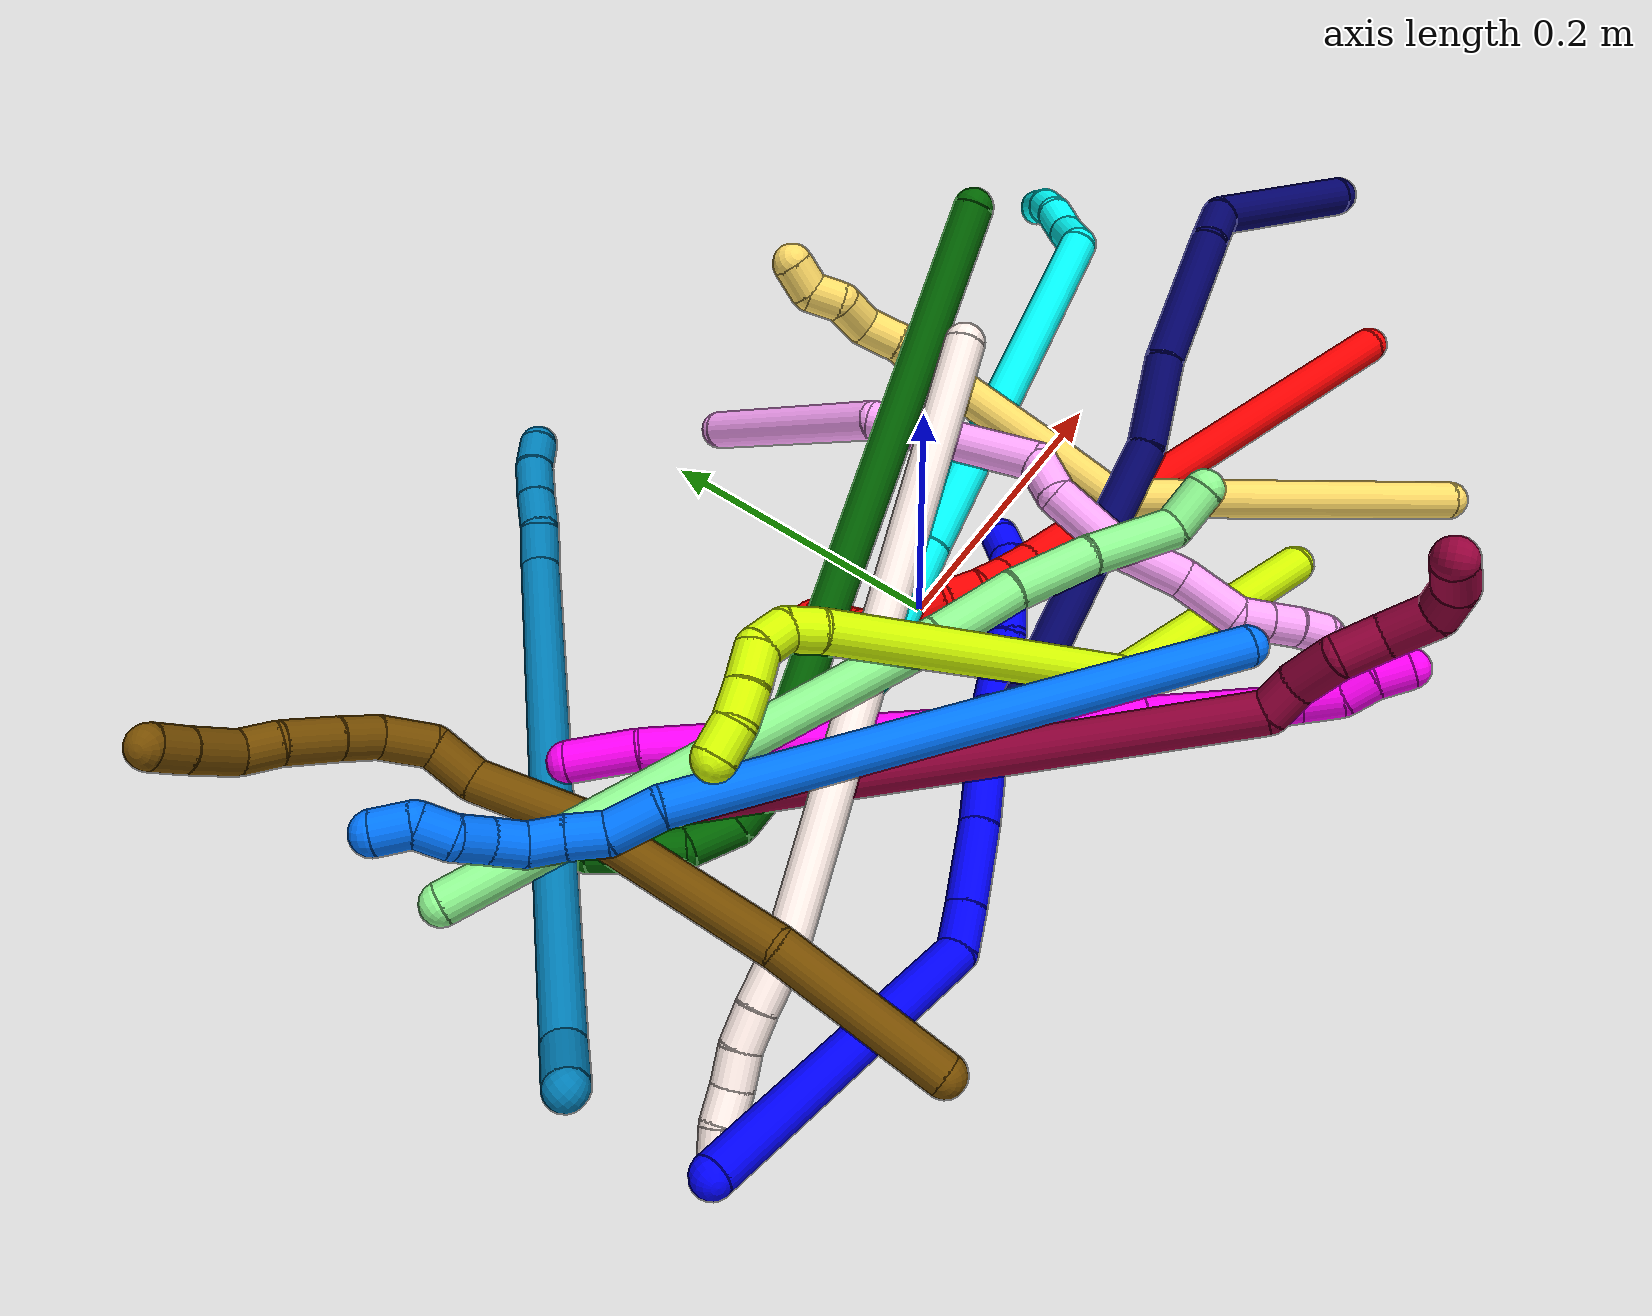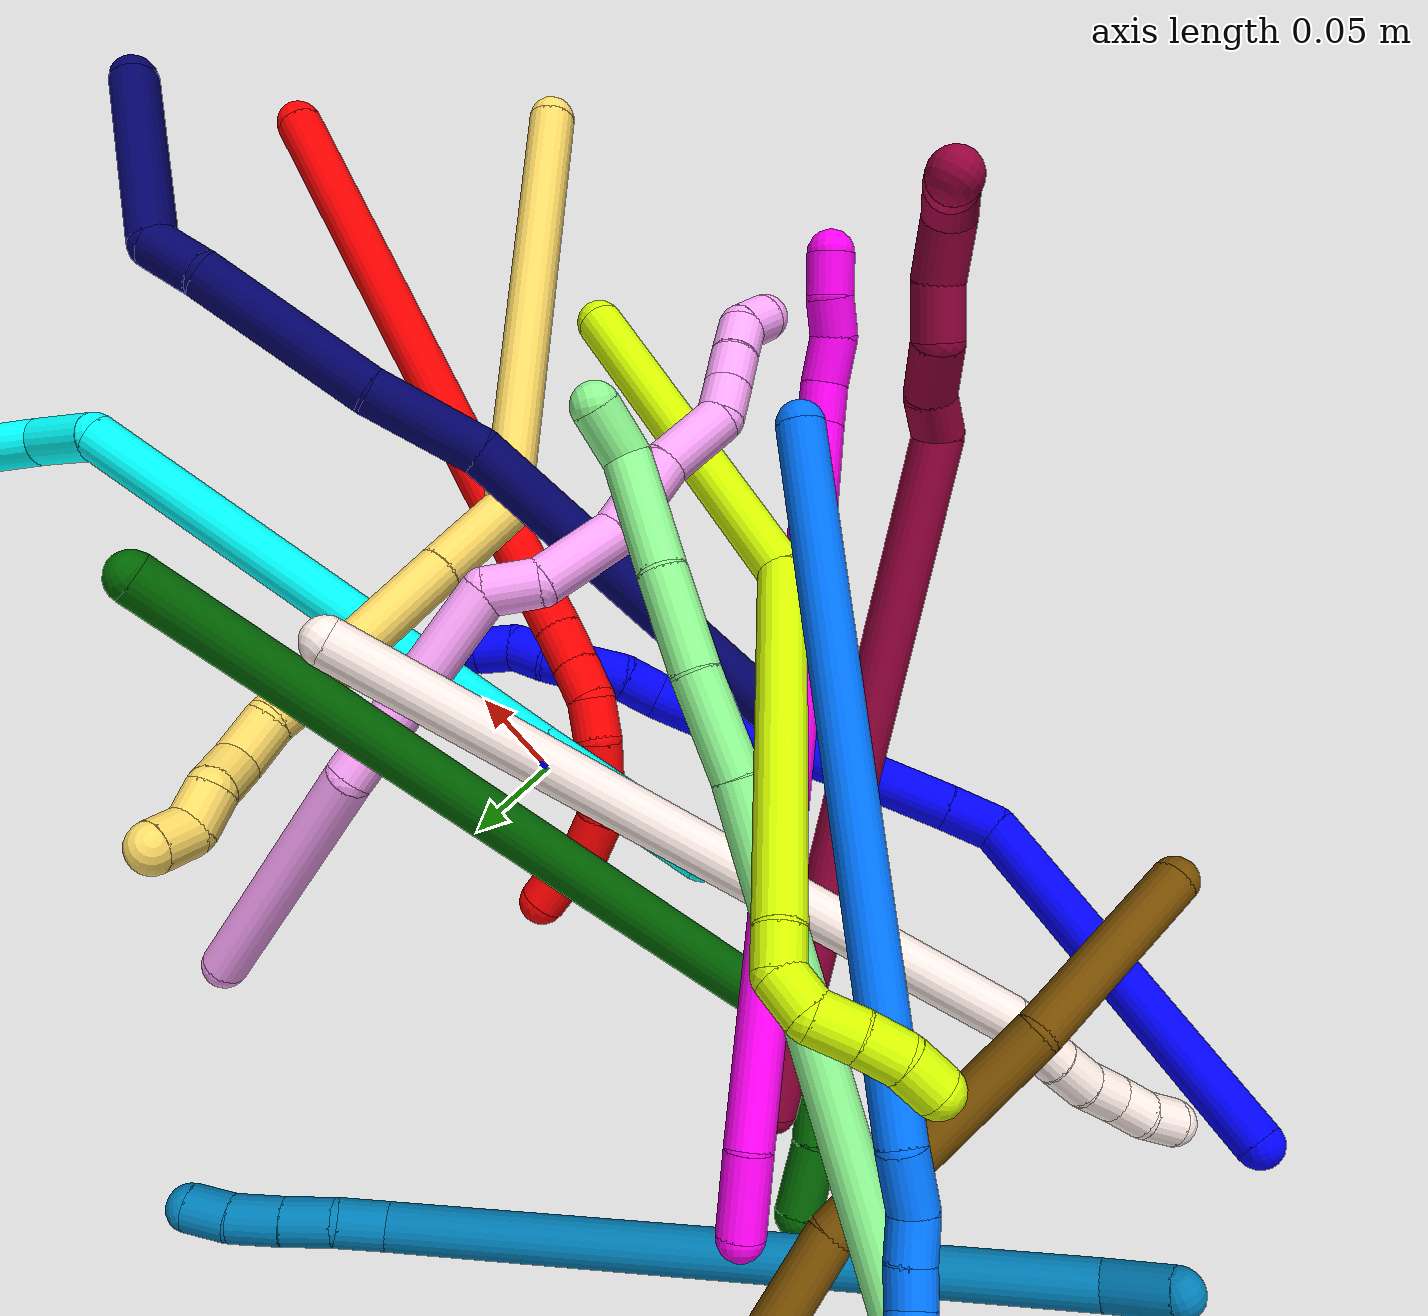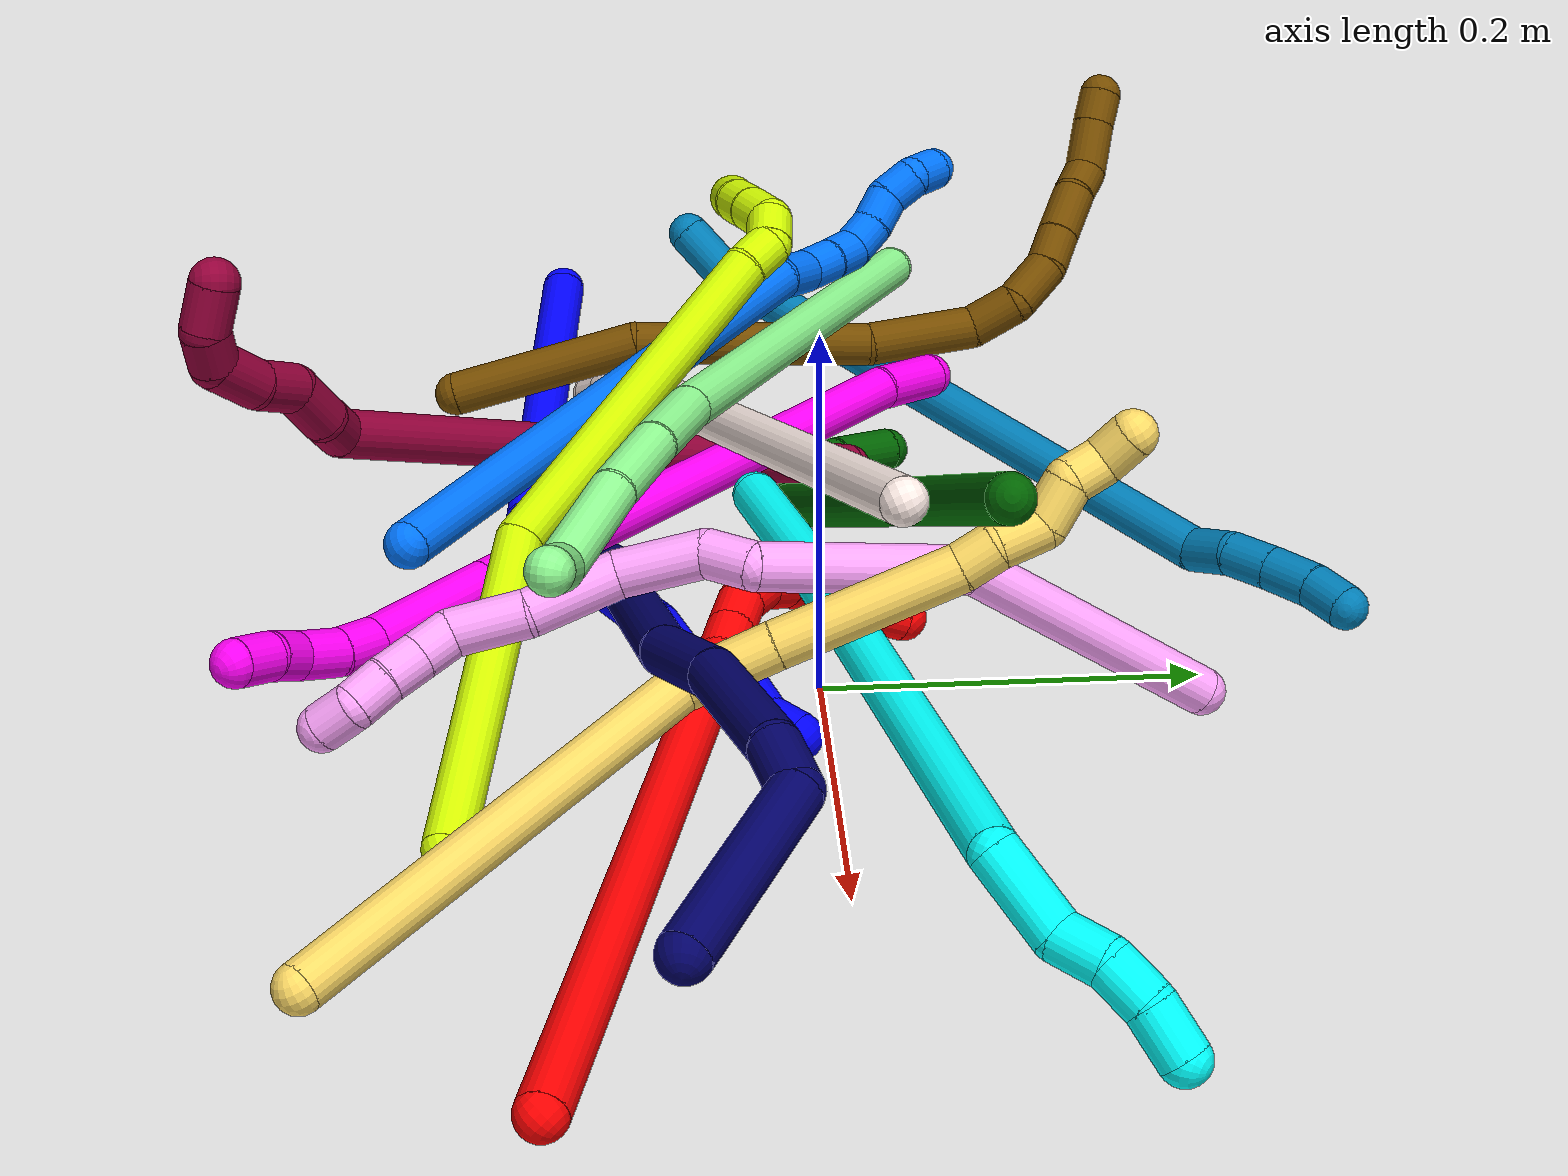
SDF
<sdf version="1.7">
 <world name="default">
  <plugin name="TubeGeneratorPlugin" filename="libtube_generator_plugin.so"/>
  <model name="photoneo_s_sensor">
   <static>1</static>
   <pose>0 0 2 1.57079 1.57079 3.14159</pose>
   <link name="link">
    <inertial><mass>0.1</mass></inertial>
    <sensor name="sensor" type="depth">
     <update_rate>30</update_rate>
     <camera>
      <horizontal_fov>1.22</horizontal_fov>
      <image><width>1920</width><height>1200</height><format>B8G8R8</format></image>
      <clip><near>0.1</near><far>4</far></clip>
      <depth_camera><output>points</output></depth_camera>
     </camera>
     <plugin name="camera_plugin" filename="libgazebo_ros_depth_camera.so">
      <baseline>0.2</baseline>
      <alwaysOn>1</alwaysOn>
      <updateRate>0.0</updateRate>
      <cameraName>camera_ir</cameraName>
      <imageTopicName>/camera/color/image_raw</imageTopicName>
      <cameraInfoTopicName>/camera/color/camera_info</cameraInfoTopicName>
      <depthImageTopicName>/camera/depth/image_raw</depthImageTopicName>
      <depthImageCameraInfoTopicName>/camera/depth/camera_info</depthImageCameraInfoTopicName>
      <pointCloudTopicName>/camera/depth/points</pointCloudTopicName>
      <frameName>fr_optical</frameName>
      <pointCloudCutoff>0.1</pointCloudCutoff>
      <pointCloudCutoffMax>2.0</pointCloudCutoffMax>
      <distortionK1>0</distortionK1>
      <distortionK2>0</distortionK2>
      <distortionK3>0</distortionK3>
      <distortionT1>0</distortionT1>
      <distortionT2>0</distortionT2>
      <CxPrime>0</CxPrime>
      <Cx>0</Cx>
      <Cy>0</Cy>
      <focalLength>0</focalLength>
      <hackBaseline>0</hackBaseline>
     </plugin>
    </sensor>
   </link>
  </model>
  <gravity>0 0 -9.8</gravity>
  <magnetic_field>6e-06 2.3e-05 -4.2e-05</magnetic_field>
  <atmosphere type="adiabatic"/>
  <physics name="default_physics" default="0" type="ode">
   <max_step_size>0.003</max_step_size>
   <real_time_factor>1</real_time_factor>
   <real_time_update_rate>1000</real_time_update_rate>
   <max_contacts>10000</max_contacts>
   <ode>
    <solver>
     <type>quick</type>
     <iters>100</iters>
     <sor>1.3</sor>
     <use_dynamic_moi_rescaling>0</use_dynamic_moi_rescaling>
    </solver>
    <constraints>
     <contact_max_correcting_vel>0</contact_max_correcting_vel>
     <contact_surface_layer>0.001</contact_surface_layer>
     <cfm>0</cfm>
     <erp>0.2</erp>
    </constraints>
   </ode>
  </physics>
  <scene><ambient>0.4 0.4 0.4 1</ambient><background>0.7 0.7 0.7 1</background><shadows>0</shadows></scene>
  <audio><device>default</device></audio>
  <spherical_coordinates>
   <surface_model>EARTH_WGS84</surface_model>
   <latitude_deg>0</latitude_deg>
   <longitude_deg>0</longitude_deg>
   <elevation>0</elevation>
   <heading_deg>0</heading_deg>
  </spherical_coordinates>
  <model name="bin">
   <static>1</static>
   <link name="bottom">
    <collision name="collision-bottom">
     <pose>0 0 -0.01 0 -0 0</pose>
     <geometry><box><size>0.8 0.6 0.02</size></box></geometry>
     <surface>
      <friction><ode><mu>100</mu><mu2>100</mu2></ode></friction>
      <contact><collide_bitmask>65535</collide_bitmask></contact>
     </surface>
    </collision>
   </link>
   <link name="west_wall">
    <collision name="collision-west_wall">
     <pose>-0.41 0 0.1 0 -0 0</pose>
     <geometry><box><size>0.02 0.6 0.2</size></box></geometry>
     <surface>
      <friction><ode><mu>100</mu><mu2>100</mu2></ode></friction>
      <contact><collide_bitmask>65535</collide_bitmask></contact>
     </surface>
    </collision>
   </link>
   <link name="east_wall">
    <collision name="collision-east_wall">
     <pose>0.41 0 0.1 0 -0 0</pose>
     <geometry><box><size>0.02 0.6 0.2</size></box></geometry>
     <surface>
      <friction><ode><mu>100</mu><mu2>100</mu2></ode></friction>
      <contact><collide_bitmask>65535</collide_bitmask></contact>
     </surface>
    </collision>
   </link>
   <link name="south_wall">
    <collision name="collision-south_wall">
     <pose>0 -0.31 0.1 0 -0 0</pose>
     <geometry><box><size>0.8 0.02 0.2</size></box></geometry>
     <surface>
      <friction><ode><mu>100</mu><mu2>100</mu2></ode></friction>
      <contact><collide_bitmask>65535</collide_bitmask></contact>
     </surface>
    </collision>
   </link>
   <link name="north_wall">
    <collision name="collision-north_wall">
     <pose>0 0.31 0.1 0 -0 0</pose>
     <geometry><box><size>0.8 0.02 0.2</size></box></geometry>
     <surface>
      <friction><ode><mu>100</mu><mu2>100</mu2></ode></friction>
      <contact><collide_bitmask>65535</collide_bitmask></contact>
     </surface>
    </collision>
   </link>
  </model>
  <model name="1">
   <static>0</static>
   <link name="1">
    <collision name="collision-cylinder-e_1_1_4">
     <pose>0.084915 -0.02155 -0.048684 2.72486 1.01077 2.41159</pose>
     <geometry><cylinder><radius>0.0125</radius><length>0.200452</length></cylinder></geometry>
     <surface>
      <friction><ode><mu>1.16</mu><mu2>1.16</mu2><slip1>0</slip1><slip2>0</slip2></ode></friction>
      <contact><ode><kp>1e+06</kp><kd>1</kd><max_vel>0</max_vel><min_depth>0.001</min_depth></ode></contact>
     </surface>
    </collision>
    <visual name="visual-cylinder-e_1_1_4">
     <pose>0.084915 -0.02155 -0.048684 2.72486 1.01077 2.41159</pose>
     <geometry><cylinder><radius>0.0125</radius><length>0.200452</length></cylinder></geometry>
     <material><ambient>0 0 1 1</ambient></material>
    </visual>
    <collision name="collision-cylinder-e_2_4_5">
     <pose>0.179753 -0.037995 -0.106062 -2.6105 0.777409 -1.96918</pose>
     <geometry><cylinder><radius>0.0125</radius><length>0.02829</length></cylinder></geometry>
     <surface>
      <friction><ode><mu>1.16</mu><mu2>1.16</mu2><slip1>0</slip1><slip2>0</slip2></ode></friction>
      <contact><ode><kp>1e+06</kp><kd>1</kd><max_vel>0</max_vel><min_depth>0.001</min_depth></ode></contact>
     </surface>
    </collision>
    <visual name="visual-cylinder-e_2_4_5">
     <pose>0.179753 -0.037995 -0.106062 -2.6105 0.777409 -1.96918</pose>
     <geometry><cylinder><radius>0.0125</radius><length>0.02829</length></cylinder></geometry>
     <material><ambient>0 0 1 1</ambient></material>
    </visual>
    <collision name="collision-cylinder-e_3_5_6">
     <pose>0.207753 -0.022843 -0.13134 -2.59696 0.750413 -1.9081</pose>
     <geometry><cylinder><radius>0.0125</radius><length>0.053021</length></cylinder></geometry>
     <surface>
      <friction><ode><mu>1.16</mu><mu2>1.16</mu2><slip1>0</slip1><slip2>0</slip2></ode></friction>
      <contact><ode><kp>1e+06</kp><kd>1</kd><max_vel>0</max_vel><min_depth>0.001</min_depth></ode></contact>
     </surface>
    </collision>
    <visual name="visual-cylinder-e_3_5_6">
     <pose>0.207753 -0.022843 -0.13134 -2.59696 0.750413 -1.9081</pose>
     <geometry><cylinder><radius>0.0125</radius><length>0.053021</length></cylinder></geometry>
     <material><ambient>0 0 1 1</ambient></material>
    </visual>
    <collision name="collision-cylinder-e_4_6_7">
     <pose>0.251561 0.004437 -0.172687 -2.53359 0.706127 -1.73104</pose>
     <geometry><cylinder><radius>0.0125</radius><length>0.079302</length></cylinder></geometry>
     <surface>
      <friction><ode><mu>1.16</mu><mu2>1.16</mu2><slip1>0</slip1><slip2>0</slip2></ode></friction>
      <contact><ode><kp>1e+06</kp><kd>1</kd><max_vel>0</max_vel><min_depth>0.001</min_depth></ode></contact>
     </surface>
    </collision>
    <visual name="visual-cylinder-e_4_6_7">
     <pose>0.251561 0.004437 -0.172687 -2.53359 0.706127 -1.73104</pose>
     <geometry><cylinder><radius>0.0125</radius><length>0.079302</length></cylinder></geometry>
     <material><ambient>0 0 1 1</ambient></material>
    </visual>
    <collision name="collision-cylinder-e_5_7_8">
     <pose>0.288563 0.025401 -0.20972 -2.84649 0.721131 -2.3906</pose>
     <geometry><cylinder><radius>0.0125</radius><length>0.03415</length></cylinder></geometry>
     <surface>
      <friction><ode><mu>1.16</mu><mu2>1.16</mu2><slip1>0</slip1><slip2>0</slip2></ode></friction>
      <contact><ode><kp>1e+06</kp><kd>1</kd><max_vel>0</max_vel><min_depth>0.001</min_depth></ode></contact>
     </surface>
    </collision>
    <visual name="visual-cylinder-e_5_7_8">
     <pose>0.288563 0.025401 -0.20972 -2.84649 0.721131 -2.3906</pose>
     <geometry><cylinder><radius>0.0125</radius><length>0.03415</length></cylinder></geometry>
     <material><ambient>0 0 1 1</ambient></material>
    </visual>
    <collision name="collision-cylinder-e_6_8_9">
     <pose>0.308092 0.035869 -0.225682 -2.07211 0.821196 -1.26766</pose>
     <geometry><cylinder><radius>0.0125</radius><length>0.022556</length></cylinder></geometry>
     <surface>
      <friction><ode><mu>1.16</mu><mu2>1.16</mu2><slip1>0</slip1><slip2>0</slip2></ode></friction>
      <contact><ode><kp>1e+06</kp><kd>1</kd><max_vel>0</max_vel><min_depth>0.001</min_depth></ode></contact>
     </surface>
    </collision>
    <visual name="visual-cylinder-e_6_8_9">
     <pose>0.308092 0.035869 -0.225682 -2.07211 0.821196 -1.26766</pose>
     <geometry><cylinder><radius>0.0125</radius><length>0.022556</length></cylinder></geometry>
     <material><ambient>0 0 1 1</ambient></material>
    </visual>
    <collision name="collision-cylinder-e_7_9_10">
     <pose>0.322203 0.049315 -0.235014 -2.26979 0.589171 -1.15473</pose>
     <geometry><cylinder><radius>0.0125</radius><length>0.021079</length></cylinder></geometry>
     <surface>
      <friction><ode><mu>1.16</mu><mu2>1.16</mu2><slip1>0</slip1><slip2>0</slip2></ode></friction>
      <contact><ode><kp>1e+06</kp><kd>1</kd><max_vel>0</max_vel><min_depth>0.001</min_depth></ode></contact>
     </surface>
    </collision>
    <visual name="visual-cylinder-e_7_9_10">
     <pose>0.322203 0.049315 -0.235014 -2.26979 0.589171 -1.15473</pose>
     <geometry><cylinder><radius>0.0125</radius><length>0.021079</length></cylinder></geometry>
     <material><ambient>0 0 1 1</ambient></material>
    </visual>
    <collision name="collision-cylinder-e_8_10_11">
     <pose>0.333704 0.059442 -0.248539 -2.73256 0.580995 -1.92848</pose>
     <geometry><cylinder><radius>0.0125</radius><length>0.020567</length></cylinder></geometry>
     <surface>
      <friction><ode><mu>1.16</mu><mu2>1.16</mu2><slip1>0</slip1><slip2>0</slip2></ode></friction>
      <contact><ode><kp>1e+06</kp><kd>1</kd><max_vel>0</max_vel><min_depth>0.001</min_depth></ode></contact>
     </surface>
    </collision>
    <visual name="visual-cylinder-e_8_10_11">
     <pose>0.333704 0.059442 -0.248539 -2.73256 0.580995 -1.92848</pose>
     <geometry><cylinder><radius>0.0125</radius><length>0.020567</length></cylinder></geometry>
     <material><ambient>0 0 1 1</ambient></material>
    </visual>
    <collision name="collision-cylinder-e_9_11_12">
     <pose>0.345366 0.064186 -0.264388 -2.97669 0.640624 -2.65331</pose>
     <geometry><cylinder><radius>0.0125</radius><length>0.020136</length></cylinder></geometry>
     <surface>
      <friction><ode><mu>1.16</mu><mu2>1.16</mu2><slip1>0</slip1><slip2>0</slip2></ode></friction>
      <contact><ode><kp>1e+06</kp><kd>1</kd><max_vel>0</max_vel><min_depth>0.001</min_depth></ode></contact>
     </surface>
    </collision>
    <visual name="visual-cylinder-e_9_11_12">
     <pose>0.345366 0.064186 -0.264388 -2.97669 0.640624 -2.65331</pose>
     <geometry><cylinder><radius>0.0125</radius><length>0.020136</length></cylinder></geometry>
     <material><ambient>0 0 1 1</ambient></material>
    </visual>
    <collision name="collision-cylinder-e_10_12_2">
     <pose>0.354079 0.069728 -0.281266 -2.69978 0.266835 -1.07737</pose>
     <geometry><cylinder><radius>0.0125</radius><length>0.020448</length></cylinder></geometry>
     <surface>
      <friction><ode><mu>1.16</mu><mu2>1.16</mu2><slip1>0</slip1><slip2>0</slip2></ode></friction>
      <contact><ode><kp>1e+06</kp><kd>1</kd><max_vel>0</max_vel><min_depth>0.001</min_depth></ode></contact>
     </surface>
    </collision>
    <visual name="visual-cylinder-e_10_12_2">
     <pose>0.354079 0.069728 -0.281266 -2.69978 0.266835 -1.07737</pose>
     <geometry><cylinder><radius>0.0125</radius><length>0.020448</length></cylinder></geometry>
     <material><ambient>0 0 1 1</ambient></material>
    </visual>
    <collision name="collision-sphere-2">
     <pose>0.356775 0.073945 -0.290181 0 -0 0</pose>
     <geometry><sphere><radius>0.0125</radius></sphere></geometry>
     <surface>
      <friction><ode><mu>1.16</mu><mu2>1.16</mu2><slip1>0</slip1><slip2>0</slip2></ode></friction>
      <contact><ode><kp>1e+06</kp><kd>1</kd><max_vel>0</max_vel><min_depth>0.001</min_depth></ode></contact>
     </surface>
    </collision>
    <visual name="visual-sphere-2">
     <pose>0.356775 0.073945 -0.290181 0 -0 0</pose>
     <geometry><sphere><radius>0.0125</radius></sphere></geometry>
     <material><ambient>0 0 1 1</ambient></material>
    </visual>
    <collision name="collision-sphere-12">
     <pose>0.351383 0.065511 -0.272351 0 -0 0</pose>
     <geometry><sphere><radius>0.0125</radius></sphere></geometry>
     <surface>
      <friction><ode><mu>1.16</mu><mu2>1.16</mu2><slip1>0</slip1><slip2>0</slip2></ode></friction>
      <contact><ode><kp>1e+06</kp><kd>1</kd><max_vel>0</max_vel><min_depth>0.001</min_depth></ode></contact>
     </surface>
    </collision>
    <visual name="visual-sphere-12">
     <pose>0.351383 0.065511 -0.272351 0 -0 0</pose>
     <geometry><sphere><radius>0.0125</radius></sphere></geometry>
     <material><ambient>0 0 1 1</ambient></material>
    </visual>
    <collision name="collision-sphere-11">
     <pose>0.339348 0.062861 -0.256426 0 -0 0</pose>
     <geometry><sphere><radius>0.0125</radius></sphere></geometry>
     <surface>
      <friction><ode><mu>1.16</mu><mu2>1.16</mu2><slip1>0</slip1><slip2>0</slip2></ode></friction>
      <contact><ode><kp>1e+06</kp><kd>1</kd><max_vel>0</max_vel><min_depth>0.001</min_depth></ode></contact>
     </surface>
    </collision>
    <visual name="visual-sphere-11">
     <pose>0.339348 0.062861 -0.256426 0 -0 0</pose>
     <geometry><sphere><radius>0.0125</radius></sphere></geometry>
     <material><ambient>0 0 1 1</ambient></material>
    </visual>
    <collision name="collision-sphere-10">
     <pose>0.32806 0.056023 -0.240652 0 -0 0</pose>
     <geometry><sphere><radius>0.0125</radius></sphere></geometry>
     <surface>
      <friction><ode><mu>1.16</mu><mu2>1.16</mu2><slip1>0</slip1><slip2>0</slip2></ode></friction>
      <contact><ode><kp>1e+06</kp><kd>1</kd><max_vel>0</max_vel><min_depth>0.001</min_depth></ode></contact>
     </surface>
    </collision>
    <visual name="visual-sphere-10">
     <pose>0.32806 0.056023 -0.240652 0 -0 0</pose>
     <geometry><sphere><radius>0.0125</radius></sphere></geometry>
     <material><ambient>0 0 1 1</ambient></material>
    </visual>
    <collision name="collision-sphere-9">
     <pose>0.316347 0.042608 -0.229375 0 -0 0</pose>
     <geometry><sphere><radius>0.0125</radius></sphere></geometry>
     <surface>
      <friction><ode><mu>1.16</mu><mu2>1.16</mu2><slip1>0</slip1><slip2>0</slip2></ode></friction>
      <contact><ode><kp>1e+06</kp><kd>1</kd><max_vel>0</max_vel><min_depth>0.001</min_depth></ode></contact>
     </surface>
    </collision>
    <visual name="visual-sphere-9">
     <pose>0.316347 0.042608 -0.229375 0 -0 0</pose>
     <geometry><sphere><radius>0.0125</radius></sphere></geometry>
     <material><ambient>0 0 1 1</ambient></material>
    </visual>
    <collision name="collision-sphere-4">
     <pose>0.169831 -0.043101 -0.097369 0 -0 0</pose>
     <geometry><sphere><radius>0.0125</radius></sphere></geometry>
     <surface>
      <friction><ode><mu>1.16</mu><mu2>1.16</mu2><slip1>0</slip1><slip2>0</slip2></ode></friction>
      <contact><ode><kp>1e+06</kp><kd>1</kd><max_vel>0</max_vel><min_depth>0.001</min_depth></ode></contact>
     </surface>
    </collision>
    <visual name="visual-sphere-4">
     <pose>0.169831 -0.043101 -0.097369 0 -0 0</pose>
     <geometry><sphere><radius>0.0125</radius></sphere></geometry>
     <material><ambient>0 0 1 1</ambient></material>
    </visual>
    <collision name="collision-sphere-1">
     <geometry><sphere><radius>0.0125</radius></sphere></geometry>
     <surface>
      <friction><ode><mu>1.16</mu><mu2>1.16</mu2><slip1>0</slip1><slip2>0</slip2></ode></friction>
      <contact><ode><kp>1e+06</kp><kd>1</kd><max_vel>0</max_vel><min_depth>0.001</min_depth></ode></contact>
     </surface>
    </collision>
    <visual name="visual-sphere-1">
     <geometry><sphere><radius>0.0125</radius></sphere></geometry>
     <material><ambient>0 0 1 1</ambient></material>
    </visual>
    <collision name="collision-sphere-8">
     <pose>0.299837 0.02913 -0.22199 0 -0 0</pose>
     <geometry><sphere><radius>0.0125</radius></sphere></geometry>
     <surface>
      <friction><ode><mu>1.16</mu><mu2>1.16</mu2><slip1>0</slip1><slip2>0</slip2></ode></friction>
      <contact><ode><kp>1e+06</kp><kd>1</kd><max_vel>0</max_vel><min_depth>0.001</min_depth></ode></contact>
     </surface>
    </collision>
    <visual name="visual-sphere-8">
     <pose>0.299837 0.02913 -0.22199 0 -0 0</pose>
     <geometry><sphere><radius>0.0125</radius></sphere></geometry>
     <material><ambient>0 0 1 1</ambient></material>
    </visual>
    <collision name="collision-sphere-5">
     <pose>0.189675 -0.032889 -0.114755 0 -0 0</pose>
     <geometry><sphere><radius>0.0125</radius></sphere></geometry>
     <surface>
      <friction><ode><mu>1.16</mu><mu2>1.16</mu2><slip1>0</slip1><slip2>0</slip2></ode></friction>
      <contact><ode><kp>1e+06</kp><kd>1</kd><max_vel>0</max_vel><min_depth>0.001</min_depth></ode></contact>
     </surface>
    </collision>
    <visual name="visual-sphere-5">
     <pose>0.189675 -0.032889 -0.114755 0 -0 0</pose>
     <geometry><sphere><radius>0.0125</radius></sphere></geometry>
     <material><ambient>0 0 1 1</ambient></material>
    </visual>
    <collision name="collision-sphere-6">
     <pose>0.225831 -0.012797 -0.147924 0 -0 0</pose>
     <geometry><sphere><radius>0.0125</radius></sphere></geometry>
     <surface>
      <friction><ode><mu>1.16</mu><mu2>1.16</mu2><slip1>0</slip1><slip2>0</slip2></ode></friction>
      <contact><ode><kp>1e+06</kp><kd>1</kd><max_vel>0</max_vel><min_depth>0.001</min_depth></ode></contact>
     </surface>
    </collision>
    <visual name="visual-sphere-6">
     <pose>0.225831 -0.012797 -0.147924 0 -0 0</pose>
     <geometry><sphere><radius>0.0125</radius></sphere></geometry>
     <material><ambient>0 0 1 1</ambient></material>
    </visual>
    <collision name="collision-sphere-7">
     <pose>0.27729 0.021671 -0.19745 0 -0 0</pose>
     <geometry><sphere><radius>0.0125</radius></sphere></geometry>
     <surface>
      <friction><ode><mu>1.16</mu><mu2>1.16</mu2><slip1>0</slip1><slip2>0</slip2></ode></friction>
      <contact><ode><kp>1e+06</kp><kd>1</kd><max_vel>0</max_vel><min_depth>0.001</min_depth></ode></contact>
     </surface>
    </collision>
    <visual name="visual-sphere-7">
     <pose>0.27729 0.021671 -0.19745 0 -0 0</pose>
     <geometry><sphere><radius>0.0125</radius></sphere></geometry>
     <material><ambient>0 0 1 1</ambient></material>
    </visual>
    <inertial>
     <pose>0.195448 0.000806 -0.133621 0 -0 0</pose>
     <mass>0.5</mass>
     <inertia>
      <ixx>-6.6e-05</ixx>
      <ixy>0</ixy>
      <ixz>0</ixz>
      <iyy>0.000851</iyy>
      <iyz>0</iyz>
      <izz>-0.000531</izz>
     </inertia>
    </inertial>
   </link>
   <pose>-0.376211 -0.131156 0.077086 0.89029 -0.166926 -0.377487</pose>
  </model>
  <model name="2">
   <static>0</static>
   <link name="2">
    <collision name="collision-cylinder-e_1_1_4">
     <pose>-0.140566 0.07217 0.053444 -0.933386 -1.00228 0.538556</pose>
     <geometry><cylinder><radius>0.0125</radius><length>0.333607</length></cylinder></geometry>
     <surface>
      <friction><ode><mu>1.16</mu><mu2>1.16</mu2><slip1>0</slip1><slip2>0</slip2></ode></friction>
      <contact><ode><kp>1e+06</kp><kd>1</kd><max_vel>0</max_vel><min_depth>0.001</min_depth></ode></contact>
     </surface>
    </collision>
    <visual name="visual-cylinder-e_1_1_4">
     <pose>-0.140566 0.07217 0.053444 -0.933386 -1.00228 0.538556</pose>
     <geometry><cylinder><radius>0.0125</radius><length>0.333607</length></cylinder></geometry>
     <material><ambient>1 0 0 1</ambient></material>
    </visual>
    <collision name="collision-cylinder-e_2_4_5">
     <pose>-0.290074 0.14998 0.110898 -0.952673 -0.912114 0.495796</pose>
     <geometry><cylinder><radius>0.0125</radius><length>0.022617</length></cylinder></geometry>
     <surface>
      <friction><ode><mu>1.16</mu><mu2>1.16</mu2><slip1>0</slip1><slip2>0</slip2></ode></friction>
      <contact><ode><kp>1e+06</kp><kd>1</kd><max_vel>0</max_vel><min_depth>0.001</min_depth></ode></contact>
     </surface>
    </collision>
    <visual name="visual-cylinder-e_2_4_5">
     <pose>-0.290074 0.14998 0.110898 -0.952673 -0.912114 0.495796</pose>
     <geometry><cylinder><radius>0.0125</radius><length>0.022617</length></cylinder></geometry>
     <material><ambient>1 0 0 1</ambient></material>
    </visual>
    <collision name="collision-cylinder-e_3_5_6">
     <pose>-0.306846 0.16126 0.118599 -0.9914 -0.860181 0.486286</pose>
     <geometry><cylinder><radius>0.0125</radius><length>0.02066</length></cylinder></geometry>
     <surface>
      <friction><ode><mu>1.16</mu><mu2>1.16</mu2><slip1>0</slip1><slip2>0</slip2></ode></friction>
      <contact><ode><kp>1e+06</kp><kd>1</kd><max_vel>0</max_vel><min_depth>0.001</min_depth></ode></contact>
     </surface>
    </collision>
    <visual name="visual-cylinder-e_3_5_6">
     <pose>-0.306846 0.16126 0.118599 -0.9914 -0.860181 0.486286</pose>
     <geometry><cylinder><radius>0.0125</radius><length>0.02066</length></cylinder></geometry>
     <material><ambient>1 0 0 1</ambient></material>
    </visual>
    <collision name="collision-cylinder-e_4_6_7">
     <pose>-0.323589 0.17233 0.122321 -1.56482 -1.02348 1.01838</pose>
     <geometry><cylinder><radius>0.0125</radius><length>0.020874</length></cylinder></geometry>
     <surface>
      <friction><ode><mu>1.16</mu><mu2>1.16</mu2><slip1>0</slip1><slip2>0</slip2></ode></friction>
      <contact><ode><kp>1e+06</kp><kd>1</kd><max_vel>0</max_vel><min_depth>0.001</min_depth></ode></contact>
     </surface>
    </collision>
    <visual name="visual-cylinder-e_4_6_7">
     <pose>-0.323589 0.17233 0.122321 -1.56482 -1.02348 1.01838</pose>
     <geometry><cylinder><radius>0.0125</radius><length>0.020874</length></cylinder></geometry>
     <material><ambient>1 0 0 1</ambient></material>
    </visual>
    <collision name="collision-cylinder-e_5_7_8">
     <pose>-0.341953 0.181156 0.11943 -2.28177 -1.12818 1.88732</pose>
     <geometry><cylinder><radius>0.0125</radius><length>0.020919</length></cylinder></geometry>
     <surface>
      <friction><ode><mu>1.16</mu><mu2>1.16</mu2><slip1>0</slip1><slip2>0</slip2></ode></friction>
      <contact><ode><kp>1e+06</kp><kd>1</kd><max_vel>0</max_vel><min_depth>0.001</min_depth></ode></contact>
     </surface>
    </collision>
    <visual name="visual-cylinder-e_5_7_8">
     <pose>-0.341953 0.181156 0.11943 -2.28177 -1.12818 1.88732</pose>
     <geometry><cylinder><radius>0.0125</radius><length>0.020919</length></cylinder></geometry>
     <material><ambient>1 0 0 1</ambient></material>
    </visual>
    <collision name="collision-cylinder-e_6_8_9">
     <pose>-0.360534 0.186814 0.113109 -2.5538 -1.15028 2.26796</pose>
     <geometry><cylinder><radius>0.0125</radius><length>0.020001</length></cylinder></geometry>
     <surface>
      <friction><ode><mu>1.16</mu><mu2>1.16</mu2><slip1>0</slip1><slip2>0</slip2></ode></friction>
      <contact><ode><kp>1e+06</kp><kd>1</kd><max_vel>0</max_vel><min_depth>0.001</min_depth></ode></contact>
     </surface>
    </collision>
    <visual name="visual-cylinder-e_6_8_9">
     <pose>-0.360534 0.186814 0.113109 -2.5538 -1.15028 2.26796</pose>
     <geometry><cylinder><radius>0.0125</radius><length>0.020001</length></cylinder></geometry>
     <material><ambient>1 0 0 1</ambient></material>
    </visual>
    <collision name="collision-cylinder-e_7_9_10">
     <pose>-0.376693 0.192526 0.102545 -2.69323 -0.723818 2.0574</pose>
     <geometry><cylinder><radius>0.0125</radius><length>0.021228</length></cylinder></geometry>
     <surface>
      <friction><ode><mu>1.16</mu><mu2>1.16</mu2><slip1>0</slip1><slip2>0</slip2></ode></friction>
      <contact><ode><kp>1e+06</kp><kd>1</kd><max_vel>0</max_vel><min_depth>0.001</min_depth></ode></contact>
     </surface>
    </collision>
    <visual name="visual-cylinder-e_7_9_10">
     <pose>-0.376693 0.192526 0.102545 -2.69323 -0.723818 2.0574</pose>
     <geometry><cylinder><radius>0.0125</radius><length>0.021228</length></cylinder></geometry>
     <material><ambient>1 0 0 1</ambient></material>
    </visual>
    <collision name="collision-cylinder-e_8_10_11">
     <pose>-0.388025 0.19898 0.086838 -2.80303 -0.443729 1.8448</pose>
     <geometry><cylinder><radius>0.0125</radius><length>0.020048</length></cylinder></geometry>
     <surface>
      <friction><ode><mu>1.16</mu><mu2>1.16</mu2><slip1>0</slip1><slip2>0</slip2></ode></friction>
      <contact><ode><kp>1e+06</kp><kd>1</kd><max_vel>0</max_vel><min_depth>0.001</min_depth></ode></contact>
     </surface>
    </collision>
    <visual name="visual-cylinder-e_8_10_11">
     <pose>-0.388025 0.19898 0.086838 -2.80303 -0.443729 1.8448</pose>
     <geometry><cylinder><radius>0.0125</radius><length>0.020048</length></cylinder></geometry>
     <material><ambient>1 0 0 1</ambient></material>
    </visual>
    <collision name="collision-cylinder-e_9_11_2">
     <pose>-0.397139 0.206293 0.070633 -2.62975 -0.500559 1.54753</pose>
     <geometry><cylinder><radius>0.0125</radius><length>0.020045</length></cylinder></geometry>
     <surface>
      <friction><ode><mu>1.16</mu><mu2>1.16</mu2><slip1>0</slip1><slip2>0</slip2></ode></friction>
      <contact><ode><kp>1e+06</kp><kd>1</kd><max_vel>0</max_vel><min_depth>0.001</min_depth></ode></contact>
     </surface>
    </collision>
    <visual name="visual-cylinder-e_9_11_2">
     <pose>-0.397139 0.206293 0.070633 -2.62975 -0.500559 1.54753</pose>
     <geometry><cylinder><radius>0.0125</radius><length>0.020045</length></cylinder></geometry>
     <material><ambient>1 0 0 1</ambient></material>
    </visual>
    <collision name="collision-sphere-2">
     <pose>-0.401949 0.2106 0.062967 0 -0 0</pose>
     <geometry><sphere><radius>0.0125</radius></sphere></geometry>
     <surface>
      <friction><ode><mu>1.16</mu><mu2>1.16</mu2><slip1>0</slip1><slip2>0</slip2></ode></friction>
      <contact><ode><kp>1e+06</kp><kd>1</kd><max_vel>0</max_vel><min_depth>0.001</min_depth></ode></contact>
     </surface>
    </collision>
    <visual name="visual-sphere-2">
     <pose>-0.401949 0.2106 0.062967 0 -0 0</pose>
     <geometry><sphere><radius>0.0125</radius></sphere></geometry>
     <material><ambient>1 0 0 1</ambient></material>
    </visual>
    <collision name="collision-sphere-11">
     <pose>-0.392329 0.201987 0.078299 0 -0 0</pose>
     <geometry><sphere><radius>0.0125</radius></sphere></geometry>
     <surface>
      <friction><ode><mu>1.16</mu><mu2>1.16</mu2><slip1>0</slip1><slip2>0</slip2></ode></friction>
      <contact><ode><kp>1e+06</kp><kd>1</kd><max_vel>0</max_vel><min_depth>0.001</min_depth></ode></contact>
     </surface>
    </collision>
    <visual name="visual-sphere-11">
     <pose>-0.392329 0.201987 0.078299 0 -0 0</pose>
     <geometry><sphere><radius>0.0125</radius></sphere></geometry>
     <material><ambient>1 0 0 1</ambient></material>
    </visual>
    <collision name="collision-sphere-10">
     <pose>-0.383722 0.195973 0.095378 0 -0 0</pose>
     <geometry><sphere><radius>0.0125</radius></sphere></geometry>
     <surface>
      <friction><ode><mu>1.16</mu><mu2>1.16</mu2><slip1>0</slip1><slip2>0</slip2></ode></friction>
      <contact><ode><kp>1e+06</kp><kd>1</kd><max_vel>0</max_vel><min_depth>0.001</min_depth></ode></contact>
     </surface>
    </collision>
    <visual name="visual-sphere-10">
     <pose>-0.383722 0.195973 0.095378 0 -0 0</pose>
     <geometry><sphere><radius>0.0125</radius></sphere></geometry>
     <material><ambient>1 0 0 1</ambient></material>
    </visual>
    <collision name="collision-sphere-9">
     <pose>-0.369663 0.189078 0.109711 0 -0 0</pose>
     <geometry><sphere><radius>0.0125</radius></sphere></geometry>
     <surface>
      <friction><ode><mu>1.16</mu><mu2>1.16</mu2><slip1>0</slip1><slip2>0</slip2></ode></friction>
      <contact><ode><kp>1e+06</kp><kd>1</kd><max_vel>0</max_vel><min_depth>0.001</min_depth></ode></contact>
     </surface>
    </collision>
    <visual name="visual-sphere-9">
     <pose>-0.369663 0.189078 0.109711 0 -0 0</pose>
     <geometry><sphere><radius>0.0125</radius></sphere></geometry>
     <material><ambient>1 0 0 1</ambient></material>
    </visual>
    <collision name="collision-sphere-4">
     <pose>-0.281131 0.144339 0.106887 0 -0 0</pose>
     <geometry><sphere><radius>0.0125</radius></sphere></geometry>
     <surface>
      <friction><ode><mu>1.16</mu><mu2>1.16</mu2><slip1>0</slip1><slip2>0</slip2></ode></friction>
      <contact><ode><kp>1e+06</kp><kd>1</kd><max_vel>0</max_vel><min_depth>0.001</min_depth></ode></contact>
     </surface>
    </collision>
    <visual name="visual-sphere-4">
     <pose>-0.281131 0.144339 0.106887 0 -0 0</pose>
     <geometry><sphere><radius>0.0125</radius></sphere></geometry>
     <material><ambient>1 0 0 1</ambient></material>
    </visual>
    <collision name="collision-sphere-1">
     <geometry><sphere><radius>0.0125</radius></sphere></geometry>
     <surface>
      <friction><ode><mu>1.16</mu><mu2>1.16</mu2><slip1>0</slip1><slip2>0</slip2></ode></friction>
      <contact><ode><kp>1e+06</kp><kd>1</kd><max_vel>0</max_vel><min_depth>0.001</min_depth></ode></contact>
     </surface>
    </collision>
    <visual name="visual-sphere-1">
     <geometry><sphere><radius>0.0125</radius></sphere></geometry>
     <material><ambient>1 0 0 1</ambient></material>
    </visual>
    <collision name="collision-sphere-8">
     <pose>-0.351405 0.18455 0.116506 0 -0 0</pose>
     <geometry><sphere><radius>0.0125</radius></sphere></geometry>
     <surface>
      <friction><ode><mu>1.16</mu><mu2>1.16</mu2><slip1>0</slip1><slip2>0</slip2></ode></friction>
      <contact><ode><kp>1e+06</kp><kd>1</kd><max_vel>0</max_vel><min_depth>0.001</min_depth></ode></contact>
     </surface>
    </collision>
    <visual name="visual-sphere-8">
     <pose>-0.351405 0.18455 0.116506 0 -0 0</pose>
     <geometry><sphere><radius>0.0125</radius></sphere></geometry>
     <material><ambient>1 0 0 1</ambient></material>
    </visual>
    <collision name="collision-sphere-5">
     <pose>-0.299016 0.155621 0.114909 0 -0 0</pose>
     <geometry><sphere><radius>0.0125</radius></sphere></geometry>
     <surface>
      <friction><ode><mu>1.16</mu><mu2>1.16</mu2><slip1>0</slip1><slip2>0</slip2></ode></friction>
      <contact><ode><kp>1e+06</kp><kd>1</kd><max_vel>0</max_vel><min_depth>0.001</min_depth></ode></contact>
     </surface>
    </collision>
    <visual name="visual-sphere-5">
     <pose>-0.299016 0.155621 0.114909 0 -0 0</pose>
     <geometry><sphere><radius>0.0125</radius></sphere></geometry>
     <material><ambient>1 0 0 1</ambient></material>
    </visual>
    <collision name="collision-sphere-6">
     <pose>-0.314676 0.166898 0.122288 0 -0 0</pose>
     <geometry><sphere><radius>0.0125</radius></sphere></geometry>
     <surface>
      <friction><ode><mu>1.16</mu><mu2>1.16</mu2><slip1>0</slip1><slip2>0</slip2></ode></friction>
      <contact><ode><kp>1e+06</kp><kd>1</kd><max_vel>0</max_vel><min_depth>0.001</min_depth></ode></contact>
     </surface>
    </collision>
    <visual name="visual-sphere-6">
     <pose>-0.314676 0.166898 0.122288 0 -0 0</pose>
     <geometry><sphere><radius>0.0125</radius></sphere></geometry>
     <material><ambient>1 0 0 1</ambient></material>
    </visual>
    <collision name="collision-sphere-7">
     <pose>-0.332501 0.177761 0.122353 0 -0 0</pose>
     <geometry><sphere><radius>0.0125</radius></sphere></geometry>
     <surface>
      <friction><ode><mu>1.16</mu><mu2>1.16</mu2><slip1>0</slip1><slip2>0</slip2></ode></friction>
      <contact><ode><kp>1e+06</kp><kd>1</kd><max_vel>0</max_vel><min_depth>0.001</min_depth></ode></contact>
     </surface>
    </collision>
    <visual name="visual-sphere-7">
     <pose>-0.332501 0.177761 0.122353 0 -0 0</pose>
     <geometry><sphere><radius>0.0125</radius></sphere></geometry>
     <material><ambient>1 0 0 1</ambient></material>
    </visual>
    <inertial>
     <pose>-0.209298 0.10827 0.070871 0 -0 0</pose>
     <mass>0.5</mass>
     <inertia>
      <ixx>0.00227</ixx>
      <ixy>0</ixy>
      <ixz>0</ixz>
      <iyy>0.003556</iyy>
      <iyz>0</iyz>
      <izz>0.001283</izz>
     </inertia>
    </inertial>
   </link>
   <pose>0.364196 -0.141802 0.011496 0.881998 -0.465694 -0.242518</pose>
  </model>
  <model name="3">
   <static>0</static>
   <link name="3">
    <collision name="collision-cylinder-e_1_1_4">
     <pose>0.028717 0.012816 0.037251 -0.331357 0.629902 -0.108846</pose>
     <geometry><cylinder><radius>0.0125</radius><length>0.097499</length></cylinder></geometry>
     <surface>
      <friction><ode><mu>1.16</mu><mu2>1.16</mu2><slip1>0</slip1><slip2>0</slip2></ode></friction>
      <contact><ode><kp>1e+06</kp><kd>1</kd><max_vel>0</max_vel><min_depth>0.001</min_depth></ode></contact>
     </surface>
    </collision>
    <visual name="visual-cylinder-e_1_1_4">
     <pose>0.028717 0.012816 0.037251 -0.331357 0.629902 -0.108846</pose>
     <geometry><cylinder><radius>0.0125</radius><length>0.097499</length></cylinder></geometry>
     <material><ambient>0.003922 1 0.996078 1</ambient></material>
    </visual>
    <collision name="collision-cylinder-e_2_4_5">
     <pose>0.137496 0.068975 0.18062 -0.387766 0.609688 -0.123407</pose>
     <geometry><cylinder><radius>0.0125</radius><length>0.279641</length></cylinder></geometry>
     <surface>
      <friction><ode><mu>1.16</mu><mu2>1.16</mu2><slip1>0</slip1><slip2>0</slip2></ode></friction>
      <contact><ode><kp>1e+06</kp><kd>1</kd><max_vel>0</max_vel><min_depth>0.001</min_depth></ode></contact>
     </surface>
    </collision>
    <visual name="visual-cylinder-e_2_4_5">
     <pose>0.137496 0.068975 0.18062 -0.387766 0.609688 -0.123407</pose>
     <geometry><cylinder><radius>0.0125</radius><length>0.279641</length></cylinder></geometry>
     <material><ambient>0.003922 1 0.996078 1</ambient></material>
    </visual>
    <collision name="collision-cylinder-e_3_5_6">
     <pose>0.214493 0.122273 0.307121 -0.454287 -0.134363 0.0311</pose>
     <geometry><cylinder><radius>0.0125</radius><length>0.04578</length></cylinder></geometry>
     <surface>
      <friction><ode><mu>1.16</mu><mu2>1.16</mu2><slip1>0</slip1><slip2>0</slip2></ode></friction>
      <contact><ode><kp>1e+06</kp><kd>1</kd><max_vel>0</max_vel><min_depth>0.001</min_depth></ode></contact>
     </surface>
    </collision>
    <visual name="visual-cylinder-e_3_5_6">
     <pose>0.214493 0.122273 0.307121 -0.454287 -0.134363 0.0311</pose>
     <geometry><cylinder><radius>0.0125</radius><length>0.04578</length></cylinder></geometry>
     <material><ambient>0.003922 1 0.996078 1</ambient></material>
    </visual>
    <collision name="collision-cylinder-e_4_6_7">
     <pose>0.211336 0.132473 0.340298 -0.019214 -0.007084 6.8e-05</pose>
     <geometry><cylinder><radius>0.0125</radius><length>0.025595</length></cylinder></geometry>
     <surface>
      <friction><ode><mu>1.16</mu><mu2>1.16</mu2><slip1>0</slip1><slip2>0</slip2></ode></friction>
      <contact><ode><kp>1e+06</kp><kd>1</kd><max_vel>0</max_vel><min_depth>0.001</min_depth></ode></contact>
     </surface>
    </collision>
    <visual name="visual-cylinder-e_4_6_7">
     <pose>0.211336 0.132473 0.340298 -0.019214 -0.007084 6.8e-05</pose>
     <geometry><cylinder><radius>0.0125</radius><length>0.025595</length></cylinder></geometry>
     <material><ambient>0.003922 1 0.996078 1</ambient></material>
    </visual>
    <collision name="collision-cylinder-e_5_7_8">
     <pose>0.20909 0.136688 0.364354 -0.338872 -0.178583 0.03063</pose>
     <geometry><cylinder><radius>0.0125</radius><length>0.024266</length></cylinder></geometry>
     <surface>
      <friction><ode><mu>1.16</mu><mu2>1.16</mu2><slip1>0</slip1><slip2>0</slip2></ode></friction>
      <contact><ode><kp>1e+06</kp><kd>1</kd><max_vel>0</max_vel><min_depth>0.001</min_depth></ode></contact>
     </surface>
    </collision>
    <visual name="visual-cylinder-e_5_7_8">
     <pose>0.20909 0.136688 0.364354 -0.338872 -0.178583 0.03063</pose>
     <geometry><cylinder><radius>0.0125</radius><length>0.024266</length></cylinder></geometry>
     <material><ambient>0.003922 1 0.996078 1</ambient></material>
    </visual>
    <collision name="collision-cylinder-e_6_8_2">
     <pose>0.20262 0.147661 0.386457 -0.573592 -0.32263 0.095913</pose>
     <geometry><cylinder><radius>0.0125</radius><length>0.027219</length></cylinder></geometry>
     <surface>
      <friction><ode><mu>1.16</mu><mu2>1.16</mu2><slip1>0</slip1><slip2>0</slip2></ode></friction>
      <contact><ode><kp>1e+06</kp><kd>1</kd><max_vel>0</max_vel><min_depth>0.001</min_depth></ode></contact>
     </surface>
    </collision>
    <visual name="visual-cylinder-e_6_8_2">
     <pose>0.20262 0.147661 0.386457 -0.573592 -0.32263 0.095913</pose>
     <geometry><cylinder><radius>0.0125</radius><length>0.027219</length></cylinder></geometry>
     <material><ambient>0.003922 1 0.996078 1</ambient></material>
    </visual>
    <collision name="collision-sphere-2">
     <pose>0.198305 0.154665 0.397299 0 -0 0</pose>
     <geometry><sphere><radius>0.0125</radius></sphere></geometry>
     <surface>
      <friction><ode><mu>1.16</mu><mu2>1.16</mu2><slip1>0</slip1><slip2>0</slip2></ode></friction>
      <contact><ode><kp>1e+06</kp><kd>1</kd><max_vel>0</max_vel><min_depth>0.001</min_depth></ode></contact>
     </surface>
    </collision>
    <visual name="visual-sphere-2">
     <pose>0.198305 0.154665 0.397299 0 -0 0</pose>
     <geometry><sphere><radius>0.0125</radius></sphere></geometry>
     <material><ambient>0.003922 1 0.996078 1</ambient></material>
    </visual>
    <collision name="collision-sphere-4">
     <pose>0.057433 0.025632 0.074501 0 -0 0</pose>
     <geometry><sphere><radius>0.0125</radius></sphere></geometry>
     <surface>
      <friction><ode><mu>1.16</mu><mu2>1.16</mu2><slip1>0</slip1><slip2>0</slip2></ode></friction>
      <contact><ode><kp>1e+06</kp><kd>1</kd><max_vel>0</max_vel><min_depth>0.001</min_depth></ode></contact>
     </surface>
    </collision>
    <visual name="visual-sphere-4">
     <pose>0.057433 0.025632 0.074501 0 -0 0</pose>
     <geometry><sphere><radius>0.0125</radius></sphere></geometry>
     <material><ambient>0.003922 1 0.996078 1</ambient></material>
    </visual>
    <collision name="collision-sphere-1">
     <geometry><sphere><radius>0.0125</radius></sphere></geometry>
     <surface>
      <friction><ode><mu>1.16</mu><mu2>1.16</mu2><slip1>0</slip1><slip2>0</slip2></ode></friction>
      <contact><ode><kp>1e+06</kp><kd>1</kd><max_vel>0</max_vel><min_depth>0.001</min_depth></ode></contact>
     </surface>
    </collision>
    <visual name="visual-sphere-1">
     <geometry><sphere><radius>0.0125</radius></sphere></geometry>
     <material><ambient>0.003922 1 0.996078 1</ambient></material>
    </visual>
    <collision name="collision-sphere-8">
     <pose>0.206935 0.140657 0.375615 0 -0 0</pose>
     <geometry><sphere><radius>0.0125</radius></sphere></geometry>
     <surface>
      <friction><ode><mu>1.16</mu><mu2>1.16</mu2><slip1>0</slip1><slip2>0</slip2></ode></friction>
      <contact><ode><kp>1e+06</kp><kd>1</kd><max_vel>0</max_vel><min_depth>0.001</min_depth></ode></contact>
     </surface>
    </collision>
    <visual name="visual-sphere-8">
     <pose>0.206935 0.140657 0.375615 0 -0 0</pose>
     <geometry><sphere><radius>0.0125</radius></sphere></geometry>
     <material><ambient>0.003922 1 0.996078 1</ambient></material>
    </visual>
    <collision name="collision-sphere-5">
     <pose>0.217559 0.112319 0.286738 0 -0 0</pose>
     <geometry><sphere><radius>0.0125</radius></sphere></geometry>
     <surface>
      <friction><ode><mu>1.16</mu><mu2>1.16</mu2><slip1>0</slip1><slip2>0</slip2></ode></friction>
      <contact><ode><kp>1e+06</kp><kd>1</kd><max_vel>0</max_vel><min_depth>0.001</min_depth></ode></contact>
     </surface>
    </collision>
    <visual name="visual-sphere-5">
     <pose>0.217559 0.112319 0.286738 0 -0 0</pose>
     <geometry><sphere><radius>0.0125</radius></sphere></geometry>
     <material><ambient>0.003922 1 0.996078 1</ambient></material>
    </visual>
    <collision name="collision-sphere-6">
     <pose>0.211426 0.132227 0.327503 0 -0 0</pose>
     <geometry><sphere><radius>0.0125</radius></sphere></geometry>
     <surface>
      <friction><ode><mu>1.16</mu><mu2>1.16</mu2><slip1>0</slip1><slip2>0</slip2></ode></friction>
      <contact><ode><kp>1e+06</kp><kd>1</kd><max_vel>0</max_vel><min_depth>0.001</min_depth></ode></contact>
     </surface>
    </collision>
    <visual name="visual-sphere-6">
     <pose>0.211426 0.132227 0.327503 0 -0 0</pose>
     <geometry><sphere><radius>0.0125</radius></sphere></geometry>
     <material><ambient>0.003922 1 0.996078 1</ambient></material>
    </visual>
    <collision name="collision-sphere-7">
     <pose>0.211245 0.132719 0.353093 0 -0 0</pose>
     <geometry><sphere><radius>0.0125</radius></sphere></geometry>
     <surface>
      <friction><ode><mu>1.16</mu><mu2>1.16</mu2><slip1>0</slip1><slip2>0</slip2></ode></friction>
      <contact><ode><kp>1e+06</kp><kd>1</kd><max_vel>0</max_vel><min_depth>0.001</min_depth></ode></contact>
     </surface>
    </collision>
    <visual name="visual-sphere-7">
     <pose>0.211245 0.132719 0.353093 0 -0 0</pose>
     <geometry><sphere><radius>0.0125</radius></sphere></geometry>
     <material><ambient>0.003922 1 0.996078 1</ambient></material>
    </visual>
    <inertial>
     <pose>0.134134 0.073724 0.192542 0 -0 0</pose>
     <mass>0.5</mass>
     <inertia>
      <ixx>0.001397</ixx>
      <ixy>0</ixy>
      <ixz>0</ixz>
      <iyy>0.001647</iyy>
      <iyz>0</iyz>
      <izz>-0.00166</izz>
     </inertia>
    </inertial>
   </link>
   <pose>-0.093141 -0.02771 0.068422 -1.76573 -0.667259 -0.538743</pose>
  </model>
  <model name="4">
   <static>0</static>
   <link name="4">
    <collision name="collision-cylinder-e_1_1_4">
     <pose>0.019776 -0.057739 0.041502 0.947574 0.271262 0.139718</pose>
     <geometry><cylinder><radius>0.0125</radius><length>0.14761</length></cylinder></geometry>
     <surface>
      <friction><ode><mu>1.16</mu><mu2>1.16</mu2><slip1>0</slip1><slip2>0</slip2></ode></friction>
      <contact><ode><kp>1e+06</kp><kd>1</kd><max_vel>0</max_vel><min_depth>0.001</min_depth></ode></contact>
     </surface>
    </collision>
    <visual name="visual-cylinder-e_1_1_4">
     <pose>0.019776 -0.057739 0.041502 0.947574 0.271262 0.139718</pose>
     <geometry><cylinder><radius>0.0125</radius><length>0.14761</length></cylinder></geometry>
     <material><ambient>1 0.65098 0.996078 1</ambient></material>
    </visual>
    <collision name="collision-cylinder-e_2_4_5">
     <pose>0.06138 -0.139802 0.128484 0.491122 0.40035 0.10161</pose>
     <geometry><cylinder><radius>0.0125</radius><length>0.112012</length></cylinder></geometry>
     <surface>
      <friction><ode><mu>1.16</mu><mu2>1.16</mu2><slip1>0</slip1><slip2>0</slip2></ode></friction>
      <contact><ode><kp>1e+06</kp><kd>1</kd><max_vel>0</max_vel><min_depth>0.001</min_depth></ode></contact>
     </surface>
    </collision>
    <visual name="visual-cylinder-e_2_4_5">
     <pose>0.06138 -0.139802 0.128484 0.491122 0.40035 0.10161</pose>
     <geometry><cylinder><radius>0.0125</radius><length>0.112012</length></cylinder></geometry>
     <material><ambient>1 0.65098 0.996078 1</ambient></material>
    </visual>
    <collision name="collision-cylinder-e_3_5_6">
     <pose>0.095686 -0.168517 0.177829 0.849154 1.13249 0.559671</pose>
     <geometry><cylinder><radius>0.0125</radius><length>0.027562</length></cylinder></geometry>
     <surface>
      <friction><ode><mu>1.16</mu><mu2>1.16</mu2><slip1>0</slip1><slip2>0</slip2></ode></friction>
      <contact><ode><kp>1e+06</kp><kd>1</kd><max_vel>0</max_vel><min_depth>0.001</min_depth></ode></contact>
     </surface>
    </collision>
    <visual name="visual-cylinder-e_3_5_6">
     <pose>0.095686 -0.168517 0.177829 0.849154 1.13249 0.559671</pose>
     <geometry><cylinder><radius>0.0125</radius><length>0.027562</length></cylinder></geometry>
     <material><ambient>1 0.65098 0.996078 1</ambient></material>
    </visual>
    <collision name="collision-cylinder-e_4_6_7">
     <pose>0.123844 -0.174273 0.198019 0.083409 0.763488 0.0335</pose>
     <geometry><cylinder><radius>0.0125</radius><length>0.045355</length></cylinder></geometry>
     <surface>
      <friction><ode><mu>1.16</mu><mu2>1.16</mu2><slip1>0</slip1><slip2>0</slip2></ode></friction>
      <contact><ode><kp>1e+06</kp><kd>1</kd><max_vel>0</max_vel><min_depth>0.001</min_depth></ode></contact>
     </surface>
    </collision>
    <visual name="visual-cylinder-e_4_6_7">
     <pose>0.123844 -0.174273 0.198019 0.083409 0.763488 0.0335</pose>
     <geometry><cylinder><radius>0.0125</radius><length>0.045355</length></cylinder></geometry>
     <material><ambient>1 0.65098 0.996078 1</ambient></material>
    </visual>
    <collision name="collision-cylinder-e_5_7_8">
     <pose>0.149471 -0.175827 0.236004 0.008752 0.430479 0.001913</pose>
     <geometry><cylinder><radius>0.0125</radius><length>0.047671</length></cylinder></geometry>
     <surface>
      <friction><ode><mu>1.16</mu><mu2>1.16</mu2><slip1>0</slip1><slip2>0</slip2></ode></friction>
      <contact><ode><kp>1e+06</kp><kd>1</kd><max_vel>0</max_vel><min_depth>0.001</min_depth></ode></contact>
     </surface>
    </collision>
    <visual name="visual-cylinder-e_5_7_8">
     <pose>0.149471 -0.175827 0.236004 0.008752 0.430479 0.001913</pose>
     <geometry><cylinder><radius>0.0125</radius><length>0.047671</length></cylinder></geometry>
     <material><ambient>1 0.65098 0.996078 1</ambient></material>
    </visual>
    <collision name="collision-cylinder-e_6_8_9">
     <pose>0.171473 -0.177695 0.273211 0.10749 0.656772 0.036655</pose>
     <geometry><cylinder><radius>0.0125</radius><length>0.039488</length></cylinder></geometry>
     <surface>
      <friction><ode><mu>1.16</mu><mu2>1.16</mu2><slip1>0</slip1><slip2>0</slip2></ode></friction>
      <contact><ode><kp>1e+06</kp><kd>1</kd><max_vel>0</max_vel><min_depth>0.001</min_depth></ode></contact>
     </surface>
    </collision>
    <visual name="visual-cylinder-e_6_8_9">
     <pose>0.171473 -0.177695 0.273211 0.10749 0.656772 0.036655</pose>
     <geometry><cylinder><radius>0.0125</radius><length>0.039488</length></cylinder></geometry>
     <material><ambient>1 0.65098 0.996078 1</ambient></material>
    </visual>
    <collision name="collision-cylinder-e_7_9_10">
     <pose>0.18458 -0.17855 0.298809 -0.08163 0.103945 -0.004249</pose>
     <geometry><cylinder><radius>0.0125</radius><length>0.020281</length></cylinder></geometry>
     <surface>
      <friction><ode><mu>1.16</mu><mu2>1.16</mu2><slip1>0</slip1><slip2>0</slip2></ode></friction>
      <contact><ode><kp>1e+06</kp><kd>1</kd><max_vel>0</max_vel><min_depth>0.001</min_depth></ode></contact>
     </surface>
    </collision>
    <visual name="visual-cylinder-e_7_9_10">
     <pose>0.18458 -0.17855 0.298809 -0.08163 0.103945 -0.004249</pose>
     <geometry><cylinder><radius>0.0125</radius><length>0.020281</length></cylinder></geometry>
     <material><ambient>1 0.65098 0.996078 1</ambient></material>
    </visual>
    <collision name="collision-cylinder-e_8_10_11">
     <pose>0.186554 -0.177045 0.318805 -0.068558 0.092222 -0.003165</pose>
     <geometry><cylinder><radius>0.0125</radius><length>0.020019</length></cylinder></geometry>
     <surface>
      <friction><ode><mu>1.16</mu><mu2>1.16</mu2><slip1>0</slip1><slip2>0</slip2></ode></friction>
      <contact><ode><kp>1e+06</kp><kd>1</kd><max_vel>0</max_vel><min_depth>0.001</min_depth></ode></contact>
     </surface>
    </collision>
    <visual name="visual-cylinder-e_8_10_11">
     <pose>0.186554 -0.177045 0.318805 -0.068558 0.092222 -0.003165</pose>
     <geometry><cylinder><radius>0.0125</radius><length>0.020019</length></cylinder></geometry>
     <material><ambient>1 0.65098 0.996078 1</ambient></material>
    </visual>
    <collision name="collision-cylinder-e_9_11_12">
     <pose>0.188797 -0.174618 0.338507 -0.176873 0.132466 -0.011763</pose>
     <geometry><cylinder><radius>0.0125</radius><length>0.020001</length></cylinder></geometry>
     <surface>
      <friction><ode><mu>1.16</mu><mu2>1.16</mu2><slip1>0</slip1><slip2>0</slip2></ode></friction>
      <contact><ode><kp>1e+06</kp><kd>1</kd><max_vel>0</max_vel><min_depth>0.001</min_depth></ode></contact>
     </surface>
    </collision>
    <visual name="visual-cylinder-e_9_11_12">
     <pose>0.188797 -0.174618 0.338507 -0.176873 0.132466 -0.011763</pose>
     <geometry><cylinder><radius>0.0125</radius><length>0.020001</length></cylinder></geometry>
     <material><ambient>1 0.65098 0.996078 1</ambient></material>
    </visual>
    <collision name="collision-cylinder-e_10_12_2">
     <pose>0.196723 -0.169783 0.355108 -0.42418 0.721508 -0.162115</pose>
     <geometry><cylinder><radius>0.0125</radius><length>0.02</length></cylinder></geometry>
     <surface>
      <friction><ode><mu>1.16</mu><mu2>1.16</mu2><slip1>0</slip1><slip2>0</slip2></ode></friction>
      <contact><ode><kp>1e+06</kp><kd>1</kd><max_vel>0</max_vel><min_depth>0.001</min_depth></ode></contact>
     </surface>
    </collision>
    <visual name="visual-cylinder-e_10_12_2">
     <pose>0.196723 -0.169783 0.355108 -0.42418 0.721508 -0.162115</pose>
     <geometry><cylinder><radius>0.0125</radius><length>0.02</length></cylinder></geometry>
     <material><ambient>1 0.65098 0.996078 1</ambient></material>
    </visual>
    <collision name="collision-sphere-2">
     <pose>0.203328 -0.166693 0.361951 0 -0 0</pose>
     <geometry><sphere><radius>0.0125</radius></sphere></geometry>
     <surface>
      <friction><ode><mu>1.16</mu><mu2>1.16</mu2><slip1>0</slip1><slip2>0</slip2></ode></friction>
      <contact><ode><kp>1e+06</kp><kd>1</kd><max_vel>0</max_vel><min_depth>0.001</min_depth></ode></contact>
     </surface>
    </collision>
    <visual name="visual-sphere-2">
     <pose>0.203328 -0.166693 0.361951 0 -0 0</pose>
     <geometry><sphere><radius>0.0125</radius></sphere></geometry>
     <material><ambient>1 0.65098 0.996078 1</ambient></material>
    </visual>
    <collision name="collision-sphere-12">
     <pose>0.190118 -0.172873 0.348265 0 -0 0</pose>
     <geometry><sphere><radius>0.0125</radius></sphere></geometry>
     <surface>
      <friction><ode><mu>1.16</mu><mu2>1.16</mu2><slip1>0</slip1><slip2>0</slip2></ode></friction>
      <contact><ode><kp>1e+06</kp><kd>1</kd><max_vel>0</max_vel><min_depth>0.001</min_depth></ode></contact>
     </surface>
    </collision>
    <visual name="visual-sphere-12">
     <pose>0.190118 -0.172873 0.348265 0 -0 0</pose>
     <geometry><sphere><radius>0.0125</radius></sphere></geometry>
     <material><ambient>1 0.65098 0.996078 1</ambient></material>
    </visual>
    <collision name="collision-sphere-11">
     <pose>0.187476 -0.176362 0.328749 0 -0 0</pose>
     <geometry><sphere><radius>0.0125</radius></sphere></geometry>
     <surface>
      <friction><ode><mu>1.16</mu><mu2>1.16</mu2><slip1>0</slip1><slip2>0</slip2></ode></friction>
      <contact><ode><kp>1e+06</kp><kd>1</kd><max_vel>0</max_vel><min_depth>0.001</min_depth></ode></contact>
     </surface>
    </collision>
    <visual name="visual-sphere-11">
     <pose>0.187476 -0.176362 0.328749 0 -0 0</pose>
     <geometry><sphere><radius>0.0125</radius></sphere></geometry>
     <material><ambient>1 0.65098 0.996078 1</ambient></material>
    </visual>
    <collision name="collision-sphere-10">
     <pose>0.185632 -0.177727 0.308861 0 -0 0</pose>
     <geometry><sphere><radius>0.0125</radius></sphere></geometry>
     <surface>
      <friction><ode><mu>1.16</mu><mu2>1.16</mu2><slip1>0</slip1><slip2>0</slip2></ode></friction>
      <contact><ode><kp>1e+06</kp><kd>1</kd><max_vel>0</max_vel><min_depth>0.001</min_depth></ode></contact>
     </surface>
    </collision>
    <visual name="visual-sphere-10">
     <pose>0.185632 -0.177727 0.308861 0 -0 0</pose>
     <geometry><sphere><radius>0.0125</radius></sphere></geometry>
     <material><ambient>1 0.65098 0.996078 1</ambient></material>
    </visual>
    <collision name="collision-sphere-9">
     <pose>0.183528 -0.179372 0.288758 0 -0 0</pose>
     <geometry><sphere><radius>0.0125</radius></sphere></geometry>
     <surface>
      <friction><ode><mu>1.16</mu><mu2>1.16</mu2><slip1>0</slip1><slip2>0</slip2></ode></friction>
      <contact><ode><kp>1e+06</kp><kd>1</kd><max_vel>0</max_vel><min_depth>0.001</min_depth></ode></contact>
     </surface>
    </collision>
    <visual name="visual-sphere-9">
     <pose>0.183528 -0.179372 0.288758 0 -0 0</pose>
     <geometry><sphere><radius>0.0125</radius></sphere></geometry>
     <material><ambient>1 0.65098 0.996078 1</ambient></material>
    </visual>
    <collision name="collision-sphere-4">
     <pose>0.039552 -0.115477 0.083003 0 -0 0</pose>
     <geometry><sphere><radius>0.0125</radius></sphere></geometry>
     <surface>
      <friction><ode><mu>1.16</mu><mu2>1.16</mu2><slip1>0</slip1><slip2>0</slip2></ode></friction>
      <contact><ode><kp>1e+06</kp><kd>1</kd><max_vel>0</max_vel><min_depth>0.001</min_depth></ode></contact>
     </surface>
    </collision>
    <visual name="visual-sphere-4">
     <pose>0.039552 -0.115477 0.083003 0 -0 0</pose>
     <geometry><sphere><radius>0.0125</radius></sphere></geometry>
     <material><ambient>1 0.65098 0.996078 1</ambient></material>
    </visual>
    <collision name="collision-sphere-1">
     <geometry><sphere><radius>0.0125</radius></sphere></geometry>
     <surface>
      <friction><ode><mu>1.16</mu><mu2>1.16</mu2><slip1>0</slip1><slip2>0</slip2></ode></friction>
      <contact><ode><kp>1e+06</kp><kd>1</kd><max_vel>0</max_vel><min_depth>0.001</min_depth></ode></contact>
     </surface>
    </collision>
    <visual name="visual-sphere-1">
     <geometry><sphere><radius>0.0125</radius></sphere></geometry>
     <material><ambient>1 0.65098 0.996078 1</ambient></material>
    </visual>
    <collision name="collision-sphere-8">
     <pose>0.159418 -0.176017 0.257664 0 -0 0</pose>
     <geometry><sphere><radius>0.0125</radius></sphere></geometry>
     <surface>
      <friction><ode><mu>1.16</mu><mu2>1.16</mu2><slip1>0</slip1><slip2>0</slip2></ode></friction>
      <contact><ode><kp>1e+06</kp><kd>1</kd><max_vel>0</max_vel><min_depth>0.001</min_depth></ode></contact>
     </surface>
    </collision>
    <visual name="visual-sphere-8">
     <pose>0.159418 -0.176017 0.257664 0 -0 0</pose>
     <geometry><sphere><radius>0.0125</radius></sphere></geometry>
     <material><ambient>1 0.65098 0.996078 1</ambient></material>
    </visual>
    <collision name="collision-sphere-5">
     <pose>0.083207 -0.164126 0.173965 0 -0 0</pose>
     <geometry><sphere><radius>0.0125</radius></sphere></geometry>
     <surface>
      <friction><ode><mu>1.16</mu><mu2>1.16</mu2><slip1>0</slip1><slip2>0</slip2></ode></friction>
      <contact><ode><kp>1e+06</kp><kd>1</kd><max_vel>0</max_vel><min_depth>0.001</min_depth></ode></contact>
     </surface>
    </collision>
    <visual name="visual-sphere-5">
     <pose>0.083207 -0.164126 0.173965 0 -0 0</pose>
     <geometry><sphere><radius>0.0125</radius></sphere></geometry>
     <material><ambient>1 0.65098 0.996078 1</ambient></material>
    </visual>
    <collision name="collision-sphere-6">
     <pose>0.108164 -0.172908 0.181693 0 -0 0</pose>
     <geometry><sphere><radius>0.0125</radius></sphere></geometry>
     <surface>
      <friction><ode><mu>1.16</mu><mu2>1.16</mu2><slip1>0</slip1><slip2>0</slip2></ode></friction>
      <contact><ode><kp>1e+06</kp><kd>1</kd><max_vel>0</max_vel><min_depth>0.001</min_depth></ode></contact>
     </surface>
    </collision>
    <visual name="visual-sphere-6">
     <pose>0.108164 -0.172908 0.181693 0 -0 0</pose>
     <geometry><sphere><radius>0.0125</radius></sphere></geometry>
     <material><ambient>1 0.65098 0.996078 1</ambient></material>
    </visual>
    <collision name="collision-sphere-7">
     <pose>0.139525 -0.175638 0.214344 0 -0 0</pose>
     <geometry><sphere><radius>0.0125</radius></sphere></geometry>
     <surface>
      <friction><ode><mu>1.16</mu><mu2>1.16</mu2><slip1>0</slip1><slip2>0</slip2></ode></friction>
      <contact><ode><kp>1e+06</kp><kd>1</kd><max_vel>0</max_vel><min_depth>0.001</min_depth></ode></contact>
     </surface>
    </collision>
    <visual name="visual-sphere-7">
     <pose>0.139525 -0.175638 0.214344 0 -0 0</pose>
     <geometry><sphere><radius>0.0125</radius></sphere></geometry>
     <material><ambient>1 0.65098 0.996078 1</ambient></material>
    </visual>
    <inertial>
     <pose>0.094268 -0.132367 0.165509 0 -0 0</pose>
     <mass>0.5</mass>
     <inertia>
      <ixx>0.000466</ixx>
      <ixy>0</ixy>
      <ixz>0</ixz>
      <iyy>0.000347</iyy>
      <iyz>0</iyz>
      <izz>0.000157</izz>
     </inertia>
    </inertial>
   </link>
   <pose>0.037055 0.194298 0.011483 -1.789 0.251721 -2.50101</pose>
  </model>
  <model name="5">
   <static>0</static>
   <link name="5">
    <collision name="collision-cylinder-e_1_1_4">
     <pose>-0.041475 0.113736 -0.009554 -1.65461 -0.348549 0.378362</pose>
     <geometry><cylinder><radius>0.0125</radius><length>0.242877</length></cylinder></geometry>
     <surface>
      <friction><ode><mu>1.16</mu><mu2>1.16</mu2><slip1>0</slip1><slip2>0</slip2></ode></friction>
      <contact><ode><kp>1e+06</kp><kd>1</kd><max_vel>0</max_vel><min_depth>0.001</min_depth></ode></contact>
     </surface>
    </collision>
    <visual name="visual-cylinder-e_1_1_4">
     <pose>-0.041475 0.113736 -0.009554 -1.65461 -0.348549 0.378362</pose>
     <geometry><cylinder><radius>0.0125</radius><length>0.242877</length></cylinder></geometry>
     <material><ambient>1 0.858824 0.4 1</ambient></material>
    </visual>
    <collision name="collision-cylinder-e_2_4_5">
     <pose>-0.075578 0.251654 -0.01982 -1.60018 0.295826 -0.304517</pose>
     <geometry><cylinder><radius>0.0125</radius><length>0.050584</length></cylinder></geometry>
     <surface>
      <friction><ode><mu>1.16</mu><mu2>1.16</mu2><slip1>0</slip1><slip2>0</slip2></ode></friction>
      <contact><ode><kp>1e+06</kp><kd>1</kd><max_vel>0</max_vel><min_depth>0.001</min_depth></ode></contact>
     </surface>
    </collision>
    <visual name="visual-cylinder-e_2_4_5">
     <pose>-0.075578 0.251654 -0.01982 -1.60018 0.295826 -0.304517</pose>
     <geometry><cylinder><radius>0.0125</radius><length>0.050584</length></cylinder></geometry>
     <material><ambient>1 0.858824 0.4 1</ambient></material>
    </visual>
    <collision name="collision-cylinder-e_3_5_6">
     <pose>-0.0543 0.321946 -0.023348 -1.63182 0.292364 -0.310487</pose>
     <geometry><cylinder><radius>0.0125</radius><length>0.096484</length></cylinder></geometry>
     <surface>
      <friction><ode><mu>1.16</mu><mu2>1.16</mu2><slip1>0</slip1><slip2>0</slip2></ode></friction>
      <contact><ode><kp>1e+06</kp><kd>1</kd><max_vel>0</max_vel><min_depth>0.001</min_depth></ode></contact>
     </surface>
    </collision>
    <visual name="visual-cylinder-e_3_5_6">
     <pose>-0.0543 0.321946 -0.023348 -1.63182 0.292364 -0.310487</pose>
     <geometry><cylinder><radius>0.0125</radius><length>0.096484</length></cylinder></geometry>
     <material><ambient>1 0.858824 0.4 1</ambient></material>
    </visual>
    <collision name="collision-cylinder-e_4_6_7">
     <pose>-0.037355 0.377678 -0.024845 -1.43441 0.30343 -0.265119</pose>
     <geometry><cylinder><radius>0.0125</radius><length>0.020356</length></cylinder></geometry>
     <surface>
      <friction><ode><mu>1.16</mu><mu2>1.16</mu2><slip1>0</slip1><slip2>0</slip2></ode></friction>
      <contact><ode><kp>1e+06</kp><kd>1</kd><max_vel>0</max_vel><min_depth>0.001</min_depth></ode></contact>
     </surface>
    </collision>
    <visual name="visual-cylinder-e_4_6_7">
     <pose>-0.037355 0.377678 -0.024845 -1.43441 0.30343 -0.265119</pose>
     <geometry><cylinder><radius>0.0125</radius><length>0.020356</length></cylinder></geometry>
     <material><ambient>1 0.858824 0.4 1</ambient></material>
    </visual>
    <collision name="collision-cylinder-e_5_7_8">
     <pose>-0.032602 0.399614 -0.024948 -1.68593 0.137238 -0.153961</pose>
     <geometry><cylinder><radius>0.0125</radius><length>0.025026</length></cylinder></geometry>
     <surface>
      <friction><ode><mu>1.16</mu><mu2>1.16</mu2><slip1>0</slip1><slip2>0</slip2></ode></friction>
      <contact><ode><kp>1e+06</kp><kd>1</kd><max_vel>0</max_vel><min_depth>0.001</min_depth></ode></contact>
     </surface>
    </collision>
    <visual name="visual-cylinder-e_5_7_8">
     <pose>-0.032602 0.399614 -0.024948 -1.68593 0.137238 -0.153961</pose>
     <geometry><cylinder><radius>0.0125</radius><length>0.025026</length></cylinder></geometry>
     <material><ambient>1 0.858824 0.4 1</ambient></material>
    </visual>
    <collision name="collision-cylinder-e_6_8_9">
     <pose>-0.030005 0.421986 -0.0199 -0.999081 0.073814 -0.040294</pose>
     <geometry><cylinder><radius>0.0125</radius><length>0.023989</length></cylinder></geometry>
     <surface>
      <friction><ode><mu>1.16</mu><mu2>1.16</mu2><slip1>0</slip1><slip2>0</slip2></ode></friction>
      <contact><ode><kp>1e+06</kp><kd>1</kd><max_vel>0</max_vel><min_depth>0.001</min_depth></ode></contact>
     </surface>
    </collision>
    <visual name="visual-cylinder-e_6_8_9">
     <pose>-0.030005 0.421986 -0.0199 -0.999081 0.073814 -0.040294</pose>
     <geometry><cylinder><radius>0.0125</radius><length>0.023989</length></cylinder></geometry>
     <material><ambient>1 0.858824 0.4 1</ambient></material>
    </visual>
    <collision name="collision-cylinder-e_7_9_10">
     <pose>-0.029536 0.442226 -0.013976 -1.62462 -0.040685 0.042935</pose>
     <geometry><cylinder><radius>0.0125</radius><length>0.020406</length></cylinder></geometry>
     <surface>
      <friction><ode><mu>1.16</mu><mu2>1.16</mu2><slip1>0</slip1><slip2>0</slip2></ode></friction>
      <contact><ode><kp>1e+06</kp><kd>1</kd><max_vel>0</max_vel><min_depth>0.001</min_depth></ode></contact>
     </surface>
    </collision>
    <visual name="visual-cylinder-e_7_9_10">
     <pose>-0.029536 0.442226 -0.013976 -1.62462 -0.040685 0.042935</pose>
     <geometry><cylinder><radius>0.0125</radius><length>0.020406</length></cylinder></geometry>
     <material><ambient>1 0.858824 0.4 1</ambient></material>
    </visual>
    <collision name="collision-cylinder-e_8_10_2">
     <pose>-0.025352 0.46062 -0.01076 -1.14105 0.470774 -0.30541</pose>
     <geometry><cylinder><radius>0.0125</radius><length>0.020278</length></cylinder></geometry>
     <surface>
      <friction><ode><mu>1.16</mu><mu2>1.16</mu2><slip1>0</slip1><slip2>0</slip2></ode></friction>
      <contact><ode><kp>1e+06</kp><kd>1</kd><max_vel>0</max_vel><min_depth>0.001</min_depth></ode></contact>
     </surface>
    </collision>
    <visual name="visual-cylinder-e_8_10_2">
     <pose>-0.025352 0.46062 -0.01076 -1.14105 0.470774 -0.30541</pose>
     <geometry><cylinder><radius>0.0125</radius><length>0.020278</length></cylinder></geometry>
     <material><ambient>1 0.858824 0.4 1</ambient></material>
    </visual>
    <collision name="collision-sphere-2">
     <pose>-0.020753 0.468835 -0.006995 0 -0 0</pose>
     <geometry><sphere><radius>0.0125</radius></sphere></geometry>
     <surface>
      <friction><ode><mu>1.16</mu><mu2>1.16</mu2><slip1>0</slip1><slip2>0</slip2></ode></friction>
      <contact><ode><kp>1e+06</kp><kd>1</kd><max_vel>0</max_vel><min_depth>0.001</min_depth></ode></contact>
     </surface>
    </collision>
    <visual name="visual-sphere-2">
     <pose>-0.020753 0.468835 -0.006995 0 -0 0</pose>
     <geometry><sphere><radius>0.0125</radius></sphere></geometry>
     <material><ambient>1 0.858824 0.4 1</ambient></material>
    </visual>
    <collision name="collision-sphere-10">
     <pose>-0.029951 0.452406 -0.014524 0 -0 0</pose>
     <geometry><sphere><radius>0.0125</radius></sphere></geometry>
     <surface>
      <friction><ode><mu>1.16</mu><mu2>1.16</mu2><slip1>0</slip1><slip2>0</slip2></ode></friction>
      <contact><ode><kp>1e+06</kp><kd>1</kd><max_vel>0</max_vel><min_depth>0.001</min_depth></ode></contact>
     </surface>
    </collision>
    <visual name="visual-sphere-10">
     <pose>-0.029951 0.452406 -0.014524 0 -0 0</pose>
     <geometry><sphere><radius>0.0125</radius></sphere></geometry>
     <material><ambient>1 0.858824 0.4 1</ambient></material>
    </visual>
    <collision name="collision-sphere-9">
     <pose>-0.029121 0.432046 -0.013427 0 -0 0</pose>
     <geometry><sphere><radius>0.0125</radius></sphere></geometry>
     <surface>
      <friction><ode><mu>1.16</mu><mu2>1.16</mu2><slip1>0</slip1><slip2>0</slip2></ode></friction>
      <contact><ode><kp>1e+06</kp><kd>1</kd><max_vel>0</max_vel><min_depth>0.001</min_depth></ode></contact>
     </surface>
    </collision>
    <visual name="visual-sphere-9">
     <pose>-0.029121 0.432046 -0.013427 0 -0 0</pose>
     <geometry><sphere><radius>0.0125</radius></sphere></geometry>
     <material><ambient>1 0.858824 0.4 1</ambient></material>
    </visual>
    <collision name="collision-sphere-4">
     <pose>-0.082951 0.227471 -0.019109 0 -0 0</pose>
     <geometry><sphere><radius>0.0125</radius></sphere></geometry>
     <surface>
      <friction><ode><mu>1.16</mu><mu2>1.16</mu2><slip1>0</slip1><slip2>0</slip2></ode></friction>
      <contact><ode><kp>1e+06</kp><kd>1</kd><max_vel>0</max_vel><min_depth>0.001</min_depth></ode></contact>
     </surface>
    </collision>
    <visual name="visual-sphere-4">
     <pose>-0.082951 0.227471 -0.019109 0 -0 0</pose>
     <geometry><sphere><radius>0.0125</radius></sphere></geometry>
     <material><ambient>1 0.858824 0.4 1</ambient></material>
    </visual>
    <collision name="collision-sphere-1">
     <geometry><sphere><radius>0.0125</radius></sphere></geometry>
     <surface>
      <friction><ode><mu>1.16</mu><mu2>1.16</mu2><slip1>0</slip1><slip2>0</slip2></ode></friction>
      <contact><ode><kp>1e+06</kp><kd>1</kd><max_vel>0</max_vel><min_depth>0.001</min_depth></ode></contact>
     </surface>
    </collision>
    <visual name="visual-sphere-1">
     <geometry><sphere><radius>0.0125</radius></sphere></geometry>
     <material><ambient>1 0.858824 0.4 1</ambient></material>
    </visual>
    <collision name="collision-sphere-8">
     <pose>-0.03089 0.411927 -0.026372 0 -0 0</pose>
     <geometry><sphere><radius>0.0125</radius></sphere></geometry>
     <surface>
      <friction><ode><mu>1.16</mu><mu2>1.16</mu2><slip1>0</slip1><slip2>0</slip2></ode></friction>
      <contact><ode><kp>1e+06</kp><kd>1</kd><max_vel>0</max_vel><min_depth>0.001</min_depth></ode></contact>
     </surface>
    </collision>
    <visual name="visual-sphere-8">
     <pose>-0.03089 0.411927 -0.026372 0 -0 0</pose>
     <geometry><sphere><radius>0.0125</radius></sphere></geometry>
     <material><ambient>1 0.858824 0.4 1</ambient></material>
    </visual>
    <collision name="collision-sphere-5">
     <pose>-0.068204 0.275837 -0.020531 0 -0 0</pose>
     <geometry><sphere><radius>0.0125</radius></sphere></geometry>
     <surface>
      <friction><ode><mu>1.16</mu><mu2>1.16</mu2><slip1>0</slip1><slip2>0</slip2></ode></friction>
      <contact><ode><kp>1e+06</kp><kd>1</kd><max_vel>0</max_vel><min_depth>0.001</min_depth></ode></contact>
     </surface>
    </collision>
    <visual name="visual-sphere-5">
     <pose>-0.068204 0.275837 -0.020531 0 -0 0</pose>
     <geometry><sphere><radius>0.0125</radius></sphere></geometry>
     <material><ambient>1 0.858824 0.4 1</ambient></material>
    </visual>
    <collision name="collision-sphere-6">
     <pose>-0.040396 0.368055 -0.026165 0 -0 0</pose>
     <geometry><sphere><radius>0.0125</radius></sphere></geometry>
     <surface>
      <friction><ode><mu>1.16</mu><mu2>1.16</mu2><slip1>0</slip1><slip2>0</slip2></ode></friction>
      <contact><ode><kp>1e+06</kp><kd>1</kd><max_vel>0</max_vel><min_depth>0.001</min_depth></ode></contact>
     </surface>
    </collision>
    <visual name="visual-sphere-6">
     <pose>-0.040396 0.368055 -0.026165 0 -0 0</pose>
     <geometry><sphere><radius>0.0125</radius></sphere></geometry>
     <material><ambient>1 0.858824 0.4 1</ambient></material>
    </visual>
    <collision name="collision-sphere-7">
     <pose>-0.034314 0.387301 -0.023524 0 -0 0</pose>
     <geometry><sphere><radius>0.0125</radius></sphere></geometry>
     <surface>
      <friction><ode><mu>1.16</mu><mu2>1.16</mu2><slip1>0</slip1><slip2>0</slip2></ode></friction>
      <contact><ode><kp>1e+06</kp><kd>1</kd><max_vel>0</max_vel><min_depth>0.001</min_depth></ode></contact>
     </surface>
    </collision>
    <visual name="visual-sphere-7">
     <pose>-0.034314 0.387301 -0.023524 0 -0 0</pose>
     <geometry><sphere><radius>0.0125</radius></sphere></geometry>
     <material><ambient>1 0.858824 0.4 1</ambient></material>
    </visual>
    <inertial>
     <pose>-0.045097 0.235185 -0.015373 0 -0 0</pose>
     <mass>0.5</mass>
     <inertia>
      <ixx>0.001531</ixx>
      <ixy>0</ixy>
      <ixz>0</ixz>
      <iyy>0.000489</iyy>
      <iyz>0</iyz>
      <izz>-0.00084</izz>
     </inertia>
    </inertial>
   </link>
   <pose>0.26866 -0.248025 0.012479 0.381446 -0.184357 0.350459</pose>
  </model>
  <model name="6">
   <static>0</static>
   <link name="6">
    <collision name="collision-cylinder-e_1_1_4">
     <pose>-0.009808 -0.048073 -0.185598 2.88815 -0.051114 -0.396017</pose>
     <geometry><cylinder><radius>0.0125</radius><length>0.383948</length></cylinder></geometry>
     <surface>
      <friction><ode><mu>1.16</mu><mu2>1.16</mu2><slip1>0</slip1><slip2>0</slip2></ode></friction>
      <contact><ode><kp>1e+06</kp><kd>1</kd><max_vel>0</max_vel><min_depth>0.001</min_depth></ode></contact>
     </surface>
    </collision>
    <visual name="visual-cylinder-e_1_1_4">
     <pose>-0.009808 -0.048073 -0.185598 2.88815 -0.051114 -0.396017</pose>
     <geometry><cylinder><radius>0.0125</radius><length>0.383948</length></cylinder></geometry>
     <material><ambient>0 0.392157 0.003922 1</ambient></material>
    </visual>
    <collision name="collision-cylinder-e_2_4_5">
     <pose>-0.021419 -0.095301 -0.382319 -3.0657 -0.160209 2.25812</pose>
     <geometry><cylinder><radius>0.0125</radius><length>0.022598</length></cylinder></geometry>
     <surface>
      <friction><ode><mu>1.16</mu><mu2>1.16</mu2><slip1>0</slip1><slip2>0</slip2></ode></friction>
      <contact><ode><kp>1e+06</kp><kd>1</kd><max_vel>0</max_vel><min_depth>0.001</min_depth></ode></contact>
     </surface>
    </collision>
    <visual name="visual-cylinder-e_2_4_5">
     <pose>-0.021419 -0.095301 -0.382319 -3.0657 -0.160209 2.25812</pose>
     <geometry><cylinder><radius>0.0125</radius><length>0.022598</length></cylinder></geometry>
     <material><ambient>0 0.392157 0.003922 1</ambient></material>
    </visual>
    <collision name="collision-cylinder-e_3_5_6">
     <pose>-0.035705 -0.090923 -0.404914 -2.84294 -0.804978 2.46222</pose>
     <geometry><cylinder><radius>0.0125</radius><length>0.034637</length></cylinder></geometry>
     <surface>
      <friction><ode><mu>1.16</mu><mu2>1.16</mu2><slip1>0</slip1><slip2>0</slip2></ode></friction>
      <contact><ode><kp>1e+06</kp><kd>1</kd><max_vel>0</max_vel><min_depth>0.001</min_depth></ode></contact>
     </surface>
    </collision>
    <visual name="visual-cylinder-e_3_5_6">
     <pose>-0.035705 -0.090923 -0.404914 -2.84294 -0.804978 2.46222</pose>
     <geometry><cylinder><radius>0.0125</radius><length>0.034637</length></cylinder></geometry>
     <material><ambient>0 0.392157 0.003922 1</ambient></material>
    </visual>
    <collision name="collision-cylinder-e_4_6_7">
     <pose>-0.05425 -0.080584 -0.422531 -2.30511 -0.584135 1.18951</pose>
     <geometry><cylinder><radius>0.0125</radius><length>0.021985</length></cylinder></geometry>
     <surface>
      <friction><ode><mu>1.16</mu><mu2>1.16</mu2><slip1>0</slip1><slip2>0</slip2></ode></friction>
      <contact><ode><kp>1e+06</kp><kd>1</kd><max_vel>0</max_vel><min_depth>0.001</min_depth></ode></contact>
     </surface>
    </collision>
    <visual name="visual-cylinder-e_4_6_7">
     <pose>-0.05425 -0.080584 -0.422531 -2.30511 -0.584135 1.18951</pose>
     <geometry><cylinder><radius>0.0125</radius><length>0.021985</length></cylinder></geometry>
     <material><ambient>0 0.392157 0.003922 1</ambient></material>
    </visual>
    <collision name="collision-cylinder-e_5_7_2">
     <pose>-0.067359 -0.060003 -0.438664 -2.19819 -0.392611 0.743451</pose>
     <geometry><cylinder><radius>0.0125</radius><length>0.036832</length></cylinder></geometry>
     <surface>
      <friction><ode><mu>1.16</mu><mu2>1.16</mu2><slip1>0</slip1><slip2>0</slip2></ode></friction>
      <contact><ode><kp>1e+06</kp><kd>1</kd><max_vel>0</max_vel><min_depth>0.001</min_depth></ode></contact>
     </surface>
    </collision>
    <visual name="visual-cylinder-e_5_7_2">
     <pose>-0.067359 -0.060003 -0.438664 -2.19819 -0.392611 0.743451</pose>
     <geometry><cylinder><radius>0.0125</radius><length>0.036832</length></cylinder></geometry>
     <material><ambient>0 0.392157 0.003922 1</ambient></material>
    </visual>
    <collision name="collision-sphere-2">
     <pose>-0.074405 -0.046229 -0.448652 0 -0 0</pose>
     <geometry><sphere><radius>0.0125</radius></sphere></geometry>
     <surface>
      <friction><ode><mu>1.16</mu><mu2>1.16</mu2><slip1>0</slip1><slip2>0</slip2></ode></friction>
      <contact><ode><kp>1e+06</kp><kd>1</kd><max_vel>0</max_vel><min_depth>0.001</min_depth></ode></contact>
     </surface>
    </collision>
    <visual name="visual-sphere-2">
     <pose>-0.074405 -0.046229 -0.448652 0 -0 0</pose>
     <geometry><sphere><radius>0.0125</radius></sphere></geometry>
     <material><ambient>0 0.392157 0.003922 1</ambient></material>
    </visual>
    <collision name="collision-sphere-7">
     <pose>-0.060313 -0.073778 -0.428675 0 -0 0</pose>
     <geometry><sphere><radius>0.0125</radius></sphere></geometry>
     <surface>
      <friction><ode><mu>1.16</mu><mu2>1.16</mu2><slip1>0</slip1><slip2>0</slip2></ode></friction>
      <contact><ode><kp>1e+06</kp><kd>1</kd><max_vel>0</max_vel><min_depth>0.001</min_depth></ode></contact>
     </surface>
    </collision>
    <visual name="visual-sphere-7">
     <pose>-0.060313 -0.073778 -0.428675 0 -0 0</pose>
     <geometry><sphere><radius>0.0125</radius></sphere></geometry>
     <material><ambient>0 0.392157 0.003922 1</ambient></material>
    </visual>
    <collision name="collision-sphere-6">
     <pose>-0.048188 -0.087391 -0.416386 0 -0 0</pose>
     <geometry><sphere><radius>0.0125</radius></sphere></geometry>
     <surface>
      <friction><ode><mu>1.16</mu><mu2>1.16</mu2><slip1>0</slip1><slip2>0</slip2></ode></friction>
      <contact><ode><kp>1e+06</kp><kd>1</kd><max_vel>0</max_vel><min_depth>0.001</min_depth></ode></contact>
     </surface>
    </collision>
    <visual name="visual-sphere-6">
     <pose>-0.048188 -0.087391 -0.416386 0 -0 0</pose>
     <geometry><sphere><radius>0.0125</radius></sphere></geometry>
     <material><ambient>0 0.392157 0.003922 1</ambient></material>
    </visual>
    <collision name="collision-sphere-5">
     <pose>-0.023222 -0.094455 -0.393441 0 -0 0</pose>
     <geometry><sphere><radius>0.0125</radius></sphere></geometry>
     <surface>
      <friction><ode><mu>1.16</mu><mu2>1.16</mu2><slip1>0</slip1><slip2>0</slip2></ode></friction>
      <contact><ode><kp>1e+06</kp><kd>1</kd><max_vel>0</max_vel><min_depth>0.001</min_depth></ode></contact>
     </surface>
    </collision>
    <visual name="visual-sphere-5">
     <pose>-0.023222 -0.094455 -0.393441 0 -0 0</pose>
     <geometry><sphere><radius>0.0125</radius></sphere></geometry>
     <material><ambient>0 0.392157 0.003922 1</ambient></material>
    </visual>
    <collision name="collision-sphere-1">
     <geometry><sphere><radius>0.0125</radius></sphere></geometry>
     <surface>
      <friction><ode><mu>1.16</mu><mu2>1.16</mu2><slip1>0</slip1><slip2>0</slip2></ode></friction>
      <contact><ode><kp>1e+06</kp><kd>1</kd><max_vel>0</max_vel><min_depth>0.001</min_depth></ode></contact>
     </surface>
    </collision>
    <visual name="visual-sphere-1">
     <geometry><sphere><radius>0.0125</radius></sphere></geometry>
     <material><ambient>0 0.392157 0.003922 1</ambient></material>
    </visual>
    <collision name="collision-sphere-4">
     <pose>-0.019617 -0.096147 -0.371196 0 -0 0</pose>
     <geometry><sphere><radius>0.0125</radius></sphere></geometry>
     <surface>
      <friction><ode><mu>1.16</mu><mu2>1.16</mu2><slip1>0</slip1><slip2>0</slip2></ode></friction>
      <contact><ode><kp>1e+06</kp><kd>1</kd><max_vel>0</max_vel><min_depth>0.001</min_depth></ode></contact>
     </surface>
    </collision>
    <visual name="visual-sphere-4">
     <pose>-0.019617 -0.096147 -0.371196 0 -0 0</pose>
     <geometry><sphere><radius>0.0125</radius></sphere></geometry>
     <material><ambient>0 0.392157 0.003922 1</ambient></material>
    </visual>
    <inertial>
     <pose>-0.018321 -0.055484 -0.238742 0 -0 0</pose>
     <mass>0.5</mass>
     <inertia>
      <ixx>0.00254</ixx>
      <ixy>0</ixy>
      <ixz>0</ixz>
      <iyy>-0.006016</iyy>
      <iyz>0</iyz>
      <izz>0.001392</izz>
     </inertia>
    </inertial>
   </link>
   <pose>0.162116 0.073656 0.186852 -0.346837 0.957946 -0.448293</pose>
  </model>
  <model name="7">
   <static>0</static>
   <link name="7">
    <collision name="collision-cylinder-e_1_1_4">
     <pose>-0.011365 0.061956 0.085404 -0.627602 -0.107305 0.034853</pose>
     <geometry><cylinder><radius>0.0125</radius><length>0.212241</length></cylinder></geometry>
     <surface>
      <friction><ode><mu>1.16</mu><mu2>1.16</mu2><slip1>0</slip1><slip2>0</slip2></ode></friction>
      <contact><ode><kp>1e+06</kp><kd>1</kd><max_vel>0</max_vel><min_depth>0.001</min_depth></ode></contact>
     </surface>
    </collision>
    <visual name="visual-cylinder-e_1_1_4">
     <pose>-0.011365 0.061956 0.085404 -0.627602 -0.107305 0.034853</pose>
     <geometry><cylinder><radius>0.0125</radius><length>0.212241</length></cylinder></geometry>
     <material><ambient>0.003922 0 0.403922 1</ambient></material>
    </visual>
    <collision name="collision-cylinder-e_2_4_5">
     <pose>-0.02033 0.14497 0.192544 -0.769532 0.079159 -0.032069</pose>
     <geometry><cylinder><radius>0.0125</radius><length>0.060718</length></cylinder></geometry>
     <surface>
      <friction><ode><mu>1.16</mu><mu2>1.16</mu2><slip1>0</slip1><slip2>0</slip2></ode></friction>
      <contact><ode><kp>1e+06</kp><kd>1</kd><max_vel>0</max_vel><min_depth>0.001</min_depth></ode></contact>
     </surface>
    </collision>
    <visual name="visual-cylinder-e_2_4_5">
     <pose>-0.02033 0.14497 0.192544 -0.769532 0.079159 -0.032069</pose>
     <geometry><cylinder><radius>0.0125</radius><length>0.060718</length></cylinder></geometry>
     <material><ambient>0.003922 0 0.403922 1</ambient></material>
    </visual>
    <collision name="collision-cylinder-e_3_5_6">
     <pose>-0.015847 0.192996 0.254195 -0.594207 0.043216 -0.013233</pose>
     <geometry><cylinder><radius>0.0125</radius><length>0.096432</length></cylinder></geometry>
     <surface>
      <friction><ode><mu>1.16</mu><mu2>1.16</mu2><slip1>0</slip1><slip2>0</slip2></ode></friction>
      <contact><ode><kp>1e+06</kp><kd>1</kd><max_vel>0</max_vel><min_depth>0.001</min_depth></ode></contact>
     </surface>
    </collision>
    <visual name="visual-cylinder-e_3_5_6">
     <pose>-0.015847 0.192996 0.254195 -0.594207 0.043216 -0.013233</pose>
     <geometry><cylinder><radius>0.0125</radius><length>0.096432</length></cylinder></geometry>
     <material><ambient>0.003922 0 0.403922 1</ambient></material>
    </visual>
    <collision name="collision-cylinder-e_4_6_7">
     <pose>-0.010388 0.225173 0.308257 -0.352711 0.220263 -0.039407</pose>
     <geometry><cylinder><radius>0.0125</radius><length>0.030899</length></cylinder></geometry>
     <surface>
      <friction><ode><mu>1.16</mu><mu2>1.16</mu2><slip1>0</slip1><slip2>0</slip2></ode></friction>
      <contact><ode><kp>1e+06</kp><kd>1</kd><max_vel>0</max_vel><min_depth>0.001</min_depth></ode></contact>
     </surface>
    </collision>
    <visual name="visual-cylinder-e_4_6_7">
     <pose>-0.010388 0.225173 0.308257 -0.352711 0.220263 -0.039407</pose>
     <geometry><cylinder><radius>0.0125</radius><length>0.030899</length></cylinder></geometry>
     <material><ambient>0.003922 0 0.403922 1</ambient></material>
    </visual>
    <collision name="collision-cylinder-e_5_7_2">
     <pose>-0.024043 0.222137 0.368531 0.176849 -0.348627 -0.031222</pose>
     <geometry><cylinder><radius>0.0125</radius><length>0.09971</length></cylinder></geometry>
     <surface>
      <friction><ode><mu>1.16</mu><mu2>1.16</mu2><slip1>0</slip1><slip2>0</slip2></ode></friction>
      <contact><ode><kp>1e+06</kp><kd>1</kd><max_vel>0</max_vel><min_depth>0.001</min_depth></ode></contact>
     </surface>
    </collision>
    <visual name="visual-cylinder-e_5_7_2">
     <pose>-0.024043 0.222137 0.368531 0.176849 -0.348627 -0.031222</pose>
     <geometry><cylinder><radius>0.0125</radius><length>0.09971</length></cylinder></geometry>
     <material><ambient>0.003922 0 0.403922 1</ambient></material>
    </visual>
    <collision name="collision-sphere-2">
     <pose>-0.041074 0.213894 0.414656 0 -0 0</pose>
     <geometry><sphere><radius>0.0125</radius></sphere></geometry>
     <surface>
      <friction><ode><mu>1.16</mu><mu2>1.16</mu2><slip1>0</slip1><slip2>0</slip2></ode></friction>
      <contact><ode><kp>1e+06</kp><kd>1</kd><max_vel>0</max_vel><min_depth>0.001</min_depth></ode></contact>
     </surface>
    </collision>
    <visual name="visual-sphere-2">
     <pose>-0.041074 0.213894 0.414656 0 -0 0</pose>
     <geometry><sphere><radius>0.0125</radius></sphere></geometry>
     <material><ambient>0.003922 0 0.403922 1</ambient></material>
    </visual>
    <collision name="collision-sphere-7">
     <pose>-0.007013 0.23038 0.322405 0 -0 0</pose>
     <geometry><sphere><radius>0.0125</radius></sphere></geometry>
     <surface>
      <friction><ode><mu>1.16</mu><mu2>1.16</mu2><slip1>0</slip1><slip2>0</slip2></ode></friction>
      <contact><ode><kp>1e+06</kp><kd>1</kd><max_vel>0</max_vel><min_depth>0.001</min_depth></ode></contact>
     </surface>
    </collision>
    <visual name="visual-sphere-7">
     <pose>-0.007013 0.23038 0.322405 0 -0 0</pose>
     <geometry><sphere><radius>0.0125</radius></sphere></geometry>
     <material><ambient>0.003922 0 0.403922 1</ambient></material>
    </visual>
    <collision name="collision-sphere-6">
     <pose>-0.013763 0.219965 0.294109 0 -0 0</pose>
     <geometry><sphere><radius>0.0125</radius></sphere></geometry>
     <surface>
      <friction><ode><mu>1.16</mu><mu2>1.16</mu2><slip1>0</slip1><slip2>0</slip2></ode></friction>
      <contact><ode><kp>1e+06</kp><kd>1</kd><max_vel>0</max_vel><min_depth>0.001</min_depth></ode></contact>
     </surface>
    </collision>
    <visual name="visual-sphere-6">
     <pose>-0.013763 0.219965 0.294109 0 -0 0</pose>
     <geometry><sphere><radius>0.0125</radius></sphere></geometry>
     <material><ambient>0.003922 0 0.403922 1</ambient></material>
    </visual>
    <collision name="collision-sphere-5">
     <pose>-0.01793 0.166027 0.214281 0 -0 0</pose>
     <geometry><sphere><radius>0.0125</radius></sphere></geometry>
     <surface>
      <friction><ode><mu>1.16</mu><mu2>1.16</mu2><slip1>0</slip1><slip2>0</slip2></ode></friction>
      <contact><ode><kp>1e+06</kp><kd>1</kd><max_vel>0</max_vel><min_depth>0.001</min_depth></ode></contact>
     </surface>
    </collision>
    <visual name="visual-sphere-5">
     <pose>-0.01793 0.166027 0.214281 0 -0 0</pose>
     <geometry><sphere><radius>0.0125</radius></sphere></geometry>
     <material><ambient>0.003922 0 0.403922 1</ambient></material>
    </visual>
    <collision name="collision-sphere-1">
     <geometry><sphere><radius>0.0125</radius></sphere></geometry>
     <surface>
      <friction><ode><mu>1.16</mu><mu2>1.16</mu2><slip1>0</slip1><slip2>0</slip2></ode></friction>
      <contact><ode><kp>1e+06</kp><kd>1</kd><max_vel>0</max_vel><min_depth>0.001</min_depth></ode></contact>
     </surface>
    </collision>
    <visual name="visual-sphere-1">
     <geometry><sphere><radius>0.0125</radius></sphere></geometry>
     <material><ambient>0.003922 0 0.403922 1</ambient></material>
    </visual>
    <collision name="collision-sphere-4">
     <pose>-0.022731 0.123912 0.170808 0 -0 0</pose>
     <geometry><sphere><radius>0.0125</radius></sphere></geometry>
     <surface>
      <friction><ode><mu>1.16</mu><mu2>1.16</mu2><slip1>0</slip1><slip2>0</slip2></ode></friction>
      <contact><ode><kp>1e+06</kp><kd>1</kd><max_vel>0</max_vel><min_depth>0.001</min_depth></ode></contact>
     </surface>
    </collision>
    <visual name="visual-sphere-4">
     <pose>-0.022731 0.123912 0.170808 0 -0 0</pose>
     <geometry><sphere><radius>0.0125</radius></sphere></geometry>
     <material><ambient>0.003922 0 0.403922 1</ambient></material>
    </visual>
    <inertial>
     <pose>-0.015786 0.13934 0.201201 0 -0 0</pose>
     <mass>0.5</mass>
     <inertia>
      <ixx>0.001004</ixx>
      <ixy>0</ixy>
      <ixz>0</ixz>
      <iyy>0.000862</iyy>
      <iyz>0</iyz>
      <izz>-0.000373</izz>
     </inertia>
    </inertial>
   </link>
   <pose>-0.074478 -0.107711 0.038041 1.93527 0.58924 1.63742</pose>
  </model>
  <model name="8">
   <static>0</static>
   <link name="8">
    <collision name="collision-cylinder-e_1_1_4">
     <pose>0.012298 -0.061552 0.163704 0.35964 0.070201 0.012766</pose>
     <geometry><cylinder><radius>0.0125</radius><length>0.350651</length></cylinder></geometry>
     <surface>
      <friction><ode><mu>1.16</mu><mu2>1.16</mu2><slip1>0</slip1><slip2>0</slip2></ode></friction>
      <contact><ode><kp>1e+06</kp><kd>1</kd><max_vel>0</max_vel><min_depth>0.001</min_depth></ode></contact>
     </surface>
    </collision>
    <visual name="visual-cylinder-e_1_1_4">
     <pose>0.012298 -0.061552 0.163704 0.35964 0.070201 0.012766</pose>
     <geometry><cylinder><radius>0.0125</radius><length>0.350651</length></cylinder></geometry>
     <material><ambient>0.584314 0 0.227451 1</ambient></material>
    </visual>
    <collision name="collision-cylinder-e_2_4_5">
     <pose>0.028389 -0.131385 0.333299 0.952578 0.357189 0.185724</pose>
     <geometry><cylinder><radius>0.0125</radius><length>0.021696</length></cylinder></geometry>
     <surface>
      <friction><ode><mu>1.16</mu><mu2>1.16</mu2><slip1>0</slip1><slip2>0</slip2></ode></friction>
      <contact><ode><kp>1e+06</kp><kd>1</kd><max_vel>0</max_vel><min_depth>0.001</min_depth></ode></contact>
     </surface>
    </collision>
    <visual name="visual-cylinder-e_2_4_5">
     <pose>0.028389 -0.131385 0.333299 0.952578 0.357189 0.185724</pose>
     <geometry><cylinder><radius>0.0125</radius><length>0.021696</length></cylinder></geometry>
     <material><ambient>0.584314 0 0.227451 1</ambient></material>
    </visual>
    <collision name="collision-cylinder-e_3_5_6">
     <pose>0.039849 -0.147403 0.348462 0.695276 0.565728 0.209868</pose>
     <geometry><cylinder><radius>0.0125</radius><length>0.028608</length></cylinder></geometry>
     <surface>
      <friction><ode><mu>1.16</mu><mu2>1.16</mu2><slip1>0</slip1><slip2>0</slip2></ode></friction>
      <contact><ode><kp>1e+06</kp><kd>1</kd><max_vel>0</max_vel><min_depth>0.001</min_depth></ode></contact>
     </surface>
    </collision>
    <visual name="visual-cylinder-e_3_5_6">
     <pose>0.039849 -0.147403 0.348462 0.695276 0.565728 0.209868</pose>
     <geometry><cylinder><radius>0.0125</radius><length>0.028608</length></cylinder></geometry>
     <material><ambient>0.584314 0 0.227451 1</ambient></material>
    </visual>
    <collision name="collision-cylinder-e_4_6_7">
     <pose>0.048466 -0.162772 0.368306 0.625414 0.072653 0.023499</pose>
     <geometry><cylinder><radius>0.0125</radius><length>0.026147</length></cylinder></geometry>
     <surface>
      <friction><ode><mu>1.16</mu><mu2>1.16</mu2><slip1>0</slip1><slip2>0</slip2></ode></friction>
      <contact><ode><kp>1e+06</kp><kd>1</kd><max_vel>0</max_vel><min_depth>0.001</min_depth></ode></contact>
     </surface>
    </collision>
    <visual name="visual-cylinder-e_4_6_7">
     <pose>0.048466 -0.162772 0.368306 0.625414 0.072653 0.023499</pose>
     <geometry><cylinder><radius>0.0125</radius><length>0.026147</length></cylinder></geometry>
     <material><ambient>0.584314 0 0.227451 1</ambient></material>
    </visual>
    <collision name="collision-cylinder-e_5_7_8">
     <pose>0.054364 -0.17748 0.390432 0.549337 0.350227 0.09963</pose>
     <geometry><cylinder><radius>0.0125</radius><length>0.028849</length></cylinder></geometry>
     <surface>
      <friction><ode><mu>1.16</mu><mu2>1.16</mu2><slip1>0</slip1><slip2>0</slip2></ode></friction>
      <contact><ode><kp>1e+06</kp><kd>1</kd><max_vel>0</max_vel><min_depth>0.001</min_depth></ode></contact>
     </surface>
    </collision>
    <visual name="visual-cylinder-e_5_7_8">
     <pose>0.054364 -0.17748 0.390432 0.549337 0.350227 0.09963</pose>
     <geometry><cylinder><radius>0.0125</radius><length>0.028849</length></cylinder></geometry>
     <material><ambient>0.584314 0 0.227451 1</ambient></material>
    </visual>
    <collision name="collision-cylinder-e_6_8_9">
     <pose>0.067212 -0.190121 0.405077 1.06421 0.892392 0.549058</pose>
     <geometry><cylinder><radius>0.0125</radius><length>0.020291</length></cylinder></geometry>
     <surface>
      <friction><ode><mu>1.16</mu><mu2>1.16</mu2><slip1>0</slip1><slip2>0</slip2></ode></friction>
      <contact><ode><kp>1e+06</kp><kd>1</kd><max_vel>0</max_vel><min_depth>0.001</min_depth></ode></contact>
     </surface>
    </collision>
    <visual name="visual-cylinder-e_6_8_9">
     <pose>0.067212 -0.190121 0.405077 1.06421 0.892392 0.549058</pose>
     <geometry><cylinder><radius>0.0125</radius><length>0.020291</length></cylinder></geometry>
     <material><ambient>0.584314 0 0.227451 1</ambient></material>
    </visual>
    <collision name="collision-cylinder-e_7_9_2">
     <pose>0.086207 -0.199588 0.406502 1.97389 1.20579 1.61187</pose>
     <geometry><cylinder><radius>0.0125</radius><length>0.023759</length></cylinder></geometry>
     <surface>
      <friction><ode><mu>1.16</mu><mu2>1.16</mu2><slip1>0</slip1><slip2>0</slip2></ode></friction>
      <contact><ode><kp>1e+06</kp><kd>1</kd><max_vel>0</max_vel><min_depth>0.001</min_depth></ode></contact>
     </surface>
    </collision>
    <visual name="visual-cylinder-e_7_9_2">
     <pose>0.086207 -0.199588 0.406502 1.97389 1.20579 1.61187</pose>
     <geometry><cylinder><radius>0.0125</radius><length>0.023759</length></cylinder></geometry>
     <material><ambient>0.584314 0 0.227451 1</ambient></material>
    </visual>
    <collision name="collision-sphere-2">
     <pose>0.097304 -0.203489 0.404839 0 -0 0</pose>
     <geometry><sphere><radius>0.0125</radius></sphere></geometry>
     <surface>
      <friction><ode><mu>1.16</mu><mu2>1.16</mu2><slip1>0</slip1><slip2>0</slip2></ode></friction>
      <contact><ode><kp>1e+06</kp><kd>1</kd><max_vel>0</max_vel><min_depth>0.001</min_depth></ode></contact>
     </surface>
    </collision>
    <visual name="visual-sphere-2">
     <pose>0.097304 -0.203489 0.404839 0 -0 0</pose>
     <geometry><sphere><radius>0.0125</radius></sphere></geometry>
     <material><ambient>0.584314 0 0.227451 1</ambient></material>
    </visual>
    <collision name="collision-sphere-9">
     <pose>0.075111 -0.195688 0.408166 0 -0 0</pose>
     <geometry><sphere><radius>0.0125</radius></sphere></geometry>
     <surface>
      <friction><ode><mu>1.16</mu><mu2>1.16</mu2><slip1>0</slip1><slip2>0</slip2></ode></friction>
      <contact><ode><kp>1e+06</kp><kd>1</kd><max_vel>0</max_vel><min_depth>0.001</min_depth></ode></contact>
     </surface>
    </collision>
    <visual name="visual-sphere-9">
     <pose>0.075111 -0.195688 0.408166 0 -0 0</pose>
     <geometry><sphere><radius>0.0125</radius></sphere></geometry>
     <material><ambient>0.584314 0 0.227451 1</ambient></material>
    </visual>
    <collision name="collision-sphere-4">
     <pose>0.024596 -0.123103 0.327409 0 -0 0</pose>
     <geometry><sphere><radius>0.0125</radius></sphere></geometry>
     <surface>
      <friction><ode><mu>1.16</mu><mu2>1.16</mu2><slip1>0</slip1><slip2>0</slip2></ode></friction>
      <contact><ode><kp>1e+06</kp><kd>1</kd><max_vel>0</max_vel><min_depth>0.001</min_depth></ode></contact>
     </surface>
    </collision>
    <visual name="visual-sphere-4">
     <pose>0.024596 -0.123103 0.327409 0 -0 0</pose>
     <geometry><sphere><radius>0.0125</radius></sphere></geometry>
     <material><ambient>0.584314 0 0.227451 1</ambient></material>
    </visual>
    <collision name="collision-sphere-1">
     <geometry><sphere><radius>0.0125</radius></sphere></geometry>
     <surface>
      <friction><ode><mu>1.16</mu><mu2>1.16</mu2><slip1>0</slip1><slip2>0</slip2></ode></friction>
      <contact><ode><kp>1e+06</kp><kd>1</kd><max_vel>0</max_vel><min_depth>0.001</min_depth></ode></contact>
     </surface>
    </collision>
    <visual name="visual-sphere-1">
     <geometry><sphere><radius>0.0125</radius></sphere></geometry>
     <material><ambient>0.584314 0 0.227451 1</ambient></material>
    </visual>
    <collision name="collision-sphere-8">
     <pose>0.059313 -0.184554 0.401988 0 -0 0</pose>
     <geometry><sphere><radius>0.0125</radius></sphere></geometry>
     <surface>
      <friction><ode><mu>1.16</mu><mu2>1.16</mu2><slip1>0</slip1><slip2>0</slip2></ode></friction>
      <contact><ode><kp>1e+06</kp><kd>1</kd><max_vel>0</max_vel><min_depth>0.001</min_depth></ode></contact>
     </surface>
    </collision>
    <visual name="visual-sphere-8">
     <pose>0.059313 -0.184554 0.401988 0 -0 0</pose>
     <geometry><sphere><radius>0.0125</radius></sphere></geometry>
     <material><ambient>0.584314 0 0.227451 1</ambient></material>
    </visual>
    <collision name="collision-sphere-5">
     <pose>0.032182 -0.139667 0.33919 0 -0 0</pose>
     <geometry><sphere><radius>0.0125</radius></sphere></geometry>
     <surface>
      <friction><ode><mu>1.16</mu><mu2>1.16</mu2><slip1>0</slip1><slip2>0</slip2></ode></friction>
      <contact><ode><kp>1e+06</kp><kd>1</kd><max_vel>0</max_vel><min_depth>0.001</min_depth></ode></contact>
     </surface>
    </collision>
    <visual name="visual-sphere-5">
     <pose>0.032182 -0.139667 0.33919 0 -0 0</pose>
     <geometry><sphere><radius>0.0125</radius></sphere></geometry>
     <material><ambient>0.584314 0 0.227451 1</ambient></material>
    </visual>
    <collision name="collision-sphere-6">
     <pose>0.047517 -0.155139 0.357735 0 -0 0</pose>
     <geometry><sphere><radius>0.0125</radius></sphere></geometry>
     <surface>
      <friction><ode><mu>1.16</mu><mu2>1.16</mu2><slip1>0</slip1><slip2>0</slip2></ode></friction>
      <contact><ode><kp>1e+06</kp><kd>1</kd><max_vel>0</max_vel><min_depth>0.001</min_depth></ode></contact>
     </surface>
    </collision>
    <visual name="visual-sphere-6">
     <pose>0.047517 -0.155139 0.357735 0 -0 0</pose>
     <geometry><sphere><radius>0.0125</radius></sphere></geometry>
     <material><ambient>0.584314 0 0.227451 1</ambient></material>
    </visual>
    <collision name="collision-sphere-7">
     <pose>0.049415 -0.170405 0.378877 0 -0 0</pose>
     <geometry><sphere><radius>0.0125</radius></sphere></geometry>
     <surface>
      <friction><ode><mu>1.16</mu><mu2>1.16</mu2><slip1>0</slip1><slip2>0</slip2></ode></friction>
      <contact><ode><kp>1e+06</kp><kd>1</kd><max_vel>0</max_vel><min_depth>0.001</min_depth></ode></contact>
     </surface>
    </collision>
    <visual name="visual-sphere-7">
     <pose>0.049415 -0.170405 0.378877 0 -0 0</pose>
     <geometry><sphere><radius>0.0125</radius></sphere></geometry>
     <material><ambient>0.584314 0 0.227451 1</ambient></material>
    </visual>
    <inertial>
     <pose>0.024631 -0.093253 0.226748 0 -0 0</pose>
     <mass>0.5</mass>
     <inertia>
      <ixx>0.003664</ixx>
      <ixy>0</ixy>
      <ixz>0</ixz>
      <iyy>0.00342</iyy>
      <iyz>0</iyz>
      <izz>0.001046</izz>
     </inertia>
    </inertial>
   </link>
   <pose>-0.212066 0.032433 0.027258 -1.19827 -1.15902 3.07506</pose>
  </model>
  <model name="9">
   <static>0</static>
   <link name="9">
    <collision name="collision-cylinder-e_1_1_4">
     <pose>0.010808 0.014279 -0.002643 -1.75384 0.639816 -0.757982</pose>
     <geometry><cylinder><radius>0.0125</radius><length>0.036204</length></cylinder></geometry>
     <surface>
      <friction><ode><mu>1.16</mu><mu2>1.16</mu2><slip1>0</slip1><slip2>0</slip2></ode></friction>
      <contact><ode><kp>1e+06</kp><kd>1</kd><max_vel>0</max_vel><min_depth>0.001</min_depth></ode></contact>
     </surface>
    </collision>
    <visual name="visual-cylinder-e_1_1_4">
     <pose>0.010808 0.014279 -0.002643 -1.75384 0.639816 -0.757982</pose>
     <geometry><cylinder><radius>0.0125</radius><length>0.036204</length></cylinder></geometry>
     <material><ambient>0 0.490196 0.709804 1</ambient></material>
    </visual>
    <collision name="collision-cylinder-e_2_4_5">
     <pose>0.159669 0.119437 -0.075789 -2.2306 0.876163 -1.52611</pose>
     <geometry><cylinder><radius>0.0125</radius><length>0.359378</length></cylinder></geometry>
     <surface>
      <friction><ode><mu>1.16</mu><mu2>1.16</mu2><slip1>0</slip1><slip2>0</slip2></ode></friction>
      <contact><ode><kp>1e+06</kp><kd>1</kd><max_vel>0</max_vel><min_depth>0.001</min_depth></ode></contact>
     </surface>
    </collision>
    <visual name="visual-cylinder-e_2_4_5">
     <pose>0.159669 0.119437 -0.075789 -2.2306 0.876163 -1.52611</pose>
     <geometry><cylinder><radius>0.0125</radius><length>0.359378</length></cylinder></geometry>
     <material><ambient>0 0.490196 0.709804 1</ambient></material>
    </visual>
    <collision name="collision-cylinder-e_3_5_6">
     <pose>0.30856 0.211411 -0.154568 -3.00998 0.914418 -2.87528</pose>
     <geometry><cylinder><radius>0.0125</radius><length>0.027361</length></cylinder></geometry>
     <surface>
      <friction><ode><mu>1.16</mu><mu2>1.16</mu2><slip1>0</slip1><slip2>0</slip2></ode></friction>
      <contact><ode><kp>1e+06</kp><kd>1</kd><max_vel>0</max_vel><min_depth>0.001</min_depth></ode></contact>
     </surface>
    </collision>
    <visual name="visual-cylinder-e_3_5_6">
     <pose>0.30856 0.211411 -0.154568 -3.00998 0.914418 -2.87528</pose>
     <geometry><cylinder><radius>0.0125</radius><length>0.027361</length></cylinder></geometry>
     <material><ambient>0 0.490196 0.709804 1</ambient></material>
    </visual>
    <collision name="collision-cylinder-e_4_6_7">
     <pose>0.330299 0.217006 -0.168596 -2.47781 0.980625 -1.99497</pose>
     <geometry><cylinder><radius>0.0125</radius><length>0.026242</length></cylinder></geometry>
     <surface>
      <friction><ode><mu>1.16</mu><mu2>1.16</mu2><slip1>0</slip1><slip2>0</slip2></ode></friction>
      <contact><ode><kp>1e+06</kp><kd>1</kd><max_vel>0</max_vel><min_depth>0.001</min_depth></ode></contact>
     </surface>
    </collision>
    <visual name="visual-cylinder-e_4_6_7">
     <pose>0.330299 0.217006 -0.168596 -2.47781 0.980625 -1.99497</pose>
     <geometry><cylinder><radius>0.0125</radius><length>0.026242</length></cylinder></geometry>
     <material><ambient>0 0.490196 0.709804 1</ambient></material>
    </visual>
    <collision name="collision-cylinder-e_5_7_8">
     <pose>0.352261 0.226608 -0.180666 -2.46221 0.937346 -1.92284</pose>
     <geometry><cylinder><radius>0.0125</radius><length>0.027446</length></cylinder></geometry>
     <surface>
      <friction><ode><mu>1.16</mu><mu2>1.16</mu2><slip1>0</slip1><slip2>0</slip2></ode></friction>
      <contact><ode><kp>1e+06</kp><kd>1</kd><max_vel>0</max_vel><min_depth>0.001</min_depth></ode></contact>
     </surface>
    </collision>
    <visual name="visual-cylinder-e_5_7_8">
     <pose>0.352261 0.226608 -0.180666 -2.46221 0.937346 -1.92284</pose>
     <geometry><cylinder><radius>0.0125</radius><length>0.027446</length></cylinder></geometry>
     <material><ambient>0 0.490196 0.709804 1</ambient></material>
    </visual>
    <collision name="collision-cylinder-e_6_8_2">
     <pose>0.371327 0.237383 -0.193332 -2.41232 0.754798 -1.60856</pose>
     <geometry><cylinder><radius>0.0125</radius><length>0.023368</length></cylinder></geometry>
     <surface>
      <friction><ode><mu>1.16</mu><mu2>1.16</mu2><slip1>0</slip1><slip2>0</slip2></ode></friction>
      <contact><ode><kp>1e+06</kp><kd>1</kd><max_vel>0</max_vel><min_depth>0.001</min_depth></ode></contact>
     </surface>
    </collision>
    <visual name="visual-cylinder-e_6_8_2">
     <pose>0.371327 0.237383 -0.193332 -2.41232 0.754798 -1.60856</pose>
     <geometry><cylinder><radius>0.0125</radius><length>0.023368</length></cylinder></geometry>
     <material><ambient>0 0.490196 0.709804 1</ambient></material>
    </visual>
    <collision name="collision-sphere-2">
     <pose>0.379332 0.243054 -0.199678 0 -0 0</pose>
     <geometry><sphere><radius>0.0125</radius></sphere></geometry>
     <surface>
      <friction><ode><mu>1.16</mu><mu2>1.16</mu2><slip1>0</slip1><slip2>0</slip2></ode></friction>
      <contact><ode><kp>1e+06</kp><kd>1</kd><max_vel>0</max_vel><min_depth>0.001</min_depth></ode></contact>
     </surface>
    </collision>
    <visual name="visual-sphere-2">
     <pose>0.379332 0.243054 -0.199678 0 -0 0</pose>
     <geometry><sphere><radius>0.0125</radius></sphere></geometry>
     <material><ambient>0 0.490196 0.709804 1</ambient></material>
    </visual>
    <collision name="collision-sphere-4">
     <pose>0.021616 0.028558 -0.005287 0 -0 0</pose>
     <geometry><sphere><radius>0.0125</radius></sphere></geometry>
     <surface>
      <friction><ode><mu>1.16</mu><mu2>1.16</mu2><slip1>0</slip1><slip2>0</slip2></ode></friction>
      <contact><ode><kp>1e+06</kp><kd>1</kd><max_vel>0</max_vel><min_depth>0.001</min_depth></ode></contact>
     </surface>
    </collision>
    <visual name="visual-sphere-4">
     <pose>0.021616 0.028558 -0.005287 0 -0 0</pose>
     <geometry><sphere><radius>0.0125</radius></sphere></geometry>
     <material><ambient>0 0.490196 0.709804 1</ambient></material>
    </visual>
    <collision name="collision-sphere-1">
     <geometry><sphere><radius>0.0125</radius></sphere></geometry>
     <surface>
      <friction><ode><mu>1.16</mu><mu2>1.16</mu2><slip1>0</slip1><slip2>0</slip2></ode></friction>
      <contact><ode><kp>1e+06</kp><kd>1</kd><max_vel>0</max_vel><min_depth>0.001</min_depth></ode></contact>
     </surface>
    </collision>
    <visual name="visual-sphere-1">
     <geometry><sphere><radius>0.0125</radius></sphere></geometry>
     <material><ambient>0 0.490196 0.709804 1</ambient></material>
    </visual>
    <collision name="collision-sphere-8">
     <pose>0.363322 0.231712 -0.186986 0 -0 0</pose>
     <geometry><sphere><radius>0.0125</radius></sphere></geometry>
     <surface>
      <friction><ode><mu>1.16</mu><mu2>1.16</mu2><slip1>0</slip1><slip2>0</slip2></ode></friction>
      <contact><ode><kp>1e+06</kp><kd>1</kd><max_vel>0</max_vel><min_depth>0.001</min_depth></ode></contact>
     </surface>
    </collision>
    <visual name="visual-sphere-8">
     <pose>0.363322 0.231712 -0.186986 0 -0 0</pose>
     <geometry><sphere><radius>0.0125</radius></sphere></geometry>
     <material><ambient>0 0.490196 0.709804 1</ambient></material>
    </visual>
    <collision name="collision-sphere-5">
     <pose>0.297722 0.210316 -0.146291 0 -0 0</pose>
     <geometry><sphere><radius>0.0125</radius></sphere></geometry>
     <surface>
      <friction><ode><mu>1.16</mu><mu2>1.16</mu2><slip1>0</slip1><slip2>0</slip2></ode></friction>
      <contact><ode><kp>1e+06</kp><kd>1</kd><max_vel>0</max_vel><min_depth>0.001</min_depth></ode></contact>
     </surface>
    </collision>
    <visual name="visual-sphere-5">
     <pose>0.297722 0.210316 -0.146291 0 -0 0</pose>
     <geometry><sphere><radius>0.0125</radius></sphere></geometry>
     <material><ambient>0 0.490196 0.709804 1</ambient></material>
    </visual>
    <collision name="collision-sphere-6">
     <pose>0.319398 0.212507 -0.162844 0 -0 0</pose>
     <geometry><sphere><radius>0.0125</radius></sphere></geometry>
     <surface>
      <friction><ode><mu>1.16</mu><mu2>1.16</mu2><slip1>0</slip1><slip2>0</slip2></ode></friction>
      <contact><ode><kp>1e+06</kp><kd>1</kd><max_vel>0</max_vel><min_depth>0.001</min_depth></ode></contact>
     </surface>
    </collision>
    <visual name="visual-sphere-6">
     <pose>0.319398 0.212507 -0.162844 0 -0 0</pose>
     <geometry><sphere><radius>0.0125</radius></sphere></geometry>
     <material><ambient>0 0.490196 0.709804 1</ambient></material>
    </visual>
    <collision name="collision-sphere-7">
     <pose>0.341201 0.221505 -0.174347 0 -0 0</pose>
     <geometry><sphere><radius>0.0125</radius></sphere></geometry>
     <surface>
      <friction><ode><mu>1.16</mu><mu2>1.16</mu2><slip1>0</slip1><slip2>0</slip2></ode></friction>
      <contact><ode><kp>1e+06</kp><kd>1</kd><max_vel>0</max_vel><min_depth>0.001</min_depth></ode></contact>
     </surface>
    </collision>
    <visual name="visual-sphere-7">
     <pose>0.341201 0.221505 -0.174347 0 -0 0</pose>
     <geometry><sphere><radius>0.0125</radius></sphere></geometry>
     <material><ambient>0 0.490196 0.709804 1</ambient></material>
    </visual>
    <inertial>
     <pose>0.186457 0.133372 -0.090925 0 -0 0</pose>
     <mass>0.5</mass>
     <inertia>
      <ixx>-0.002349</ixx>
      <ixy>0</ixy>
      <ixz>0</ixz>
      <iyy>-0.000214</iyy>
      <iyz>0</iyz>
      <izz>-0.00498</izz>
     </inertia>
    </inertial>
   </link>
   <pose>-0.38847 -0.052425 0.106221 -1.88937 -0.190508 1.36339</pose>
  </model>
  <model name="10">
   <static>0</static>
   <link name="10">
    <collision name="collision-cylinder-e_1_1_4">
     <pose>-0.002395 -0.001938 0.020673 0.093458 -0.114844 -0.005376</pose>
     <geometry><cylinder><radius>0.0125</radius><length>0.041802</length></cylinder></geometry>
     <surface>
      <friction><ode><mu>1.16</mu><mu2>1.16</mu2><slip1>0</slip1><slip2>0</slip2></ode></friction>
      <contact><ode><kp>1e+06</kp><kd>1</kd><max_vel>0</max_vel><min_depth>0.001</min_depth></ode></contact>
     </surface>
    </collision>
    <visual name="visual-cylinder-e_1_1_4">
     <pose>-0.002395 -0.001938 0.020673 0.093458 -0.114844 -0.005376</pose>
     <geometry><cylinder><radius>0.0125</radius><length>0.041802</length></cylinder></geometry>
     <material><ambient>1 0 0.964706 1</ambient></material>
    </visual>
    <collision name="collision-cylinder-e_2_4_5">
     <pose>0.006111 -0.019822 0.187817 0.108448 0.073855 0.00401</pose>
     <geometry><cylinder><radius>0.0125</radius><length>0.295479</length></cylinder></geometry>
     <surface>
      <friction><ode><mu>1.16</mu><mu2>1.16</mu2><slip1>0</slip1><slip2>0</slip2></ode></friction>
      <contact><ode><kp>1e+06</kp><kd>1</kd><max_vel>0</max_vel><min_depth>0.001</min_depth></ode></contact>
     </surface>
    </collision>
    <visual name="visual-cylinder-e_2_4_5">
     <pose>0.006111 -0.019822 0.187817 0.108448 0.073855 0.00401</pose>
     <geometry><cylinder><radius>0.0125</radius><length>0.295479</length></cylinder></geometry>
     <material><ambient>1 0 0.964706 1</ambient></material>
    </visual>
    <collision name="collision-cylinder-e_3_5_6">
     <pose>0.019935 -0.03898 0.370486 0.088452 0.080258 0.003554</pose>
     <geometry><cylinder><radius>0.0125</radius><length>0.072914</length></cylinder></geometry>
     <surface>
      <friction><ode><mu>1.16</mu><mu2>1.16</mu2><slip1>0</slip1><slip2>0</slip2></ode></friction>
      <contact><ode><kp>1e+06</kp><kd>1</kd><max_vel>0</max_vel><min_depth>0.001</min_depth></ode></contact>
     </surface>
    </collision>
    <visual name="visual-cylinder-e_3_5_6">
     <pose>0.019935 -0.03898 0.370486 0.088452 0.080258 0.003554</pose>
     <geometry><cylinder><radius>0.0125</radius><length>0.072914</length></cylinder></geometry>
     <material><ambient>1 0 0.964706 1</ambient></material>
    </visual>
    <collision name="collision-cylinder-e_4_6_7">
     <pose>0.022104 -0.043252 0.417627 0.096781 -0.068498 -0.003319</pose>
     <geometry><cylinder><radius>0.0125</radius><length>0.022042</length></cylinder></geometry>
     <surface>
      <friction><ode><mu>1.16</mu><mu2>1.16</mu2><slip1>0</slip1><slip2>0</slip2></ode></friction>
      <contact><ode><kp>1e+06</kp><kd>1</kd><max_vel>0</max_vel><min_depth>0.001</min_depth></ode></contact>
     </surface>
    </collision>
    <visual name="visual-cylinder-e_4_6_7">
     <pose>0.022104 -0.043252 0.417627 0.096781 -0.068498 -0.003319</pose>
     <geometry><cylinder><radius>0.0125</radius><length>0.022042</length></cylinder></geometry>
     <material><ambient>1 0 0.964706 1</ambient></material>
    </visual>
    <collision name="collision-cylinder-e_5_7_8">
     <pose>0.018267 -0.046761 0.440567 0.201175 -0.24667 -0.025022</pose>
     <geometry><cylinder><radius>0.0125</radius><length>0.025249</length></cylinder></geometry>
     <surface>
      <friction><ode><mu>1.16</mu><mu2>1.16</mu2><slip1>0</slip1><slip2>0</slip2></ode></friction>
      <contact><ode><kp>1e+06</kp><kd>1</kd><max_vel>0</max_vel><min_depth>0.001</min_depth></ode></contact>
     </surface>
    </collision>
    <visual name="visual-cylinder-e_5_7_8">
     <pose>0.018267 -0.046761 0.440567 0.201175 -0.24667 -0.025022</pose>
     <geometry><cylinder><radius>0.0125</radius><length>0.025249</length></cylinder></geometry>
     <material><ambient>1 0 0.964706 1</ambient></material>
    </visual>
    <collision name="collision-cylinder-e_6_8_9">
     <pose>0.010809 -0.047912 0.461792 -0.139443 -0.438904 0.03115</pose>
     <geometry><cylinder><radius>0.0125</radius><length>0.020592</length></cylinder></geometry>
     <surface>
      <friction><ode><mu>1.16</mu><mu2>1.16</mu2><slip1>0</slip1><slip2>0</slip2></ode></friction>
      <contact><ode><kp>1e+06</kp><kd>1</kd><max_vel>0</max_vel><min_depth>0.001</min_depth></ode></contact>
     </surface>
    </collision>
    <visual name="visual-cylinder-e_6_8_9">
     <pose>0.010809 -0.047912 0.461792 -0.139443 -0.438904 0.03115</pose>
     <geometry><cylinder><radius>0.0125</radius><length>0.020592</length></cylinder></geometry>
     <material><ambient>1 0 0.964706 1</ambient></material>
    </visual>
    <collision name="collision-cylinder-e_7_9_2">
     <pose>0.003962 -0.046786 0.481699 0.015869 -0.22744 -0.001813</pose>
     <geometry><cylinder><radius>0.0125</radius><length>0.021921</length></cylinder></geometry>
     <surface>
      <friction><ode><mu>1.16</mu><mu2>1.16</mu2><slip1>0</slip1><slip2>0</slip2></ode></friction>
      <contact><ode><kp>1e+06</kp><kd>1</kd><max_vel>0</max_vel><min_depth>0.001</min_depth></ode></contact>
     </surface>
    </collision>
    <visual name="visual-cylinder-e_7_9_2">
     <pose>0.003962 -0.046786 0.481699 0.015869 -0.22744 -0.001813</pose>
     <geometry><cylinder><radius>0.0125</radius><length>0.021921</length></cylinder></geometry>
     <material><ambient>1 0 0.964706 1</ambient></material>
    </visual>
    <collision name="collision-sphere-2">
     <pose>0.001491 -0.046955 0.492375 0 -0 0</pose>
     <geometry><sphere><radius>0.0125</radius></sphere></geometry>
     <surface>
      <friction><ode><mu>1.16</mu><mu2>1.16</mu2><slip1>0</slip1><slip2>0</slip2></ode></friction>
      <contact><ode><kp>1e+06</kp><kd>1</kd><max_vel>0</max_vel><min_depth>0.001</min_depth></ode></contact>
     </surface>
    </collision>
    <visual name="visual-sphere-2">
     <pose>0.001491 -0.046955 0.492375 0 -0 0</pose>
     <geometry><sphere><radius>0.0125</radius></sphere></geometry>
     <material><ambient>1 0 0.964706 1</ambient></material>
    </visual>
    <collision name="collision-sphere-9">
     <pose>0.006434 -0.046616 0.471022 0 -0 0</pose>
     <geometry><sphere><radius>0.0125</radius></sphere></geometry>
     <surface>
      <friction><ode><mu>1.16</mu><mu2>1.16</mu2><slip1>0</slip1><slip2>0</slip2></ode></friction>
      <contact><ode><kp>1e+06</kp><kd>1</kd><max_vel>0</max_vel><min_depth>0.001</min_depth></ode></contact>
     </surface>
    </collision>
    <visual name="visual-sphere-9">
     <pose>0.006434 -0.046616 0.471022 0 -0 0</pose>
     <geometry><sphere><radius>0.0125</radius></sphere></geometry>
     <material><ambient>1 0 0.964706 1</ambient></material>
    </visual>
    <collision name="collision-sphere-4">
     <pose>-0.00479 -0.003875 0.041345 0 -0 0</pose>
     <geometry><sphere><radius>0.0125</radius></sphere></geometry>
     <surface>
      <friction><ode><mu>1.16</mu><mu2>1.16</mu2><slip1>0</slip1><slip2>0</slip2></ode></friction>
      <contact><ode><kp>1e+06</kp><kd>1</kd><max_vel>0</max_vel><min_depth>0.001</min_depth></ode></contact>
     </surface>
    </collision>
    <visual name="visual-sphere-4">
     <pose>-0.00479 -0.003875 0.041345 0 -0 0</pose>
     <geometry><sphere><radius>0.0125</radius></sphere></geometry>
     <material><ambient>1 0 0.964706 1</ambient></material>
    </visual>
    <collision name="collision-sphere-1">
     <geometry><sphere><radius>0.0125</radius></sphere></geometry>
     <surface>
      <friction><ode><mu>1.16</mu><mu2>1.16</mu2><slip1>0</slip1><slip2>0</slip2></ode></friction>
      <contact><ode><kp>1e+06</kp><kd>1</kd><max_vel>0</max_vel><min_depth>0.001</min_depth></ode></contact>
     </surface>
    </collision>
    <visual name="visual-sphere-1">
     <geometry><sphere><radius>0.0125</radius></sphere></geometry>
     <material><ambient>1 0 0.964706 1</ambient></material>
    </visual>
    <collision name="collision-sphere-8">
     <pose>0.015184 -0.049207 0.452562 0 -0 0</pose>
     <geometry><sphere><radius>0.0125</radius></sphere></geometry>
     <surface>
      <friction><ode><mu>1.16</mu><mu2>1.16</mu2><slip1>0</slip1><slip2>0</slip2></ode></friction>
      <contact><ode><kp>1e+06</kp><kd>1</kd><max_vel>0</max_vel><min_depth>0.001</min_depth></ode></contact>
     </surface>
    </collision>
    <visual name="visual-sphere-8">
     <pose>0.015184 -0.049207 0.452562 0 -0 0</pose>
     <geometry><sphere><radius>0.0125</radius></sphere></geometry>
     <material><ambient>1 0 0.964706 1</ambient></material>
    </visual>
    <collision name="collision-sphere-5">
     <pose>0.017012 -0.03577 0.334288 0 -0 0</pose>
     <geometry><sphere><radius>0.0125</radius></sphere></geometry>
     <surface>
      <friction><ode><mu>1.16</mu><mu2>1.16</mu2><slip1>0</slip1><slip2>0</slip2></ode></friction>
      <contact><ode><kp>1e+06</kp><kd>1</kd><max_vel>0</max_vel><min_depth>0.001</min_depth></ode></contact>
     </surface>
    </collision>
    <visual name="visual-sphere-5">
     <pose>0.017012 -0.03577 0.334288 0 -0 0</pose>
     <geometry><sphere><radius>0.0125</radius></sphere></geometry>
     <material><ambient>1 0 0.964706 1</ambient></material>
    </visual>
    <collision name="collision-sphere-6">
     <pose>0.022858 -0.04219 0.406683 0 -0 0</pose>
     <geometry><sphere><radius>0.0125</radius></sphere></geometry>
     <surface>
      <friction><ode><mu>1.16</mu><mu2>1.16</mu2><slip1>0</slip1><slip2>0</slip2></ode></friction>
      <contact><ode><kp>1e+06</kp><kd>1</kd><max_vel>0</max_vel><min_depth>0.001</min_depth></ode></contact>
     </surface>
    </collision>
    <visual name="visual-sphere-6">
     <pose>0.022858 -0.04219 0.406683 0 -0 0</pose>
     <geometry><sphere><radius>0.0125</radius></sphere></geometry>
     <material><ambient>1 0 0.964706 1</ambient></material>
    </visual>
    <collision name="collision-sphere-7">
     <pose>0.021349 -0.044315 0.428571 0 -0 0</pose>
     <geometry><sphere><radius>0.0125</radius></sphere></geometry>
     <surface>
      <friction><ode><mu>1.16</mu><mu2>1.16</mu2><slip1>0</slip1><slip2>0</slip2></ode></friction>
      <contact><ode><kp>1e+06</kp><kd>1</kd><max_vel>0</max_vel><min_depth>0.001</min_depth></ode></contact>
     </surface>
    </collision>
    <visual name="visual-sphere-7">
     <pose>0.021349 -0.044315 0.428571 0 -0 0</pose>
     <geometry><sphere><radius>0.0125</radius></sphere></geometry>
     <material><ambient>1 0 0.964706 1</ambient></material>
    </visual>
    <inertial>
     <pose>0.008834 -0.025853 0.247544 0 -0 0</pose>
     <mass>0.5</mass>
     <inertia>
      <ixx>0.002214</ixx>
      <ixy>0</ixy>
      <ixz>0</ixz>
      <iyy>0.002204</iyy>
      <iyz>0</iyz>
      <izz>0.000116</izz>
     </inertia>
    </inertial>
   </link>
   <pose>-0.239374 0.082229 0.071002 -1.04539 1.5475 -1.7951</pose>
  </model>
  <model name="11">
   <static>0</static>
   <link name="11">
    <collision name="collision-cylinder-e_1_1_4">
     <pose>-0.174319 -0.04859 -0.05595 2.42648 -1.16884 -2.11332</pose>
     <geometry><cylinder><radius>0.0125</radius><length>0.378832</length></cylinder></geometry>
     <surface>
      <friction><ode><mu>1.16</mu><mu2>1.16</mu2><slip1>0</slip1><slip2>0</slip2></ode></friction>
      <contact><ode><kp>1e+06</kp><kd>1</kd><max_vel>0</max_vel><min_depth>0.001</min_depth></ode></contact>
     </surface>
    </collision>
    <visual name="visual-cylinder-e_1_1_4">
     <pose>-0.174319 -0.04859 -0.05595 2.42648 -1.16884 -2.11332</pose>
     <geometry><cylinder><radius>0.0125</radius><length>0.378832</length></cylinder></geometry>
     <material><ambient>1 0.933333 0.909804 1</ambient></material>
    </visual>
    <collision name="collision-cylinder-e_2_4_5">
     <pose>-0.366259 -0.09824 -0.114744 2.78511 -1.40023 -2.72026</pose>
     <geometry><cylinder><radius>0.0125</radius><length>0.035763</length></cylinder></geometry>
     <surface>
      <friction><ode><mu>1.16</mu><mu2>1.16</mu2><slip1>0</slip1><slip2>0</slip2></ode></friction>
      <contact><ode><kp>1e+06</kp><kd>1</kd><max_vel>0</max_vel><min_depth>0.001</min_depth></ode></contact>
     </surface>
    </collision>
    <visual name="visual-cylinder-e_2_4_5">
     <pose>-0.366259 -0.09824 -0.114744 2.78511 -1.40023 -2.72026</pose>
     <geometry><cylinder><radius>0.0125</radius><length>0.035763</length></cylinder></geometry>
     <material><ambient>1 0.933333 0.909804 1</ambient></material>
    </visual>
    <collision name="collision-cylinder-e_3_5_6">
     <pose>-0.394969 -0.099399 -0.120104 3.10184 -1.34753 -3.09181</pose>
     <geometry><cylinder><radius>0.0125</radius><length>0.02274</length></cylinder></geometry>
     <surface>
      <friction><ode><mu>1.16</mu><mu2>1.16</mu2><slip1>0</slip1><slip2>0</slip2></ode></friction>
      <contact><ode><kp>1e+06</kp><kd>1</kd><max_vel>0</max_vel><min_depth>0.001</min_depth></ode></contact>
     </surface>
    </collision>
    <visual name="visual-cylinder-e_3_5_6">
     <pose>-0.394969 -0.099399 -0.120104 3.10184 -1.34753 -3.09181</pose>
     <geometry><cylinder><radius>0.0125</radius><length>0.02274</length></cylinder></geometry>
     <material><ambient>1 0.933333 0.909804 1</ambient></material>
    </visual>
    <collision name="collision-cylinder-e_4_6_7">
     <pose>-0.415917 -0.099736 -0.126936 3.08688 -1.15758 -3.05789</pose>
     <geometry><cylinder><radius>0.0125</radius><length>0.021534</length></cylinder></geometry>
     <surface>
      <friction><ode><mu>1.16</mu><mu2>1.16</mu2><slip1>0</slip1><slip2>0</slip2></ode></friction>
      <contact><ode><kp>1e+06</kp><kd>1</kd><max_vel>0</max_vel><min_depth>0.001</min_depth></ode></contact>
     </surface>
    </collision>
    <visual name="visual-cylinder-e_4_6_7">
     <pose>-0.415917 -0.099736 -0.126936 3.08688 -1.15758 -3.05789</pose>
     <geometry><cylinder><radius>0.0125</radius><length>0.021534</length></cylinder></geometry>
     <material><ambient>1 0.933333 0.909804 1</ambient></material>
    </visual>
    <collision name="collision-cylinder-e_5_7_8">
     <pose>-0.435221 -0.101744 -0.134432 2.63314 -1.20298 -2.41774</pose>
     <geometry><cylinder><radius>0.0125</radius><length>0.020239</length></cylinder></geometry>
     <surface>
      <friction><ode><mu>1.16</mu><mu2>1.16</mu2><slip1>0</slip1><slip2>0</slip2></ode></friction>
      <contact><ode><kp>1e+06</kp><kd>1</kd><max_vel>0</max_vel><min_depth>0.001</min_depth></ode></contact>
     </surface>
    </collision>
    <visual name="visual-cylinder-e_5_7_8">
     <pose>-0.435221 -0.101744 -0.134432 2.63314 -1.20298 -2.41774</pose>
     <geometry><cylinder><radius>0.0125</radius><length>0.020239</length></cylinder></geometry>
     <material><ambient>1 0.933333 0.909804 1</ambient></material>
    </visual>
    <collision name="collision-cylinder-e_6_8_2">
     <pose>-0.453518 -0.104186 -0.143112 3.02017 -1.01152 -2.92295</pose>
     <geometry><cylinder><radius>0.0125</radius><length>0.020893</length></cylinder></geometry>
     <surface>
      <friction><ode><mu>1.16</mu><mu2>1.16</mu2><slip1>0</slip1><slip2>0</slip2></ode></friction>
      <contact><ode><kp>1e+06</kp><kd>1</kd><max_vel>0</max_vel><min_depth>0.001</min_depth></ode></contact>
     </surface>
    </collision>
    <visual name="visual-cylinder-e_6_8_2">
     <pose>-0.453518 -0.104186 -0.143112 3.02017 -1.01152 -2.92295</pose>
     <geometry><cylinder><radius>0.0125</radius><length>0.020893</length></cylinder></geometry>
     <material><ambient>1 0.933333 0.909804 1</ambient></material>
    </visual>
    <collision name="collision-sphere-2">
     <pose>-0.462373 -0.104858 -0.148614 0 -0 0</pose>
     <geometry><sphere><radius>0.0125</radius></sphere></geometry>
     <surface>
      <friction><ode><mu>1.16</mu><mu2>1.16</mu2><slip1>0</slip1><slip2>0</slip2></ode></friction>
      <contact><ode><kp>1e+06</kp><kd>1</kd><max_vel>0</max_vel><min_depth>0.001</min_depth></ode></contact>
     </surface>
    </collision>
    <visual name="visual-sphere-2">
     <pose>-0.462373 -0.104858 -0.148614 0 -0 0</pose>
     <geometry><sphere><radius>0.0125</radius></sphere></geometry>
     <material><ambient>1 0.933333 0.909804 1</ambient></material>
    </visual>
    <collision name="collision-sphere-4">
     <pose>-0.348637 -0.097181 -0.111899 0 -0 0</pose>
     <geometry><sphere><radius>0.0125</radius></sphere></geometry>
     <surface>
      <friction><ode><mu>1.16</mu><mu2>1.16</mu2><slip1>0</slip1><slip2>0</slip2></ode></friction>
      <contact><ode><kp>1e+06</kp><kd>1</kd><max_vel>0</max_vel><min_depth>0.001</min_depth></ode></contact>
     </surface>
    </collision>
    <visual name="visual-sphere-4">
     <pose>-0.348637 -0.097181 -0.111899 0 -0 0</pose>
     <geometry><sphere><radius>0.0125</radius></sphere></geometry>
     <material><ambient>1 0.933333 0.909804 1</ambient></material>
    </visual>
    <collision name="collision-sphere-1">
     <geometry><sphere><radius>0.0125</radius></sphere></geometry>
     <surface>
      <friction><ode><mu>1.16</mu><mu2>1.16</mu2><slip1>0</slip1><slip2>0</slip2></ode></friction>
      <contact><ode><kp>1e+06</kp><kd>1</kd><max_vel>0</max_vel><min_depth>0.001</min_depth></ode></contact>
     </surface>
    </collision>
    <visual name="visual-sphere-1">
     <geometry><sphere><radius>0.0125</radius></sphere></geometry>
     <material><ambient>1 0.933333 0.909804 1</ambient></material>
    </visual>
    <collision name="collision-sphere-8">
     <pose>-0.444663 -0.103515 -0.13761 0 -0 0</pose>
     <geometry><sphere><radius>0.0125</radius></sphere></geometry>
     <surface>
      <friction><ode><mu>1.16</mu><mu2>1.16</mu2><slip1>0</slip1><slip2>0</slip2></ode></friction>
      <contact><ode><kp>1e+06</kp><kd>1</kd><max_vel>0</max_vel><min_depth>0.001</min_depth></ode></contact>
     </surface>
    </collision>
    <visual name="visual-sphere-8">
     <pose>-0.444663 -0.103515 -0.13761 0 -0 0</pose>
     <geometry><sphere><radius>0.0125</radius></sphere></geometry>
     <material><ambient>1 0.933333 0.909804 1</ambient></material>
    </visual>
    <collision name="collision-sphere-5">
     <pose>-0.383881 -0.099299 -0.117588 0 -0 0</pose>
     <geometry><sphere><radius>0.0125</radius></sphere></geometry>
     <surface>
      <friction><ode><mu>1.16</mu><mu2>1.16</mu2><slip1>0</slip1><slip2>0</slip2></ode></friction>
      <contact><ode><kp>1e+06</kp><kd>1</kd><max_vel>0</max_vel><min_depth>0.001</min_depth></ode></contact>
     </surface>
    </collision>
    <visual name="visual-sphere-5">
     <pose>-0.383881 -0.099299 -0.117588 0 -0 0</pose>
     <geometry><sphere><radius>0.0125</radius></sphere></geometry>
     <material><ambient>1 0.933333 0.909804 1</ambient></material>
    </visual>
    <collision name="collision-sphere-6">
     <pose>-0.406056 -0.099499 -0.122619 0 -0 0</pose>
     <geometry><sphere><radius>0.0125</radius></sphere></geometry>
     <surface>
      <friction><ode><mu>1.16</mu><mu2>1.16</mu2><slip1>0</slip1><slip2>0</slip2></ode></friction>
      <contact><ode><kp>1e+06</kp><kd>1</kd><max_vel>0</max_vel><min_depth>0.001</min_depth></ode></contact>
     </surface>
    </collision>
    <visual name="visual-sphere-6">
     <pose>-0.406056 -0.099499 -0.122619 0 -0 0</pose>
     <geometry><sphere><radius>0.0125</radius></sphere></geometry>
     <material><ambient>1 0.933333 0.909804 1</ambient></material>
    </visual>
    <collision name="collision-sphere-7">
     <pose>-0.425778 -0.099972 -0.131253 0 -0 0</pose>
     <geometry><sphere><radius>0.0125</radius></sphere></geometry>
     <surface>
      <friction><ode><mu>1.16</mu><mu2>1.16</mu2><slip1>0</slip1><slip2>0</slip2></ode></friction>
      <contact><ode><kp>1e+06</kp><kd>1</kd><max_vel>0</max_vel><min_depth>0.001</min_depth></ode></contact>
     </surface>
    </collision>
    <visual name="visual-sphere-7">
     <pose>-0.425778 -0.099972 -0.131253 0 -0 0</pose>
     <geometry><sphere><radius>0.0125</radius></sphere></geometry>
     <material><ambient>1 0.933333 0.909804 1</ambient></material>
    </visual>
    <inertial>
     <pose>-0.230715 -0.06113 -0.072949 0 -0 0</pose>
     <mass>0.5</mass>
     <inertia>
      <ixx>-0.002481</ixx>
      <ixy>0</ixy>
      <ixz>0</ixz>
      <iyy>0.002601</iyy>
      <iyz>0</iyz>
      <izz>0.005349</izz>
     </inertia>
    </inertial>
   </link>
   <pose>0.092708 0.032753 0.153065 -1.15874 -0.387483 -0.067702</pose>
  </model>
  <model name="12">
   <static>0</static>
   <link name="12">
    <collision name="collision-cylinder-e_1_1_4">
     <pose>-0.017793 0.051977 0.00258 -1.5212 -0.329441 0.31376</pose>
     <geometry><cylinder><radius>0.0125</radius><length>0.109998</length></cylinder></geometry>
     <surface>
      <friction><ode><mu>1.16</mu><mu2>1.16</mu2><slip1>0</slip1><slip2>0</slip2></ode></friction>
      <contact><ode><kp>1e+06</kp><kd>1</kd><max_vel>0</max_vel><min_depth>0.001</min_depth></ode></contact>
     </surface>
    </collision>
    <visual name="visual-cylinder-e_1_1_4">
     <pose>-0.017793 0.051977 0.00258 -1.5212 -0.329441 0.31376</pose>
     <geometry><cylinder><radius>0.0125</radius><length>0.109998</length></cylinder></geometry>
     <material><ambient>0.466667 0.301961 0 1</ambient></material>
    </visual>
    <collision name="collision-cylinder-e_2_4_5">
     <pose>-0.044942 0.169272 0.024735 -1.27963 -0.136357 0.101554</pose>
     <geometry><cylinder><radius>0.0125</radius><length>0.137653</length></cylinder></geometry>
     <surface>
      <friction><ode><mu>1.16</mu><mu2>1.16</mu2><slip1>0</slip1><slip2>0</slip2></ode></friction>
      <contact><ode><kp>1e+06</kp><kd>1</kd><max_vel>0</max_vel><min_depth>0.001</min_depth></ode></contact>
     </surface>
    </collision>
    <visual name="visual-cylinder-e_2_4_5">
     <pose>-0.044942 0.169272 0.024735 -1.27963 -0.136357 0.101554</pose>
     <geometry><cylinder><radius>0.0125</radius><length>0.137653</length></cylinder></geometry>
     <material><ambient>0.466667 0.301961 0 1</ambient></material>
    </visual>
    <collision name="collision-cylinder-e_3_5_6">
     <pose>-0.054865 0.266865 0.046866 -1.49175 -0.017523 0.01619</pose>
     <geometry><cylinder><radius>0.0125</radius><length>0.064763</length></cylinder></geometry>
     <surface>
      <friction><ode><mu>1.16</mu><mu2>1.16</mu2><slip1>0</slip1><slip2>0</slip2></ode></friction>
      <contact><ode><kp>1e+06</kp><kd>1</kd><max_vel>0</max_vel><min_depth>0.001</min_depth></ode></contact>
     </surface>
    </collision>
    <visual name="visual-cylinder-e_3_5_6">
     <pose>-0.054865 0.266865 0.046866 -1.49175 -0.017523 0.01619</pose>
     <geometry><cylinder><radius>0.0125</radius><length>0.064763</length></cylinder></geometry>
     <material><ambient>0.466667 0.301961 0 1</ambient></material>
    </visual>
    <collision name="collision-cylinder-e_4_6_7">
     <pose>-0.06187 0.312294 0.046917 -1.75902 -0.448138 0.537481</pose>
     <geometry><cylinder><radius>0.0125</radius><length>0.029714</length></cylinder></geometry>
     <surface>
      <friction><ode><mu>1.16</mu><mu2>1.16</mu2><slip1>0</slip1><slip2>0</slip2></ode></friction>
      <contact><ode><kp>1e+06</kp><kd>1</kd><max_vel>0</max_vel><min_depth>0.001</min_depth></ode></contact>
     </surface>
    </collision>
    <visual name="visual-cylinder-e_4_6_7">
     <pose>-0.06187 0.312294 0.046917 -1.75902 -0.448138 0.537481</pose>
     <geometry><cylinder><radius>0.0125</radius><length>0.029714</length></cylinder></geometry>
     <material><ambient>0.466667 0.301961 0 1</ambient></material>
    </visual>
    <collision name="collision-cylinder-e_5_7_8">
     <pose>-0.068639 0.338309 0.036186 -2.13978 -0.021722 0.039672</pose>
     <geometry><cylinder><radius>0.0125</radius><length>0.030543</length></cylinder></geometry>
     <surface>
      <friction><ode><mu>1.16</mu><mu2>1.16</mu2><slip1>0</slip1><slip2>0</slip2></ode></friction>
      <contact><ode><kp>1e+06</kp><kd>1</kd><max_vel>0</max_vel><min_depth>0.001</min_depth></ode></contact>
     </surface>
    </collision>
    <visual name="visual-cylinder-e_5_7_8">
     <pose>-0.068639 0.338309 0.036186 -2.13978 -0.021722 0.039672</pose>
     <geometry><cylinder><radius>0.0125</radius><length>0.030543</length></cylinder></geometry>
     <material><ambient>0.466667 0.301961 0 1</ambient></material>
    </visual>
    <collision name="collision-cylinder-e_6_8_9">
     <pose>-0.067964 0.358474 0.018979 -2.45893 0.086757 -0.243172</pose>
     <geometry><cylinder><radius>0.0125</radius><length>0.023236</length></cylinder></geometry>
     <surface>
      <friction><ode><mu>1.16</mu><mu2>1.16</mu2><slip1>0</slip1><slip2>0</slip2></ode></friction>
      <contact><ode><kp>1e+06</kp><kd>1</kd><max_vel>0</max_vel><min_depth>0.001</min_depth></ode></contact>
     </surface>
    </collision>
    <visual name="visual-cylinder-e_6_8_9">
     <pose>-0.067964 0.358474 0.018979 -2.45893 0.086757 -0.243172</pose>
     <geometry><cylinder><radius>0.0125</radius><length>0.023236</length></cylinder></geometry>
     <material><ambient>0.466667 0.301961 0 1</ambient></material>
    </visual>
    <collision name="collision-cylinder-e_7_9_10">
     <pose>-0.06496 0.376043 -0.001948 -2.43165 0.126091 -0.337382</pose>
     <geometry><cylinder><radius>0.0125</radius><length>0.031757</length></cylinder></geometry>
     <surface>
      <friction><ode><mu>1.16</mu><mu2>1.16</mu2><slip1>0</slip1><slip2>0</slip2></ode></friction>
      <contact><ode><kp>1e+06</kp><kd>1</kd><max_vel>0</max_vel><min_depth>0.001</min_depth></ode></contact>
     </surface>
    </collision>
    <visual name="visual-cylinder-e_7_9_10">
     <pose>-0.06496 0.376043 -0.001948 -2.43165 0.126091 -0.337382</pose>
     <geometry><cylinder><radius>0.0125</radius><length>0.031757</length></cylinder></geometry>
     <material><ambient>0.466667 0.301961 0 1</ambient></material>
    </visual>
    <collision name="collision-cylinder-e_8_10_11">
     <pose>-0.059442 0.393748 -0.020816 -2.32021 0.333684 -0.738046</pose>
     <geometry><cylinder><radius>0.0125</radius><length>0.021505</length></cylinder></geometry>
     <surface>
      <friction><ode><mu>1.16</mu><mu2>1.16</mu2><slip1>0</slip1><slip2>0</slip2></ode></friction>
      <contact><ode><kp>1e+06</kp><kd>1</kd><max_vel>0</max_vel><min_depth>0.001</min_depth></ode></contact>
     </surface>
    </collision>
    <visual name="visual-cylinder-e_8_10_11">
     <pose>-0.059442 0.393748 -0.020816 -2.32021 0.333684 -0.738046</pose>
     <geometry><cylinder><radius>0.0125</radius><length>0.021505</length></cylinder></geometry>
     <material><ambient>0.466667 0.301961 0 1</ambient></material>
    </visual>
    <collision name="collision-cylinder-e_9_11_12">
     <pose>-0.05733 0.4083 -0.04128 -2.65794 -0.09195 0.368813</pose>
     <geometry><cylinder><radius>0.0125</radius><length>0.030727</length></cylinder></geometry>
     <surface>
      <friction><ode><mu>1.16</mu><mu2>1.16</mu2><slip1>0</slip1><slip2>0</slip2></ode></friction>
      <contact><ode><kp>1e+06</kp><kd>1</kd><max_vel>0</max_vel><min_depth>0.001</min_depth></ode></contact>
     </surface>
    </collision>
    <visual name="visual-cylinder-e_9_11_12">
     <pose>-0.05733 0.4083 -0.04128 -2.65794 -0.09195 0.368813</pose>
     <geometry><cylinder><radius>0.0125</radius><length>0.030727</length></cylinder></geometry>
     <material><ambient>0.466667 0.301961 0 1</ambient></material>
    </visual>
    <collision name="collision-cylinder-e_10_12_2">
     <pose>-0.059872 0.420498 -0.063421 -2.6075 -0.112772 0.406932</pose>
     <geometry><cylinder><radius>0.0125</radius><length>0.020104</length></cylinder></geometry>
     <surface>
      <friction><ode><mu>1.16</mu><mu2>1.16</mu2><slip1>0</slip1><slip2>0</slip2></ode></friction>
      <contact><ode><kp>1e+06</kp><kd>1</kd><max_vel>0</max_vel><min_depth>0.001</min_depth></ode></contact>
     </surface>
    </collision>
    <visual name="visual-cylinder-e_10_12_2">
     <pose>-0.059872 0.420498 -0.063421 -2.6075 -0.112772 0.406932</pose>
     <geometry><cylinder><radius>0.0125</radius><length>0.020104</length></cylinder></geometry>
     <material><ambient>0.466667 0.301961 0 1</ambient></material>
    </visual>
    <collision name="collision-sphere-2">
     <pose>-0.061004 0.425583 -0.072018 0 -0 0</pose>
     <geometry><sphere><radius>0.0125</radius></sphere></geometry>
     <surface>
      <friction><ode><mu>1.16</mu><mu2>1.16</mu2><slip1>0</slip1><slip2>0</slip2></ode></friction>
      <contact><ode><kp>1e+06</kp><kd>1</kd><max_vel>0</max_vel><min_depth>0.001</min_depth></ode></contact>
     </surface>
    </collision>
    <visual name="visual-sphere-2">
     <pose>-0.061004 0.425583 -0.072018 0 -0 0</pose>
     <geometry><sphere><radius>0.0125</radius></sphere></geometry>
     <material><ambient>0.466667 0.301961 0 1</ambient></material>
    </visual>
    <collision name="collision-sphere-12">
     <pose>-0.058741 0.415414 -0.054824 0 -0 0</pose>
     <geometry><sphere><radius>0.0125</radius></sphere></geometry>
     <surface>
      <friction><ode><mu>1.16</mu><mu2>1.16</mu2><slip1>0</slip1><slip2>0</slip2></ode></friction>
      <contact><ode><kp>1e+06</kp><kd>1</kd><max_vel>0</max_vel><min_depth>0.001</min_depth></ode></contact>
     </surface>
    </collision>
    <visual name="visual-sphere-12">
     <pose>-0.058741 0.415414 -0.054824 0 -0 0</pose>
     <geometry><sphere><radius>0.0125</radius></sphere></geometry>
     <material><ambient>0.466667 0.301961 0 1</ambient></material>
    </visual>
    <collision name="collision-sphere-11">
     <pose>-0.05592 0.401186 -0.027736 0 -0 0</pose>
     <geometry><sphere><radius>0.0125</radius></sphere></geometry>
     <surface>
      <friction><ode><mu>1.16</mu><mu2>1.16</mu2><slip1>0</slip1><slip2>0</slip2></ode></friction>
      <contact><ode><kp>1e+06</kp><kd>1</kd><max_vel>0</max_vel><min_depth>0.001</min_depth></ode></contact>
     </surface>
    </collision>
    <visual name="visual-sphere-11">
     <pose>-0.05592 0.401186 -0.027736 0 -0 0</pose>
     <geometry><sphere><radius>0.0125</radius></sphere></geometry>
     <material><ambient>0.466667 0.301961 0 1</ambient></material>
    </visual>
    <collision name="collision-sphere-10">
     <pose>-0.062963 0.38631 -0.013895 0 -0 0</pose>
     <geometry><sphere><radius>0.0125</radius></sphere></geometry>
     <surface>
      <friction><ode><mu>1.16</mu><mu2>1.16</mu2><slip1>0</slip1><slip2>0</slip2></ode></friction>
      <contact><ode><kp>1e+06</kp><kd>1</kd><max_vel>0</max_vel><min_depth>0.001</min_depth></ode></contact>
     </surface>
    </collision>
    <visual name="visual-sphere-10">
     <pose>-0.062963 0.38631 -0.013895 0 -0 0</pose>
     <geometry><sphere><radius>0.0125</radius></sphere></geometry>
     <material><ambient>0.466667 0.301961 0 1</ambient></material>
    </visual>
    <collision name="collision-sphere-9">
     <pose>-0.066957 0.365775 0.009999 0 -0 0</pose>
     <geometry><sphere><radius>0.0125</radius></sphere></geometry>
     <surface>
      <friction><ode><mu>1.16</mu><mu2>1.16</mu2><slip1>0</slip1><slip2>0</slip2></ode></friction>
      <contact><ode><kp>1e+06</kp><kd>1</kd><max_vel>0</max_vel><min_depth>0.001</min_depth></ode></contact>
     </surface>
    </collision>
    <visual name="visual-sphere-9">
     <pose>-0.066957 0.365775 0.009999 0 -0 0</pose>
     <geometry><sphere><radius>0.0125</radius></sphere></geometry>
     <material><ambient>0.466667 0.301961 0 1</ambient></material>
    </visual>
    <collision name="collision-sphere-4">
     <pose>-0.035586 0.103955 0.00516 0 -0 0</pose>
     <geometry><sphere><radius>0.0125</radius></sphere></geometry>
     <surface>
      <friction><ode><mu>1.16</mu><mu2>1.16</mu2><slip1>0</slip1><slip2>0</slip2></ode></friction>
      <contact><ode><kp>1e+06</kp><kd>1</kd><max_vel>0</max_vel><min_depth>0.001</min_depth></ode></contact>
     </surface>
    </collision>
    <visual name="visual-sphere-4">
     <pose>-0.035586 0.103955 0.00516 0 -0 0</pose>
     <geometry><sphere><radius>0.0125</radius></sphere></geometry>
     <material><ambient>0.466667 0.301961 0 1</ambient></material>
    </visual>
    <collision name="collision-sphere-1">
     <geometry><sphere><radius>0.0125</radius></sphere></geometry>
     <surface>
      <friction><ode><mu>1.16</mu><mu2>1.16</mu2><slip1>0</slip1><slip2>0</slip2></ode></friction>
      <contact><ode><kp>1e+06</kp><kd>1</kd><max_vel>0</max_vel><min_depth>0.001</min_depth></ode></contact>
     </surface>
    </collision>
    <visual name="visual-sphere-1">
     <geometry><sphere><radius>0.0125</radius></sphere></geometry>
     <material><ambient>0.466667 0.301961 0 1</ambient></material>
    </visual>
    <collision name="collision-sphere-8">
     <pose>-0.06897 0.351172 0.02796 0 -0 0</pose>
     <geometry><sphere><radius>0.0125</radius></sphere></geometry>
     <surface>
      <friction><ode><mu>1.16</mu><mu2>1.16</mu2><slip1>0</slip1><slip2>0</slip2></ode></friction>
      <contact><ode><kp>1e+06</kp><kd>1</kd><max_vel>0</max_vel><min_depth>0.001</min_depth></ode></contact>
     </surface>
    </collision>
    <visual name="visual-sphere-8">
     <pose>-0.06897 0.351172 0.02796 0 -0 0</pose>
     <geometry><sphere><radius>0.0125</radius></sphere></geometry>
     <material><ambient>0.466667 0.301961 0 1</ambient></material>
    </visual>
    <collision name="collision-sphere-5">
     <pose>-0.054298 0.23459 0.04431 0 -0 0</pose>
     <geometry><sphere><radius>0.0125</radius></sphere></geometry>
     <surface>
      <friction><ode><mu>1.16</mu><mu2>1.16</mu2><slip1>0</slip1><slip2>0</slip2></ode></friction>
      <contact><ode><kp>1e+06</kp><kd>1</kd><max_vel>0</max_vel><min_depth>0.001</min_depth></ode></contact>
     </surface>
    </collision>
    <visual name="visual-sphere-5">
     <pose>-0.054298 0.23459 0.04431 0 -0 0</pose>
     <geometry><sphere><radius>0.0125</radius></sphere></geometry>
     <material><ambient>0.466667 0.301961 0 1</ambient></material>
    </visual>
    <collision name="collision-sphere-6">
     <pose>-0.055432 0.29914 0.049423 0 -0 0</pose>
     <geometry><sphere><radius>0.0125</radius></sphere></geometry>
     <surface>
      <friction><ode><mu>1.16</mu><mu2>1.16</mu2><slip1>0</slip1><slip2>0</slip2></ode></friction>
      <contact><ode><kp>1e+06</kp><kd>1</kd><max_vel>0</max_vel><min_depth>0.001</min_depth></ode></contact>
     </surface>
    </collision>
    <visual name="visual-sphere-6">
     <pose>-0.055432 0.29914 0.049423 0 -0 0</pose>
     <geometry><sphere><radius>0.0125</radius></sphere></geometry>
     <material><ambient>0.466667 0.301961 0 1</ambient></material>
    </visual>
    <collision name="collision-sphere-7">
     <pose>-0.068307 0.325447 0.044412 0 -0 0</pose>
     <geometry><sphere><radius>0.0125</radius></sphere></geometry>
     <surface>
      <friction><ode><mu>1.16</mu><mu2>1.16</mu2><slip1>0</slip1><slip2>0</slip2></ode></friction>
      <contact><ode><kp>1e+06</kp><kd>1</kd><max_vel>0</max_vel><min_depth>0.001</min_depth></ode></contact>
     </surface>
    </collision>
    <visual name="visual-sphere-7">
     <pose>-0.068307 0.325447 0.044412 0 -0 0</pose>
     <geometry><sphere><radius>0.0125</radius></sphere></geometry>
     <material><ambient>0.466667 0.301961 0 1</ambient></material>
    </visual>
    <inertial>
     <pose>-0.047035 0.231305 0.013222 0 -0 0</pose>
     <mass>0.5</mass>
     <inertia>
      <ixx>0.000418</ixx>
      <ixy>0</ixy>
      <ixz>0</ixz>
      <iyy>0.000165</iyy>
      <iyz>0</iyz>
      <izz>-0.000295</izz>
     </inertia>
    </inertial>
   </link>
   <pose>-0.263625 -0.194624 0.057561 3.02251 0.70298 -2.91541</pose>
  </model>
  <model name="13">
   <static>0</static>
   <link name="13">
    <collision name="collision-cylinder-e_1_1_4">
     <pose>0.133381 -0.072509 -0.006104 1.65478 1.07138 1.14663</pose>
     <geometry><cylinder><radius>0.0125</radius><length>0.303877</length></cylinder></geometry>
     <surface>
      <friction><ode><mu>1.16</mu><mu2>1.16</mu2><slip1>0</slip1><slip2>0</slip2></ode></friction>
      <contact><ode><kp>1e+06</kp><kd>1</kd><max_vel>0</max_vel><min_depth>0.001</min_depth></ode></contact>
     </surface>
    </collision>
    <visual name="visual-cylinder-e_1_1_4">
     <pose>0.133381 -0.072509 -0.006104 1.65478 1.07138 1.14663</pose>
     <geometry><cylinder><radius>0.0125</radius><length>0.303877</length></cylinder></geometry>
     <material><ambient>0.564706 0.984314 0.572549 1</ambient></material>
    </visual>
    <collision name="collision-cylinder-e_2_4_5">
     <pose>0.288982 -0.158798 -0.015321 1.793 1.00452 1.20413</pose>
     <geometry><cylinder><radius>0.0125</radius><length>0.052661</length></cylinder></geometry>
     <surface>
      <friction><ode><mu>1.16</mu><mu2>1.16</mu2><slip1>0</slip1><slip2>0</slip2></ode></friction>
      <contact><ode><kp>1e+06</kp><kd>1</kd><max_vel>0</max_vel><min_depth>0.001</min_depth></ode></contact>
     </surface>
    </collision>
    <visual name="visual-cylinder-e_2_4_5">
     <pose>0.288982 -0.158798 -0.015321 1.793 1.00452 1.20413</pose>
     <geometry><cylinder><radius>0.0125</radius><length>0.052661</length></cylinder></geometry>
     <material><ambient>0.564706 0.984314 0.572549 1</ambient></material>
    </visual>
    <collision name="collision-cylinder-e_3_5_6">
     <pose>0.331159 -0.188551 -0.019804 1.65636 0.893972 0.962527</pose>
     <geometry><cylinder><radius>0.0125</radius><length>0.051199</length></cylinder></geometry>
     <surface>
      <friction><ode><mu>1.16</mu><mu2>1.16</mu2><slip1>0</slip1><slip2>0</slip2></ode></friction>
      <contact><ode><kp>1e+06</kp><kd>1</kd><max_vel>0</max_vel><min_depth>0.001</min_depth></ode></contact>
     </surface>
    </collision>
    <visual name="visual-cylinder-e_3_5_6">
     <pose>0.331159 -0.188551 -0.019804 1.65636 0.893972 0.962527</pose>
     <geometry><cylinder><radius>0.0125</radius><length>0.051199</length></cylinder></geometry>
     <material><ambient>0.564706 0.984314 0.572549 1</ambient></material>
    </visual>
    <collision name="collision-cylinder-e_4_6_7">
     <pose>0.372479 -0.227508 -0.02186 1.60062 0.748712 0.769236</pose>
     <geometry><cylinder><radius>0.0125</radius><length>0.062771</length></cylinder></geometry>
     <surface>
      <friction><ode><mu>1.16</mu><mu2>1.16</mu2><slip1>0</slip1><slip2>0</slip2></ode></friction>
      <contact><ode><kp>1e+06</kp><kd>1</kd><max_vel>0</max_vel><min_depth>0.001</min_depth></ode></contact>
     </surface>
    </collision>
    <visual name="visual-cylinder-e_4_6_7">
     <pose>0.372479 -0.227508 -0.02186 1.60062 0.748712 0.769236</pose>
     <geometry><cylinder><radius>0.0125</radius><length>0.062771</length></cylinder></geometry>
     <material><ambient>0.564706 0.984314 0.572549 1</ambient></material>
    </visual>
    <collision name="collision-cylinder-e_5_7_2">
     <pose>0.407587 -0.252976 -0.027275 2.65756 1.19999 2.44901</pose>
     <geometry><cylinder><radius>0.0125</radius><length>0.029492</length></cylinder></geometry>
     <surface>
      <friction><ode><mu>1.16</mu><mu2>1.16</mu2><slip1>0</slip1><slip2>0</slip2></ode></friction>
      <contact><ode><kp>1e+06</kp><kd>1</kd><max_vel>0</max_vel><min_depth>0.001</min_depth></ode></contact>
     </surface>
    </collision>
    <visual name="visual-cylinder-e_5_7_2">
     <pose>0.407587 -0.252976 -0.027275 2.65756 1.19999 2.44901</pose>
     <geometry><cylinder><radius>0.0125</radius><length>0.029492</length></cylinder></geometry>
     <material><ambient>0.564706 0.984314 0.572549 1</ambient></material>
    </visual>
    <collision name="collision-sphere-2">
     <pose>0.421331 -0.255463 -0.032005 0 -0 0</pose>
     <geometry><sphere><radius>0.0125</radius></sphere></geometry>
     <surface>
      <friction><ode><mu>1.16</mu><mu2>1.16</mu2><slip1>0</slip1><slip2>0</slip2></ode></friction>
      <contact><ode><kp>1e+06</kp><kd>1</kd><max_vel>0</max_vel><min_depth>0.001</min_depth></ode></contact>
     </surface>
    </collision>
    <visual name="visual-sphere-2">
     <pose>0.421331 -0.255463 -0.032005 0 -0 0</pose>
     <geometry><sphere><radius>0.0125</radius></sphere></geometry>
     <material><ambient>0.564706 0.984314 0.572549 1</ambient></material>
    </visual>
    <collision name="collision-sphere-7">
     <pose>0.393843 -0.25049 -0.022546 0 -0 0</pose>
     <geometry><sphere><radius>0.0125</radius></sphere></geometry>
     <surface>
      <friction><ode><mu>1.16</mu><mu2>1.16</mu2><slip1>0</slip1><slip2>0</slip2></ode></friction>
      <contact><ode><kp>1e+06</kp><kd>1</kd><max_vel>0</max_vel><min_depth>0.001</min_depth></ode></contact>
     </surface>
    </collision>
    <visual name="visual-sphere-7">
     <pose>0.393843 -0.25049 -0.022546 0 -0 0</pose>
     <geometry><sphere><radius>0.0125</radius></sphere></geometry>
     <material><ambient>0.564706 0.984314 0.572549 1</ambient></material>
    </visual>
    <collision name="collision-sphere-6">
     <pose>0.351115 -0.204526 -0.021175 0 -0 0</pose>
     <geometry><sphere><radius>0.0125</radius></sphere></geometry>
     <surface>
      <friction><ode><mu>1.16</mu><mu2>1.16</mu2><slip1>0</slip1><slip2>0</slip2></ode></friction>
      <contact><ode><kp>1e+06</kp><kd>1</kd><max_vel>0</max_vel><min_depth>0.001</min_depth></ode></contact>
     </surface>
    </collision>
    <visual name="visual-sphere-6">
     <pose>0.351115 -0.204526 -0.021175 0 -0 0</pose>
     <geometry><sphere><radius>0.0125</radius></sphere></geometry>
     <material><ambient>0.564706 0.984314 0.572549 1</ambient></material>
    </visual>
    <collision name="collision-sphere-5">
     <pose>0.311202 -0.172577 -0.018434 0 -0 0</pose>
     <geometry><sphere><radius>0.0125</radius></sphere></geometry>
     <surface>
      <friction><ode><mu>1.16</mu><mu2>1.16</mu2><slip1>0</slip1><slip2>0</slip2></ode></friction>
      <contact><ode><kp>1e+06</kp><kd>1</kd><max_vel>0</max_vel><min_depth>0.001</min_depth></ode></contact>
     </surface>
    </collision>
    <visual name="visual-sphere-5">
     <pose>0.311202 -0.172577 -0.018434 0 -0 0</pose>
     <geometry><sphere><radius>0.0125</radius></sphere></geometry>
     <material><ambient>0.564706 0.984314 0.572549 1</ambient></material>
    </visual>
    <collision name="collision-sphere-1">
     <geometry><sphere><radius>0.0125</radius></sphere></geometry>
     <surface>
      <friction><ode><mu>1.16</mu><mu2>1.16</mu2><slip1>0</slip1><slip2>0</slip2></ode></friction>
      <contact><ode><kp>1e+06</kp><kd>1</kd><max_vel>0</max_vel><min_depth>0.001</min_depth></ode></contact>
     </surface>
    </collision>
    <visual name="visual-sphere-1">
     <geometry><sphere><radius>0.0125</radius></sphere></geometry>
     <material><ambient>0.564706 0.984314 0.572549 1</ambient></material>
    </visual>
    <collision name="collision-sphere-4">
     <pose>0.266762 -0.145019 -0.012208 0 -0 0</pose>
     <geometry><sphere><radius>0.0125</radius></sphere></geometry>
     <surface>
      <friction><ode><mu>1.16</mu><mu2>1.16</mu2><slip1>0</slip1><slip2>0</slip2></ode></friction>
      <contact><ode><kp>1e+06</kp><kd>1</kd><max_vel>0</max_vel><min_depth>0.001</min_depth></ode></contact>
     </surface>
    </collision>
    <visual name="visual-sphere-4">
     <pose>0.266762 -0.145019 -0.012208 0 -0 0</pose>
     <geometry><sphere><radius>0.0125</radius></sphere></geometry>
     <material><ambient>0.564706 0.984314 0.572549 1</ambient></material>
    </visual>
    <inertial>
     <pose>0.216212 -0.123583 -0.011704 0 -0 0</pose>
     <mass>0.5</mass>
     <inertia>
      <ixx>0.001567</ixx>
      <ixy>0</ixy>
      <ixz>0</ixz>
      <iyy>0.002856</iyy>
      <iyz>0</iyz>
      <izz>-0.000952</izz>
     </inertia>
    </inertial>
   </link>
   <pose>-0.349365 0.069911 0.09546 1.63923 -0.600854 -0.53017</pose>
  </model>
  <model name="14">
   <static>0</static>
   <link name="14">
    <collision name="collision-cylinder-e_1_1_4">
     <pose>-0.052982 0.163715 -0.009892 -1.63114 -0.312453 0.331557</pose>
     <geometry><cylinder><radius>0.0125</radius><length>0.344717</length></cylinder></geometry>
     <surface>
      <friction><ode><mu>1.16</mu><mu2>1.16</mu2><slip1>0</slip1><slip2>0</slip2></ode></friction>
      <contact><ode><kp>1e+06</kp><kd>1</kd><max_vel>0</max_vel><min_depth>0.001</min_depth></ode></contact>
     </surface>
    </collision>
    <visual name="visual-cylinder-e_1_1_4">
     <pose>-0.052982 0.163715 -0.009892 -1.63114 -0.312453 0.331557</pose>
     <geometry><cylinder><radius>0.0125</radius><length>0.344717</length></cylinder></geometry>
     <material><ambient>0 0.462745 1 1</ambient></material>
    </visual>
    <collision name="collision-cylinder-e_2_4_5">
     <pose>-0.108291 0.341938 -0.024466 -1.88298 -0.151484 0.207717</pose>
     <geometry><cylinder><radius>0.0125</radius><length>0.030843</length></cylinder></geometry>
     <surface>
      <friction><ode><mu>1.16</mu><mu2>1.16</mu2><slip1>0</slip1><slip2>0</slip2></ode></friction>
      <contact><ode><kp>1e+06</kp><kd>1</kd><max_vel>0</max_vel><min_depth>0.001</min_depth></ode></contact>
     </surface>
    </collision>
    <visual name="visual-cylinder-e_2_4_5">
     <pose>-0.108291 0.341938 -0.024466 -1.88298 -0.151484 0.207717</pose>
     <geometry><cylinder><radius>0.0125</radius><length>0.030843</length></cylinder></geometry>
     <material><ambient>0 0.462745 1 1</ambient></material>
    </visual>
    <collision name="collision-cylinder-e_3_5_6">
     <pose>-0.112233 0.367286 -0.028308 -1.49338 -0.147415 0.136458</pose>
     <geometry><cylinder><radius>0.0125</radius><length>0.021985</length></cylinder></geometry>
     <surface>
      <friction><ode><mu>1.16</mu><mu2>1.16</mu2><slip1>0</slip1><slip2>0</slip2></ode></friction>
      <contact><ode><kp>1e+06</kp><kd>1</kd><max_vel>0</max_vel><min_depth>0.001</min_depth></ode></contact>
     </surface>
    </collision>
    <visual name="visual-cylinder-e_3_5_6">
     <pose>-0.112233 0.367286 -0.028308 -1.49338 -0.147415 0.136458</pose>
     <geometry><cylinder><radius>0.0125</radius><length>0.021985</length></cylinder></geometry>
     <material><ambient>0 0.462745 1 1</ambient></material>
    </visual>
    <collision name="collision-cylinder-e_4_6_7">
     <pose>-0.115867 0.388267 -0.027494 -1.57354 -0.196604 0.197141</pose>
     <geometry><cylinder><radius>0.0125</radius><length>0.020678</length></cylinder></geometry>
     <surface>
      <friction><ode><mu>1.16</mu><mu2>1.16</mu2><slip1>0</slip1><slip2>0</slip2></ode></friction>
      <contact><ode><kp>1e+06</kp><kd>1</kd><max_vel>0</max_vel><min_depth>0.001</min_depth></ode></contact>
     </surface>
    </collision>
    <visual name="visual-cylinder-e_4_6_7">
     <pose>-0.115867 0.388267 -0.027494 -1.57354 -0.196604 0.197141</pose>
     <geometry><cylinder><radius>0.0125</radius><length>0.020678</length></cylinder></geometry>
     <material><ambient>0 0.462745 1 1</ambient></material>
    </visual>
    <collision name="collision-cylinder-e_5_7_8">
     <pose>-0.122499 0.406583 -0.023677 -1.13124 -0.472034 0.303</pose>
     <geometry><cylinder><radius>0.0125</radius><length>0.02029</length></cylinder></geometry>
     <surface>
      <friction><ode><mu>1.16</mu><mu2>1.16</mu2><slip1>0</slip1><slip2>0</slip2></ode></friction>
      <contact><ode><kp>1e+06</kp><kd>1</kd><max_vel>0</max_vel><min_depth>0.001</min_depth></ode></contact>
     </surface>
    </collision>
    <visual name="visual-cylinder-e_5_7_8">
     <pose>-0.122499 0.406583 -0.023677 -1.13124 -0.472034 0.303</pose>
     <geometry><cylinder><radius>0.0125</radius><length>0.02029</length></cylinder></geometry>
     <material><ambient>0 0.462745 1 1</ambient></material>
    </visual>
    <collision name="collision-cylinder-e_6_8_9">
     <pose>-0.133443 0.421615 -0.015818 -1.04109 -0.672833 0.395722</pose>
     <geometry><cylinder><radius>0.0125</radius><length>0.020316</length></cylinder></geometry>
     <surface>
      <friction><ode><mu>1.16</mu><mu2>1.16</mu2><slip1>0</slip1><slip2>0</slip2></ode></friction>
      <contact><ode><kp>1e+06</kp><kd>1</kd><max_vel>0</max_vel><min_depth>0.001</min_depth></ode></contact>
     </surface>
    </collision>
    <visual name="visual-cylinder-e_6_8_9">
     <pose>-0.133443 0.421615 -0.015818 -1.04109 -0.672833 0.395722</pose>
     <geometry><cylinder><radius>0.0125</radius><length>0.020316</length></cylinder></geometry>
     <material><ambient>0 0.462745 1 1</ambient></material>
    </visual>
    <collision name="collision-cylinder-e_7_9_10">
     <pose>-0.142361 0.436501 -0.006224 -0.963522 -0.258628 0.135774</pose>
     <geometry><cylinder><radius>0.0125</radius><length>0.020231</length></cylinder></geometry>
     <surface>
      <friction><ode><mu>1.16</mu><mu2>1.16</mu2><slip1>0</slip1><slip2>0</slip2></ode></friction>
      <contact><ode><kp>1e+06</kp><kd>1</kd><max_vel>0</max_vel><min_depth>0.001</min_depth></ode></contact>
     </surface>
    </collision>
    <visual name="visual-cylinder-e_7_9_10">
     <pose>-0.142361 0.436501 -0.006224 -0.963522 -0.258628 0.135774</pose>
     <geometry><cylinder><radius>0.0125</radius><length>0.020231</length></cylinder></geometry>
     <material><ambient>0 0.462745 1 1</ambient></material>
    </visual>
    <collision name="collision-cylinder-e_8_10_2">
     <pose>-0.146608 0.45486 -0.001094 -1.61435 -0.159252 0.166311</pose>
     <geometry><cylinder><radius>0.0125</radius><length>0.02094</length></cylinder></geometry>
     <surface>
      <friction><ode><mu>1.16</mu><mu2>1.16</mu2><slip1>0</slip1><slip2>0</slip2></ode></friction>
      <contact><ode><kp>1e+06</kp><kd>1</kd><max_vel>0</max_vel><min_depth>0.001</min_depth></ode></contact>
     </surface>
    </collision>
    <visual name="visual-cylinder-e_8_10_2">
     <pose>-0.146608 0.45486 -0.001094 -1.61435 -0.159252 0.166311</pose>
     <geometry><cylinder><radius>0.0125</radius><length>0.02094</length></cylinder></geometry>
     <material><ambient>0 0.462745 1 1</ambient></material>
    </visual>
    <collision name="collision-sphere-2">
     <pose>-0.148268 0.465187 -0.001544 0 -0 0</pose>
     <geometry><sphere><radius>0.0125</radius></sphere></geometry>
     <surface>
      <friction><ode><mu>1.16</mu><mu2>1.16</mu2><slip1>0</slip1><slip2>0</slip2></ode></friction>
      <contact><ode><kp>1e+06</kp><kd>1</kd><max_vel>0</max_vel><min_depth>0.001</min_depth></ode></contact>
     </surface>
    </collision>
    <visual name="visual-sphere-2">
     <pose>-0.148268 0.465187 -0.001544 0 -0 0</pose>
     <geometry><sphere><radius>0.0125</radius></sphere></geometry>
     <material><ambient>0 0.462745 1 1</ambient></material>
    </visual>
    <collision name="collision-sphere-10">
     <pose>-0.144948 0.444532 -0.000643 0 -0 0</pose>
     <geometry><sphere><radius>0.0125</radius></sphere></geometry>
     <surface>
      <friction><ode><mu>1.16</mu><mu2>1.16</mu2><slip1>0</slip1><slip2>0</slip2></ode></friction>
      <contact><ode><kp>1e+06</kp><kd>1</kd><max_vel>0</max_vel><min_depth>0.001</min_depth></ode></contact>
     </surface>
    </collision>
    <visual name="visual-sphere-10">
     <pose>-0.144948 0.444532 -0.000643 0 -0 0</pose>
     <geometry><sphere><radius>0.0125</radius></sphere></geometry>
     <material><ambient>0 0.462745 1 1</ambient></material>
    </visual>
    <collision name="collision-sphere-9">
     <pose>-0.139774 0.428471 -0.011804 0 -0 0</pose>
     <geometry><sphere><radius>0.0125</radius></sphere></geometry>
     <surface>
      <friction><ode><mu>1.16</mu><mu2>1.16</mu2><slip1>0</slip1><slip2>0</slip2></ode></friction>
      <contact><ode><kp>1e+06</kp><kd>1</kd><max_vel>0</max_vel><min_depth>0.001</min_depth></ode></contact>
     </surface>
    </collision>
    <visual name="visual-sphere-9">
     <pose>-0.139774 0.428471 -0.011804 0 -0 0</pose>
     <geometry><sphere><radius>0.0125</radius></sphere></geometry>
     <material><ambient>0 0.462745 1 1</ambient></material>
    </visual>
    <collision name="collision-sphere-4">
     <pose>-0.105964 0.327429 -0.019784 0 -0 0</pose>
     <geometry><sphere><radius>0.0125</radius></sphere></geometry>
     <surface>
      <friction><ode><mu>1.16</mu><mu2>1.16</mu2><slip1>0</slip1><slip2>0</slip2></ode></friction>
      <contact><ode><kp>1e+06</kp><kd>1</kd><max_vel>0</max_vel><min_depth>0.001</min_depth></ode></contact>
     </surface>
    </collision>
    <visual name="visual-sphere-4">
     <pose>-0.105964 0.327429 -0.019784 0 -0 0</pose>
     <geometry><sphere><radius>0.0125</radius></sphere></geometry>
     <material><ambient>0 0.462745 1 1</ambient></material>
    </visual>
    <collision name="collision-sphere-1">
     <geometry><sphere><radius>0.0125</radius></sphere></geometry>
     <surface>
      <friction><ode><mu>1.16</mu><mu2>1.16</mu2><slip1>0</slip1><slip2>0</slip2></ode></friction>
      <contact><ode><kp>1e+06</kp><kd>1</kd><max_vel>0</max_vel><min_depth>0.001</min_depth></ode></contact>
     </surface>
    </collision>
    <visual name="visual-sphere-1">
     <geometry><sphere><radius>0.0125</radius></sphere></geometry>
     <material><ambient>0 0.462745 1 1</ambient></material>
    </visual>
    <collision name="collision-sphere-8">
     <pose>-0.127112 0.414759 -0.019832 0 -0 0</pose>
     <geometry><sphere><radius>0.0125</radius></sphere></geometry>
     <surface>
      <friction><ode><mu>1.16</mu><mu2>1.16</mu2><slip1>0</slip1><slip2>0</slip2></ode></friction>
      <contact><ode><kp>1e+06</kp><kd>1</kd><max_vel>0</max_vel><min_depth>0.001</min_depth></ode></contact>
     </surface>
    </collision>
    <visual name="visual-sphere-8">
     <pose>-0.127112 0.414759 -0.019832 0 -0 0</pose>
     <geometry><sphere><radius>0.0125</radius></sphere></geometry>
     <material><ambient>0 0.462745 1 1</ambient></material>
    </visual>
    <collision name="collision-sphere-5">
     <pose>-0.110618 0.356446 -0.029148 0 -0 0</pose>
     <geometry><sphere><radius>0.0125</radius></sphere></geometry>
     <surface>
      <friction><ode><mu>1.16</mu><mu2>1.16</mu2><slip1>0</slip1><slip2>0</slip2></ode></friction>
      <contact><ode><kp>1e+06</kp><kd>1</kd><max_vel>0</max_vel><min_depth>0.001</min_depth></ode></contact>
     </surface>
    </collision>
    <visual name="visual-sphere-5">
     <pose>-0.110618 0.356446 -0.029148 0 -0 0</pose>
     <geometry><sphere><radius>0.0125</radius></sphere></geometry>
     <material><ambient>0 0.462745 1 1</ambient></material>
    </visual>
    <collision name="collision-sphere-6">
     <pose>-0.113847 0.378127 -0.027467 0 -0 0</pose>
     <geometry><sphere><radius>0.0125</radius></sphere></geometry>
     <surface>
      <friction><ode><mu>1.16</mu><mu2>1.16</mu2><slip1>0</slip1><slip2>0</slip2></ode></friction>
      <contact><ode><kp>1e+06</kp><kd>1</kd><max_vel>0</max_vel><min_depth>0.001</min_depth></ode></contact>
     </surface>
    </collision>
    <visual name="visual-sphere-6">
     <pose>-0.113847 0.378127 -0.027467 0 -0 0</pose>
     <geometry><sphere><radius>0.0125</radius></sphere></geometry>
     <material><ambient>0 0.462745 1 1</ambient></material>
    </visual>
    <collision name="collision-sphere-7">
     <pose>-0.117887 0.398406 -0.027522 0 -0 0</pose>
     <geometry><sphere><radius>0.0125</radius></sphere></geometry>
     <surface>
      <friction><ode><mu>1.16</mu><mu2>1.16</mu2><slip1>0</slip1><slip2>0</slip2></ode></friction>
      <contact><ode><kp>1e+06</kp><kd>1</kd><max_vel>0</max_vel><min_depth>0.001</min_depth></ode></contact>
     </surface>
    </collision>
    <visual name="visual-sphere-7">
     <pose>-0.117887 0.398406 -0.027522 0 -0 0</pose>
     <geometry><sphere><radius>0.0125</radius></sphere></geometry>
     <material><ambient>0 0.462745 1 1</ambient></material>
    </visual>
    <inertial>
     <pose>-0.075227 0.236511 -0.012612 0 -0 0</pose>
     <mass>0.5</mass>
     <inertia>
      <ixx>0.004148</ixx>
      <ixy>0</ixy>
      <ixz>0</ixz>
      <iyy>0.001249</iyy>
      <iyz>0</iyz>
      <izz>-0.00221</izz>
     </inertia>
    </inertial>
   </link>
   <pose>0.028314 -0.206144 0.106403 -0.161067 0.786277 0.56894</pose>
  </model>
  <model name="15">
   <static>0</static>
   <link name="15">
    <collision name="collision-cylinder-e_1_1_4">
     <pose>0.00342 0.047456 -0.085565 -2.63521 0.034935 -0.134827</pose>
     <geometry><cylinder><radius>0.0125</radius><length>0.195807</length></cylinder></geometry>
     <surface>
      <friction><ode><mu>1.16</mu><mu2>1.16</mu2><slip1>0</slip1><slip2>0</slip2></ode></friction>
      <contact><ode><kp>1e+06</kp><kd>1</kd><max_vel>0</max_vel><min_depth>0.001</min_depth></ode></contact>
     </surface>
    </collision>
    <visual name="visual-cylinder-e_1_1_4">
     <pose>0.00342 0.047456 -0.085565 -2.63521 0.034935 -0.134827</pose>
     <geometry><cylinder><radius>0.0125</radius><length>0.195807</length></cylinder></geometry>
     <material><ambient>0.835294 1 0 1</ambient></material>
    </visual>
    <collision name="collision-cylinder-e_2_4_5">
     <pose>-0.024648 0.171358 -0.226679 -2.19918 -0.32164 0.616504</pose>
     <geometry><cylinder><radius>0.0125</radius><length>0.199211</length></cylinder></geometry>
     <surface>
      <friction><ode><mu>1.16</mu><mu2>1.16</mu2><slip1>0</slip1><slip2>0</slip2></ode></friction>
      <contact><ode><kp>1e+06</kp><kd>1</kd><max_vel>0</max_vel><min_depth>0.001</min_depth></ode></contact>
     </surface>
    </collision>
    <visual name="visual-cylinder-e_2_4_5">
     <pose>-0.024648 0.171358 -0.226679 -2.19918 -0.32164 0.616504</pose>
     <geometry><cylinder><radius>0.0125</radius><length>0.199211</length></cylinder></geometry>
     <material><ambient>0.835294 1 0 1</ambient></material>
    </visual>
    <collision name="collision-cylinder-e_3_5_6">
     <pose>-0.057827 0.256311 -0.287316 -2.10982 -0.168948 0.29643</pose>
     <geometry><cylinder><radius>0.0125</radius><length>0.020109</length></cylinder></geometry>
     <surface>
      <friction><ode><mu>1.16</mu><mu2>1.16</mu2><slip1>0</slip1><slip2>0</slip2></ode></friction>
      <contact><ode><kp>1e+06</kp><kd>1</kd><max_vel>0</max_vel><min_depth>0.001</min_depth></ode></contact>
     </surface>
    </collision>
    <visual name="visual-cylinder-e_3_5_6">
     <pose>-0.057827 0.256311 -0.287316 -2.10982 -0.168948 0.29643</pose>
     <geometry><cylinder><radius>0.0125</radius><length>0.020109</length></cylinder></geometry>
     <material><ambient>0.835294 1 0 1</ambient></material>
    </visual>
    <collision name="collision-cylinder-e_4_6_7">
     <pose>-0.05816 0.269278 -0.302111 -2.71078 0.12635 -0.562893</pose>
     <geometry><cylinder><radius>0.0125</radius><length>0.021539</length></cylinder></geometry>
     <surface>
      <friction><ode><mu>1.16</mu><mu2>1.16</mu2><slip1>0</slip1><slip2>0</slip2></ode></friction>
      <contact><ode><kp>1e+06</kp><kd>1</kd><max_vel>0</max_vel><min_depth>0.001</min_depth></ode></contact>
     </surface>
    </collision>
    <visual name="visual-cylinder-e_4_6_7">
     <pose>-0.05816 0.269278 -0.302111 -2.71078 0.12635 -0.562893</pose>
     <geometry><cylinder><radius>0.0125</radius><length>0.021539</length></cylinder></geometry>
     <material><ambient>0.835294 1 0 1</ambient></material>
    </visual>
    <collision name="collision-cylinder-e_5_7_8">
     <pose>-0.050819 0.273588 -0.321332 3.12559 0.561373 3.0861</pose>
     <geometry><cylinder><radius>0.0125</radius><length>0.022481</length></cylinder></geometry>
     <surface>
      <friction><ode><mu>1.16</mu><mu2>1.16</mu2><slip1>0</slip1><slip2>0</slip2></ode></friction>
      <contact><ode><kp>1e+06</kp><kd>1</kd><max_vel>0</max_vel><min_depth>0.001</min_depth></ode></contact>
     </surface>
    </collision>
    <visual name="visual-cylinder-e_5_7_8">
     <pose>-0.050819 0.273588 -0.321332 3.12559 0.561373 3.0861</pose>
     <geometry><cylinder><radius>0.0125</radius><length>0.022481</length></cylinder></geometry>
     <material><ambient>0.835294 1 0 1</ambient></material>
    </visual>
    <collision name="collision-cylinder-e_6_8_9">
     <pose>-0.038799 0.274107 -0.339143 -3.06081 0.627458 -2.89376</pose>
     <geometry><cylinder><radius>0.0125</radius><length>0.020564</length></cylinder></geometry>
     <surface>
      <friction><ode><mu>1.16</mu><mu2>1.16</mu2><slip1>0</slip1><slip2>0</slip2></ode></friction>
      <contact><ode><kp>1e+06</kp><kd>1</kd><max_vel>0</max_vel><min_depth>0.001</min_depth></ode></contact>
     </surface>
    </collision>
    <visual name="visual-cylinder-e_6_8_9">
     <pose>-0.038799 0.274107 -0.339143 -3.06081 0.627458 -2.89376</pose>
     <geometry><cylinder><radius>0.0125</radius><length>0.020564</length></cylinder></geometry>
     <material><ambient>0.835294 1 0 1</ambient></material>
    </visual>
    <collision name="collision-cylinder-e_7_9_2">
     <pose>-0.026156 0.27784 -0.354503 -2.73273 0.709193 -2.12067</pose>
     <geometry><cylinder><radius>0.0125</radius><length>0.020289</length></cylinder></geometry>
     <surface>
      <friction><ode><mu>1.16</mu><mu2>1.16</mu2><slip1>0</slip1><slip2>0</slip2></ode></friction>
      <contact><ode><kp>1e+06</kp><kd>1</kd><max_vel>0</max_vel><min_depth>0.001</min_depth></ode></contact>
     </surface>
    </collision>
    <visual name="visual-cylinder-e_7_9_2">
     <pose>-0.026156 0.27784 -0.354503 -2.73273 0.709193 -2.12067</pose>
     <geometry><cylinder><radius>0.0125</radius><length>0.020289</length></cylinder></geometry>
     <material><ambient>0.835294 1 0 1</ambient></material>
    </visual>
    <collision name="collision-sphere-2">
     <pose>-0.01955 0.2809 -0.361567 0 -0 0</pose>
     <geometry><sphere><radius>0.0125</radius></sphere></geometry>
     <surface>
      <friction><ode><mu>1.16</mu><mu2>1.16</mu2><slip1>0</slip1><slip2>0</slip2></ode></friction>
      <contact><ode><kp>1e+06</kp><kd>1</kd><max_vel>0</max_vel><min_depth>0.001</min_depth></ode></contact>
     </surface>
    </collision>
    <visual name="visual-sphere-2">
     <pose>-0.01955 0.2809 -0.361567 0 -0 0</pose>
     <geometry><sphere><radius>0.0125</radius></sphere></geometry>
     <material><ambient>0.835294 1 0 1</ambient></material>
    </visual>
    <collision name="collision-sphere-9">
     <pose>-0.032763 0.274779 -0.347439 0 -0 0</pose>
     <geometry><sphere><radius>0.0125</radius></sphere></geometry>
     <surface>
      <friction><ode><mu>1.16</mu><mu2>1.16</mu2><slip1>0</slip1><slip2>0</slip2></ode></friction>
      <contact><ode><kp>1e+06</kp><kd>1</kd><max_vel>0</max_vel><min_depth>0.001</min_depth></ode></contact>
     </surface>
    </collision>
    <visual name="visual-sphere-9">
     <pose>-0.032763 0.274779 -0.347439 0 -0 0</pose>
     <geometry><sphere><radius>0.0125</radius></sphere></geometry>
     <material><ambient>0.835294 1 0 1</ambient></material>
    </visual>
    <collision name="collision-sphere-4">
     <pose>0.006839 0.094911 -0.171129 0 -0 0</pose>
     <geometry><sphere><radius>0.0125</radius></sphere></geometry>
     <surface>
      <friction><ode><mu>1.16</mu><mu2>1.16</mu2><slip1>0</slip1><slip2>0</slip2></ode></friction>
      <contact><ode><kp>1e+06</kp><kd>1</kd><max_vel>0</max_vel><min_depth>0.001</min_depth></ode></contact>
     </surface>
    </collision>
    <visual name="visual-sphere-4">
     <pose>0.006839 0.094911 -0.171129 0 -0 0</pose>
     <geometry><sphere><radius>0.0125</radius></sphere></geometry>
     <material><ambient>0.835294 1 0 1</ambient></material>
    </visual>
    <collision name="collision-sphere-1">
     <geometry><sphere><radius>0.0125</radius></sphere></geometry>
     <surface>
      <friction><ode><mu>1.16</mu><mu2>1.16</mu2><slip1>0</slip1><slip2>0</slip2></ode></friction>
      <contact><ode><kp>1e+06</kp><kd>1</kd><max_vel>0</max_vel><min_depth>0.001</min_depth></ode></contact>
     </surface>
    </collision>
    <visual name="visual-sphere-1">
     <geometry><sphere><radius>0.0125</radius></sphere></geometry>
     <material><ambient>0.835294 1 0 1</ambient></material>
    </visual>
    <collision name="collision-sphere-8">
     <pose>-0.044835 0.273436 -0.330846 0 -0 0</pose>
     <geometry><sphere><radius>0.0125</radius></sphere></geometry>
     <surface>
      <friction><ode><mu>1.16</mu><mu2>1.16</mu2><slip1>0</slip1><slip2>0</slip2></ode></friction>
      <contact><ode><kp>1e+06</kp><kd>1</kd><max_vel>0</max_vel><min_depth>0.001</min_depth></ode></contact>
     </surface>
    </collision>
    <visual name="visual-sphere-8">
     <pose>-0.044835 0.273436 -0.330846 0 -0 0</pose>
     <geometry><sphere><radius>0.0125</radius></sphere></geometry>
     <material><ambient>0.835294 1 0 1</ambient></material>
    </visual>
    <collision name="collision-sphere-5">
     <pose>-0.056136 0.247805 -0.282228 0 -0 0</pose>
     <geometry><sphere><radius>0.0125</radius></sphere></geometry>
     <surface>
      <friction><ode><mu>1.16</mu><mu2>1.16</mu2><slip1>0</slip1><slip2>0</slip2></ode></friction>
      <contact><ode><kp>1e+06</kp><kd>1</kd><max_vel>0</max_vel><min_depth>0.001</min_depth></ode></contact>
     </surface>
    </collision>
    <visual name="visual-sphere-5">
     <pose>-0.056136 0.247805 -0.282228 0 -0 0</pose>
     <geometry><sphere><radius>0.0125</radius></sphere></geometry>
     <material><ambient>0.835294 1 0 1</ambient></material>
    </visual>
    <collision name="collision-sphere-6">
     <pose>-0.059517 0.264817 -0.292403 0 -0 0</pose>
     <geometry><sphere><radius>0.0125</radius></sphere></geometry>
     <surface>
      <friction><ode><mu>1.16</mu><mu2>1.16</mu2><slip1>0</slip1><slip2>0</slip2></ode></friction>
      <contact><ode><kp>1e+06</kp><kd>1</kd><max_vel>0</max_vel><min_depth>0.001</min_depth></ode></contact>
     </surface>
    </collision>
    <visual name="visual-sphere-6">
     <pose>-0.059517 0.264817 -0.292403 0 -0 0</pose>
     <geometry><sphere><radius>0.0125</radius></sphere></geometry>
     <material><ambient>0.835294 1 0 1</ambient></material>
    </visual>
    <collision name="collision-sphere-7">
     <pose>-0.056803 0.27374 -0.311818 0 -0 0</pose>
     <geometry><sphere><radius>0.0125</radius></sphere></geometry>
     <surface>
      <friction><ode><mu>1.16</mu><mu2>1.16</mu2><slip1>0</slip1><slip2>0</slip2></ode></friction>
      <contact><ode><kp>1e+06</kp><kd>1</kd><max_vel>0</max_vel><min_depth>0.001</min_depth></ode></contact>
     </surface>
    </collision>
    <visual name="visual-sphere-7">
     <pose>-0.056803 0.27374 -0.311818 0 -0 0</pose>
     <geometry><sphere><radius>0.0125</radius></sphere></geometry>
     <material><ambient>0.835294 1 0 1</ambient></material>
    </visual>
    <inertial>
     <pose>-0.018255 0.143614 -0.191173 0 -0 0</pose>
     <mass>0.5</mass>
     <inertia>
      <ixx>0.00142</ixx>
      <ixy>0</ixy>
      <ixz>0</ixz>
      <iyy>-0.000465</iyy>
      <iyz>0</iyz>
      <izz>-0.000663</izz>
     </inertia>
    </inertial>
   </link>
   <pose>0.162028 -0.187393 0.012967 -2.99012 1.04722 -2.61557</pose>
  </model>
 </world>
</sdf>
